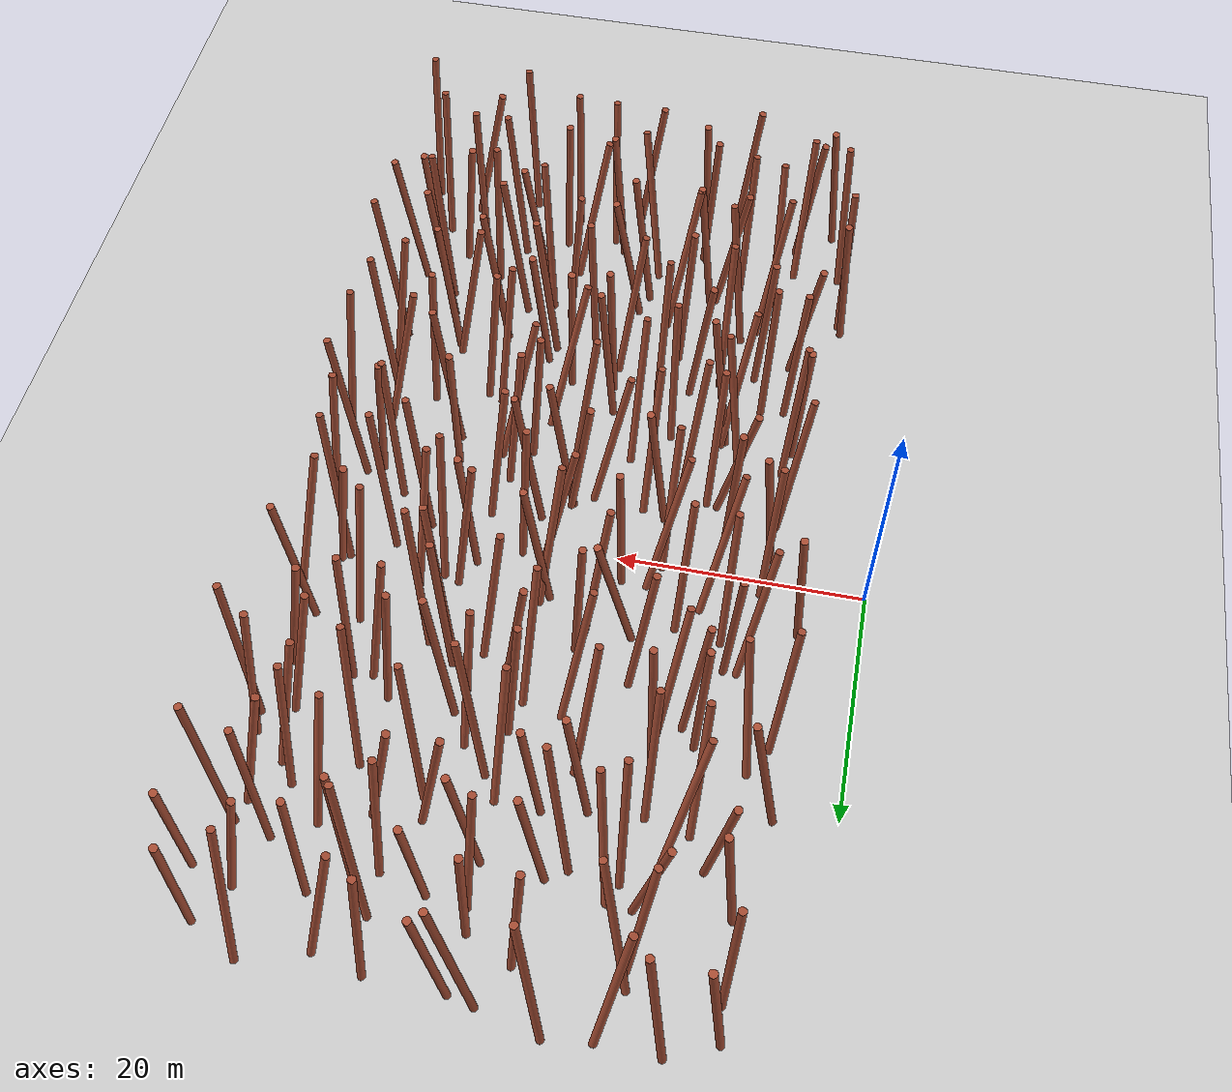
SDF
<?xml version='1.0' encoding='utf-8'?>
<sdf version="1.5">
  <world name="default">
    <!-- A global light source -->
    <include>
      <uri>model://sun</uri>
    </include>
    <!-- A ground plane -->
    <include>
      <uri>model://ground_plane</uri>
    </include>
    <include>
      <uri>model://asphalt_plane</uri>
      <pose>0 0 -0.000001 0 0 0</pose>
    </include>
    <model name="unit_cylinder_0">
      <pose>7.46567 -38.61308 7.70000 -0.17238 0.07720 0.00000</pose>
      <gravity>0 0 0</gravity>
      <link name="link">
        <gravity>1</gravity>
        <inertial>
          <mass>100</mass>
          <inertia>
            <ixx>20</ixx>
            <ixy>0</ixy>
            <ixz>0</ixz>
            <iyy>20</iyy>
            <iyz>0</iyz>
            <izz>20</izz>
          </inertia>
          <pose>0 0 0 0 -0 0</pose>
        </inertial>
        <collision name="collision">
          <geometry>
            <cylinder>
              <radius>0.300</radius>
              <length>15.000</length>
            </cylinder>
          </geometry>
          <max_contacts>10</max_contacts>
          <surface>
            <contact>
              <ode />
            </contact>
            <bounce />
            <friction>
              <torsional>
                <ode />
              </torsional>
              <ode />
            </friction>
          </surface>
        </collision>
        <visual name="visual">
          <geometry>
            <cylinder>
              <radius>0.300</radius>
              <length>15.000</length>
            </cylinder>
          </geometry>
          <material>
            <script>
              <name>Gazebo/Bricks</name>
              <uri>file://media/materials/scripts/gazebo.material</uri>
            </script>
          </material>
        </visual>
        <self_collide>0</self_collide>
        <enable_wind>0</enable_wind>
        <kinematic>0</kinematic>
      </link>
      <static>1</static>
    </model>
    <model name="unit_cylinder_1">
      <pose>6.21727 -35.06247 7.70000 0.06165 0.05477 0.00000</pose>
      <gravity>0 0 0</gravity>
      <link name="link">
        <gravity>1</gravity>
        <inertial>
          <mass>100</mass>
          <inertia>
            <ixx>20</ixx>
            <ixy>0</ixy>
            <ixz>0</ixz>
            <iyy>20</iyy>
            <iyz>0</iyz>
            <izz>20</izz>
          </inertia>
          <pose>0 0 0 0 -0 0</pose>
        </inertial>
        <collision name="collision">
          <geometry>
            <cylinder>
              <radius>0.300</radius>
              <length>15.000</length>
            </cylinder>
          </geometry>
          <max_contacts>10</max_contacts>
          <surface>
            <contact>
              <ode />
            </contact>
            <bounce />
            <friction>
              <torsional>
                <ode />
              </torsional>
              <ode />
            </friction>
          </surface>
        </collision>
        <visual name="visual">
          <geometry>
            <cylinder>
              <radius>0.300</radius>
              <length>15.000</length>
            </cylinder>
          </geometry>
          <material>
            <script>
              <name>Gazebo/Bricks</name>
              <uri>file://media/materials/scripts/gazebo.material</uri>
            </script>
          </material>
        </visual>
        <self_collide>0</self_collide>
        <enable_wind>0</enable_wind>
        <kinematic>1</kinematic>
      </link>
      <static>0</static>
      <plugin name="dynamic_obstacle_motion_1" filename="libobstaclePathPlugin.so">
        <motion_type>proximity_linear</motion_type>
        <direction>-0.527582038 0.849504086 0.000000000</direction>
        <velocity>0.512762627</velocity>
        <activation_distance>20.000000000</activation_distance>
        <activation_model>iris</activation_model>
        <orientation>false</orientation>
        <marker_enabled>true</marker_enabled>
        <marker_id>1</marker_id>
        <marker_radius>0.300000000</marker_radius>
        <marker_height>15.000000000</marker_height>
        <marker_rate>20.0</marker_rate>
        <marker_topic>/uav_simulator/dynamic_obstacles</marker_topic>
        <marker_frame>map</marker_frame>
      </plugin>
    </model>
    <model name="unit_cylinder_2">
      <pose>5.43931 -29.41341 7.70000 0.06542 0.03011 0.00000</pose>
      <gravity>0 0 0</gravity>
      <link name="link">
        <gravity>1</gravity>
        <inertial>
          <mass>100</mass>
          <inertia>
            <ixx>20</ixx>
            <ixy>0</ixy>
            <ixz>0</ixz>
            <iyy>20</iyy>
            <iyz>0</iyz>
            <izz>20</izz>
          </inertia>
          <pose>0 0 0 0 -0 0</pose>
        </inertial>
        <collision name="collision">
          <geometry>
            <cylinder>
              <radius>0.300</radius>
              <length>15.000</length>
            </cylinder>
          </geometry>
          <max_contacts>10</max_contacts>
          <surface>
            <contact>
              <ode />
            </contact>
            <bounce />
            <friction>
              <torsional>
                <ode />
              </torsional>
              <ode />
            </friction>
          </surface>
        </collision>
        <visual name="visual">
          <geometry>
            <cylinder>
              <radius>0.300</radius>
              <length>15.000</length>
            </cylinder>
          </geometry>
          <material>
            <script>
              <name>Gazebo/Bricks</name>
              <uri>file://media/materials/scripts/gazebo.material</uri>
            </script>
          </material>
        </visual>
        <self_collide>0</self_collide>
        <enable_wind>0</enable_wind>
        <kinematic>0</kinematic>
      </link>
      <static>1</static>
    </model>
    <model name="unit_cylinder_3">
      <pose>5.35619 -27.03663 7.70000 -0.13429 0.05906 0.00000</pose>
      <gravity>0 0 0</gravity>
      <link name="link">
        <gravity>1</gravity>
        <inertial>
          <mass>100</mass>
          <inertia>
            <ixx>20</ixx>
            <ixy>0</ixy>
            <ixz>0</ixz>
            <iyy>20</iyy>
            <iyz>0</iyz>
            <izz>20</izz>
          </inertia>
          <pose>0 0 0 0 -0 0</pose>
        </inertial>
        <collision name="collision">
          <geometry>
            <cylinder>
              <radius>0.300</radius>
              <length>15.000</length>
            </cylinder>
          </geometry>
          <max_contacts>10</max_contacts>
          <surface>
            <contact>
              <ode />
            </contact>
            <bounce />
            <friction>
              <torsional>
                <ode />
              </torsional>
              <ode />
            </friction>
          </surface>
        </collision>
        <visual name="visual">
          <geometry>
            <cylinder>
              <radius>0.300</radius>
              <length>15.000</length>
            </cylinder>
          </geometry>
          <material>
            <script>
              <name>Gazebo/Bricks</name>
              <uri>file://media/materials/scripts/gazebo.material</uri>
            </script>
          </material>
        </visual>
        <self_collide>0</self_collide>
        <enable_wind>0</enable_wind>
        <kinematic>0</kinematic>
      </link>
      <static>1</static>
    </model>
    <model name="unit_cylinder_4">
      <pose>8.06512 -21.73586 7.70000 -0.17223 -0.11071 0.00000</pose>
      <gravity>0 0 0</gravity>
      <link name="link">
        <gravity>1</gravity>
        <inertial>
          <mass>100</mass>
          <inertia>
            <ixx>20</ixx>
            <ixy>0</ixy>
            <ixz>0</ixz>
            <iyy>20</iyy>
            <iyz>0</iyz>
            <izz>20</izz>
          </inertia>
          <pose>0 0 0 0 -0 0</pose>
        </inertial>
        <collision name="collision">
          <geometry>
            <cylinder>
              <radius>0.300</radius>
              <length>15.000</length>
            </cylinder>
          </geometry>
          <max_contacts>10</max_contacts>
          <surface>
            <contact>
              <ode />
            </contact>
            <bounce />
            <friction>
              <torsional>
                <ode />
              </torsional>
              <ode />
            </friction>
          </surface>
        </collision>
        <visual name="visual">
          <geometry>
            <cylinder>
              <radius>0.300</radius>
              <length>15.000</length>
            </cylinder>
          </geometry>
          <material>
            <script>
              <name>Gazebo/Bricks</name>
              <uri>file://media/materials/scripts/gazebo.material</uri>
            </script>
          </material>
        </visual>
        <self_collide>0</self_collide>
        <enable_wind>0</enable_wind>
        <kinematic>1</kinematic>
      </link>
      <static>0</static>
      <plugin name="dynamic_obstacle_motion_4" filename="libobstaclePathPlugin.so">
        <motion_type>proximity_linear</motion_type>
        <direction>-0.752486816 -0.658607312 0.000000000</direction>
        <velocity>0.386107136</velocity>
        <activation_distance>20.000000000</activation_distance>
        <activation_model>iris</activation_model>
        <orientation>false</orientation>
        <marker_enabled>true</marker_enabled>
        <marker_id>4</marker_id>
        <marker_radius>0.300000000</marker_radius>
        <marker_height>15.000000000</marker_height>
        <marker_rate>20.0</marker_rate>
        <marker_topic>/uav_simulator/dynamic_obstacles</marker_topic>
        <marker_frame>map</marker_frame>
      </plugin>
    </model>
    <model name="unit_cylinder_5">
      <pose>8.40337 -17.65239 7.70000 -0.02762 -0.04246 0.00000</pose>
      <gravity>0 0 0</gravity>
      <link name="link">
        <gravity>1</gravity>
        <inertial>
          <mass>100</mass>
          <inertia>
            <ixx>20</ixx>
            <ixy>0</ixy>
            <ixz>0</ixz>
            <iyy>20</iyy>
            <iyz>0</iyz>
            <izz>20</izz>
          </inertia>
          <pose>0 0 0 0 -0 0</pose>
        </inertial>
        <collision name="collision">
          <geometry>
            <cylinder>
              <radius>0.300</radius>
              <length>15.000</length>
            </cylinder>
          </geometry>
          <max_contacts>10</max_contacts>
          <surface>
            <contact>
              <ode />
            </contact>
            <bounce />
            <friction>
              <torsional>
                <ode />
              </torsional>
              <ode />
            </friction>
          </surface>
        </collision>
        <visual name="visual">
          <geometry>
            <cylinder>
              <radius>0.300</radius>
              <length>15.000</length>
            </cylinder>
          </geometry>
          <material>
            <script>
              <name>Gazebo/Bricks</name>
              <uri>file://media/materials/scripts/gazebo.material</uri>
            </script>
          </material>
        </visual>
        <self_collide>0</self_collide>
        <enable_wind>0</enable_wind>
        <kinematic>1</kinematic>
      </link>
      <static>0</static>
      <plugin name="dynamic_obstacle_motion_5" filename="libobstaclePathPlugin.so">
        <motion_type>proximity_linear</motion_type>
        <direction>-0.904084248 -0.427354271 -0.000000000</direction>
        <velocity>0.561092228</velocity>
        <activation_distance>20.000000000</activation_distance>
        <activation_model>iris</activation_model>
        <orientation>false</orientation>
        <marker_enabled>true</marker_enabled>
        <marker_id>5</marker_id>
        <marker_radius>0.300000000</marker_radius>
        <marker_height>15.000000000</marker_height>
        <marker_rate>20.0</marker_rate>
        <marker_topic>/uav_simulator/dynamic_obstacles</marker_topic>
        <marker_frame>map</marker_frame>
      </plugin>
    </model>
    <model name="unit_cylinder_6">
      <pose>7.36256 -12.42776 7.70000 -0.13301 -0.02550 0.00000</pose>
      <gravity>0 0 0</gravity>
      <link name="link">
        <gravity>1</gravity>
        <inertial>
          <mass>100</mass>
          <inertia>
            <ixx>20</ixx>
            <ixy>0</ixy>
            <ixz>0</ixz>
            <iyy>20</iyy>
            <iyz>0</iyz>
            <izz>20</izz>
          </inertia>
          <pose>0 0 0 0 -0 0</pose>
        </inertial>
        <collision name="collision">
          <geometry>
            <cylinder>
              <radius>0.300</radius>
              <length>15.000</length>
            </cylinder>
          </geometry>
          <max_contacts>10</max_contacts>
          <surface>
            <contact>
              <ode />
            </contact>
            <bounce />
            <friction>
              <torsional>
                <ode />
              </torsional>
              <ode />
            </friction>
          </surface>
        </collision>
        <visual name="visual">
          <geometry>
            <cylinder>
              <radius>0.300</radius>
              <length>15.000</length>
            </cylinder>
          </geometry>
          <material>
            <script>
              <name>Gazebo/Bricks</name>
              <uri>file://media/materials/scripts/gazebo.material</uri>
            </script>
          </material>
        </visual>
        <self_collide>0</self_collide>
        <enable_wind>0</enable_wind>
        <kinematic>1</kinematic>
      </link>
      <static>0</static>
      <plugin name="dynamic_obstacle_motion_6" filename="libobstaclePathPlugin.so">
        <motion_type>proximity_linear</motion_type>
        <direction>0.969228966 -0.246160946 0.000000000</direction>
        <velocity>1.718504181</velocity>
        <activation_distance>20.000000000</activation_distance>
        <activation_model>iris</activation_model>
        <orientation>false</orientation>
        <marker_enabled>true</marker_enabled>
        <marker_id>6</marker_id>
        <marker_radius>0.300000000</marker_radius>
        <marker_height>15.000000000</marker_height>
        <marker_rate>20.0</marker_rate>
        <marker_topic>/uav_simulator/dynamic_obstacles</marker_topic>
        <marker_frame>map</marker_frame>
      </plugin>
    </model>
    <model name="unit_cylinder_7">
      <pose>7.78029 -11.45430 7.70000 0.04315 -0.04277 0.00000</pose>
      <gravity>0 0 0</gravity>
      <link name="link">
        <gravity>1</gravity>
        <inertial>
          <mass>100</mass>
          <inertia>
            <ixx>20</ixx>
            <ixy>0</ixy>
            <ixz>0</ixz>
            <iyy>20</iyy>
            <iyz>0</iyz>
            <izz>20</izz>
          </inertia>
          <pose>0 0 0 0 -0 0</pose>
        </inertial>
        <collision name="collision">
          <geometry>
            <cylinder>
              <radius>0.300</radius>
              <length>15.000</length>
            </cylinder>
          </geometry>
          <max_contacts>10</max_contacts>
          <surface>
            <contact>
              <ode />
            </contact>
            <bounce />
            <friction>
              <torsional>
                <ode />
              </torsional>
              <ode />
            </friction>
          </surface>
        </collision>
        <visual name="visual">
          <geometry>
            <cylinder>
              <radius>0.300</radius>
              <length>15.000</length>
            </cylinder>
          </geometry>
          <material>
            <script>
              <name>Gazebo/Bricks</name>
              <uri>file://media/materials/scripts/gazebo.material</uri>
            </script>
          </material>
        </visual>
        <self_collide>0</self_collide>
        <enable_wind>0</enable_wind>
        <kinematic>1</kinematic>
      </link>
      <static>0</static>
      <plugin name="dynamic_obstacle_motion_7" filename="libobstaclePathPlugin.so">
        <motion_type>proximity_linear</motion_type>
        <direction>0.122197259 -0.992505834 0.000000000</direction>
        <velocity>0.489649809</velocity>
        <activation_distance>20.000000000</activation_distance>
        <activation_model>iris</activation_model>
        <orientation>false</orientation>
        <marker_enabled>true</marker_enabled>
        <marker_id>7</marker_id>
        <marker_radius>0.300000000</marker_radius>
        <marker_height>15.000000000</marker_height>
        <marker_rate>20.0</marker_rate>
        <marker_topic>/uav_simulator/dynamic_obstacles</marker_topic>
        <marker_frame>map</marker_frame>
      </plugin>
    </model>
    <model name="unit_cylinder_8">
      <pose>7.14832 -6.00009 7.70000 0.07278 -0.09393 0.00000</pose>
      <gravity>0 0 0</gravity>
      <link name="link">
        <gravity>1</gravity>
        <inertial>
          <mass>100</mass>
          <inertia>
            <ixx>20</ixx>
            <ixy>0</ixy>
            <ixz>0</ixz>
            <iyy>20</iyy>
            <iyz>0</iyz>
            <izz>20</izz>
          </inertia>
          <pose>0 0 0 0 -0 0</pose>
        </inertial>
        <collision name="collision">
          <geometry>
            <cylinder>
              <radius>0.300</radius>
              <length>15.000</length>
            </cylinder>
          </geometry>
          <max_contacts>10</max_contacts>
          <surface>
            <contact>
              <ode />
            </contact>
            <bounce />
            <friction>
              <torsional>
                <ode />
              </torsional>
              <ode />
            </friction>
          </surface>
        </collision>
        <visual name="visual">
          <geometry>
            <cylinder>
              <radius>0.300</radius>
              <length>15.000</length>
            </cylinder>
          </geometry>
          <material>
            <script>
              <name>Gazebo/Bricks</name>
              <uri>file://media/materials/scripts/gazebo.material</uri>
            </script>
          </material>
        </visual>
        <self_collide>0</self_collide>
        <enable_wind>0</enable_wind>
        <kinematic>0</kinematic>
      </link>
      <static>1</static>
    </model>
    <model name="unit_cylinder_9">
      <pose>8.47925 -1.17007 7.70000 -0.12433 0.08688 0.00000</pose>
      <gravity>0 0 0</gravity>
      <link name="link">
        <gravity>1</gravity>
        <inertial>
          <mass>100</mass>
          <inertia>
            <ixx>20</ixx>
            <ixy>0</ixy>
            <ixz>0</ixz>
            <iyy>20</iyy>
            <iyz>0</iyz>
            <izz>20</izz>
          </inertia>
          <pose>0 0 0 0 -0 0</pose>
        </inertial>
        <collision name="collision">
          <geometry>
            <cylinder>
              <radius>0.300</radius>
              <length>15.000</length>
            </cylinder>
          </geometry>
          <max_contacts>10</max_contacts>
          <surface>
            <contact>
              <ode />
            </contact>
            <bounce />
            <friction>
              <torsional>
                <ode />
              </torsional>
              <ode />
            </friction>
          </surface>
        </collision>
        <visual name="visual">
          <geometry>
            <cylinder>
              <radius>0.300</radius>
              <length>15.000</length>
            </cylinder>
          </geometry>
          <material>
            <script>
              <name>Gazebo/Bricks</name>
              <uri>file://media/materials/scripts/gazebo.material</uri>
            </script>
          </material>
        </visual>
        <self_collide>0</self_collide>
        <enable_wind>0</enable_wind>
        <kinematic>0</kinematic>
      </link>
      <static>1</static>
    </model>
    <model name="unit_cylinder_10">
      <pose>8.07390 0.90257 7.70000 0.05890 -0.02465 0.00000</pose>
      <gravity>0 0 0</gravity>
      <link name="link">
        <gravity>1</gravity>
        <inertial>
          <mass>100</mass>
          <inertia>
            <ixx>20</ixx>
            <ixy>0</ixy>
            <ixz>0</ixz>
            <iyy>20</iyy>
            <iyz>0</iyz>
            <izz>20</izz>
          </inertia>
          <pose>0 0 0 0 -0 0</pose>
        </inertial>
        <collision name="collision">
          <geometry>
            <cylinder>
              <radius>0.300</radius>
              <length>15.000</length>
            </cylinder>
          </geometry>
          <max_contacts>10</max_contacts>
          <surface>
            <contact>
              <ode />
            </contact>
            <bounce />
            <friction>
              <torsional>
                <ode />
              </torsional>
              <ode />
            </friction>
          </surface>
        </collision>
        <visual name="visual">
          <geometry>
            <cylinder>
              <radius>0.300</radius>
              <length>15.000</length>
            </cylinder>
          </geometry>
          <material>
            <script>
              <name>Gazebo/Bricks</name>
              <uri>file://media/materials/scripts/gazebo.material</uri>
            </script>
          </material>
        </visual>
        <self_collide>0</self_collide>
        <enable_wind>0</enable_wind>
        <kinematic>0</kinematic>
      </link>
      <static>1</static>
    </model>
    <model name="unit_cylinder_11">
      <pose>5.30931 5.61943 7.70000 -0.12679 0.05714 0.00000</pose>
      <gravity>0 0 0</gravity>
      <link name="link">
        <gravity>1</gravity>
        <inertial>
          <mass>100</mass>
          <inertia>
            <ixx>20</ixx>
            <ixy>0</ixy>
            <ixz>0</ixz>
            <iyy>20</iyy>
            <iyz>0</iyz>
            <izz>20</izz>
          </inertia>
          <pose>0 0 0 0 -0 0</pose>
        </inertial>
        <collision name="collision">
          <geometry>
            <cylinder>
              <radius>0.300</radius>
              <length>15.000</length>
            </cylinder>
          </geometry>
          <max_contacts>10</max_contacts>
          <surface>
            <contact>
              <ode />
            </contact>
            <bounce />
            <friction>
              <torsional>
                <ode />
              </torsional>
              <ode />
            </friction>
          </surface>
        </collision>
        <visual name="visual">
          <geometry>
            <cylinder>
              <radius>0.300</radius>
              <length>15.000</length>
            </cylinder>
          </geometry>
          <material>
            <script>
              <name>Gazebo/Bricks</name>
              <uri>file://media/materials/scripts/gazebo.material</uri>
            </script>
          </material>
        </visual>
        <self_collide>0</self_collide>
        <enable_wind>0</enable_wind>
        <kinematic>0</kinematic>
      </link>
      <static>1</static>
    </model>
    <model name="unit_cylinder_12">
      <pose>8.21517 8.51384 7.70000 0.08725 -0.11731 0.00000</pose>
      <gravity>0 0 0</gravity>
      <link name="link">
        <gravity>1</gravity>
        <inertial>
          <mass>100</mass>
          <inertia>
            <ixx>20</ixx>
            <ixy>0</ixy>
            <ixz>0</ixz>
            <iyy>20</iyy>
            <iyz>0</iyz>
            <izz>20</izz>
          </inertia>
          <pose>0 0 0 0 -0 0</pose>
        </inertial>
        <collision name="collision">
          <geometry>
            <cylinder>
              <radius>0.300</radius>
              <length>15.000</length>
            </cylinder>
          </geometry>
          <max_contacts>10</max_contacts>
          <surface>
            <contact>
              <ode />
            </contact>
            <bounce />
            <friction>
              <torsional>
                <ode />
              </torsional>
              <ode />
            </friction>
          </surface>
        </collision>
        <visual name="visual">
          <geometry>
            <cylinder>
              <radius>0.300</radius>
              <length>15.000</length>
            </cylinder>
          </geometry>
          <material>
            <script>
              <name>Gazebo/Bricks</name>
              <uri>file://media/materials/scripts/gazebo.material</uri>
            </script>
          </material>
        </visual>
        <self_collide>0</self_collide>
        <enable_wind>0</enable_wind>
        <kinematic>1</kinematic>
      </link>
      <static>0</static>
      <plugin name="dynamic_obstacle_motion_12" filename="libobstaclePathPlugin.so">
        <motion_type>proximity_linear</motion_type>
        <direction>0.995938538 0.090035711 0.000000000</direction>
        <velocity>0.513485802</velocity>
        <activation_distance>20.000000000</activation_distance>
        <activation_model>iris</activation_model>
        <orientation>false</orientation>
        <marker_enabled>true</marker_enabled>
        <marker_id>12</marker_id>
        <marker_radius>0.300000000</marker_radius>
        <marker_height>15.000000000</marker_height>
        <marker_rate>20.0</marker_rate>
        <marker_topic>/uav_simulator/dynamic_obstacles</marker_topic>
        <marker_frame>map</marker_frame>
      </plugin>
    </model>
    <model name="unit_cylinder_13">
      <pose>5.41419 14.76799 7.70000 0.06608 -0.05039 0.00000</pose>
      <gravity>0 0 0</gravity>
      <link name="link">
        <gravity>1</gravity>
        <inertial>
          <mass>100</mass>
          <inertia>
            <ixx>20</ixx>
            <ixy>0</ixy>
            <ixz>0</ixz>
            <iyy>20</iyy>
            <iyz>0</iyz>
            <izz>20</izz>
          </inertia>
          <pose>0 0 0 0 -0 0</pose>
        </inertial>
        <collision name="collision">
          <geometry>
            <cylinder>
              <radius>0.300</radius>
              <length>15.000</length>
            </cylinder>
          </geometry>
          <max_contacts>10</max_contacts>
          <surface>
            <contact>
              <ode />
            </contact>
            <bounce />
            <friction>
              <torsional>
                <ode />
              </torsional>
              <ode />
            </friction>
          </surface>
        </collision>
        <visual name="visual">
          <geometry>
            <cylinder>
              <radius>0.300</radius>
              <length>15.000</length>
            </cylinder>
          </geometry>
          <material>
            <script>
              <name>Gazebo/Bricks</name>
              <uri>file://media/materials/scripts/gazebo.material</uri>
            </script>
          </material>
        </visual>
        <self_collide>0</self_collide>
        <enable_wind>0</enable_wind>
        <kinematic>0</kinematic>
      </link>
      <static>1</static>
    </model>
    <model name="unit_cylinder_14">
      <pose>7.78083 16.59841 7.70000 0.14490 0.08780 0.00000</pose>
      <gravity>0 0 0</gravity>
      <link name="link">
        <gravity>1</gravity>
        <inertial>
          <mass>100</mass>
          <inertia>
            <ixx>20</ixx>
            <ixy>0</ixy>
            <ixz>0</ixz>
            <iyy>20</iyy>
            <iyz>0</iyz>
            <izz>20</izz>
          </inertia>
          <pose>0 0 0 0 -0 0</pose>
        </inertial>
        <collision name="collision">
          <geometry>
            <cylinder>
              <radius>0.300</radius>
              <length>15.000</length>
            </cylinder>
          </geometry>
          <max_contacts>10</max_contacts>
          <surface>
            <contact>
              <ode />
            </contact>
            <bounce />
            <friction>
              <torsional>
                <ode />
              </torsional>
              <ode />
            </friction>
          </surface>
        </collision>
        <visual name="visual">
          <geometry>
            <cylinder>
              <radius>0.300</radius>
              <length>15.000</length>
            </cylinder>
          </geometry>
          <material>
            <script>
              <name>Gazebo/Bricks</name>
              <uri>file://media/materials/scripts/gazebo.material</uri>
            </script>
          </material>
        </visual>
        <self_collide>0</self_collide>
        <enable_wind>0</enable_wind>
        <kinematic>1</kinematic>
      </link>
      <static>0</static>
      <plugin name="dynamic_obstacle_motion_14" filename="libobstaclePathPlugin.so">
        <motion_type>proximity_linear</motion_type>
        <direction>0.441147380 -0.897434671 0.000000000</direction>
        <velocity>0.627199507</velocity>
        <activation_distance>20.000000000</activation_distance>
        <activation_model>iris</activation_model>
        <orientation>false</orientation>
        <marker_enabled>true</marker_enabled>
        <marker_id>14</marker_id>
        <marker_radius>0.300000000</marker_radius>
        <marker_height>15.000000000</marker_height>
        <marker_rate>20.0</marker_rate>
        <marker_topic>/uav_simulator/dynamic_obstacles</marker_topic>
        <marker_frame>map</marker_frame>
      </plugin>
    </model>
    <model name="unit_cylinder_15">
      <pose>5.89723 21.64331 7.70000 -0.07898 0.15290 0.00000</pose>
      <gravity>0 0 0</gravity>
      <link name="link">
        <gravity>1</gravity>
        <inertial>
          <mass>100</mass>
          <inertia>
            <ixx>20</ixx>
            <ixy>0</ixy>
            <ixz>0</ixz>
            <iyy>20</iyy>
            <iyz>0</iyz>
            <izz>20</izz>
          </inertia>
          <pose>0 0 0 0 -0 0</pose>
        </inertial>
        <collision name="collision">
          <geometry>
            <cylinder>
              <radius>0.300</radius>
              <length>15.000</length>
            </cylinder>
          </geometry>
          <max_contacts>10</max_contacts>
          <surface>
            <contact>
              <ode />
            </contact>
            <bounce />
            <friction>
              <torsional>
                <ode />
              </torsional>
              <ode />
            </friction>
          </surface>
        </collision>
        <visual name="visual">
          <geometry>
            <cylinder>
              <radius>0.300</radius>
              <length>15.000</length>
            </cylinder>
          </geometry>
          <material>
            <script>
              <name>Gazebo/Bricks</name>
              <uri>file://media/materials/scripts/gazebo.material</uri>
            </script>
          </material>
        </visual>
        <self_collide>0</self_collide>
        <enable_wind>0</enable_wind>
        <kinematic>0</kinematic>
      </link>
      <static>1</static>
    </model>
    <model name="unit_cylinder_16">
      <pose>8.23481 27.26998 7.70000 -0.16573 -0.11002 0.00000</pose>
      <gravity>0 0 0</gravity>
      <link name="link">
        <gravity>1</gravity>
        <inertial>
          <mass>100</mass>
          <inertia>
            <ixx>20</ixx>
            <ixy>0</ixy>
            <ixz>0</ixz>
            <iyy>20</iyy>
            <iyz>0</iyz>
            <izz>20</izz>
          </inertia>
          <pose>0 0 0 0 -0 0</pose>
        </inertial>
        <collision name="collision">
          <geometry>
            <cylinder>
              <radius>0.300</radius>
              <length>15.000</length>
            </cylinder>
          </geometry>
          <max_contacts>10</max_contacts>
          <surface>
            <contact>
              <ode />
            </contact>
            <bounce />
            <friction>
              <torsional>
                <ode />
              </torsional>
              <ode />
            </friction>
          </surface>
        </collision>
        <visual name="visual">
          <geometry>
            <cylinder>
              <radius>0.300</radius>
              <length>15.000</length>
            </cylinder>
          </geometry>
          <material>
            <script>
              <name>Gazebo/Bricks</name>
              <uri>file://media/materials/scripts/gazebo.material</uri>
            </script>
          </material>
        </visual>
        <self_collide>0</self_collide>
        <enable_wind>0</enable_wind>
        <kinematic>1</kinematic>
      </link>
      <static>0</static>
      <plugin name="dynamic_obstacle_motion_16" filename="libobstaclePathPlugin.so">
        <motion_type>proximity_linear</motion_type>
        <direction>-0.396383134 0.918085187 0.000000000</direction>
        <velocity>0.545856722</velocity>
        <activation_distance>20.000000000</activation_distance>
        <activation_model>iris</activation_model>
        <orientation>false</orientation>
        <marker_enabled>true</marker_enabled>
        <marker_id>16</marker_id>
        <marker_radius>0.300000000</marker_radius>
        <marker_height>15.000000000</marker_height>
        <marker_rate>20.0</marker_rate>
        <marker_topic>/uav_simulator/dynamic_obstacles</marker_topic>
        <marker_frame>map</marker_frame>
      </plugin>
    </model>
    <model name="unit_cylinder_17">
      <pose>7.14097 29.90582 7.70000 -0.09009 0.08101 0.00000</pose>
      <gravity>0 0 0</gravity>
      <link name="link">
        <gravity>1</gravity>
        <inertial>
          <mass>100</mass>
          <inertia>
            <ixx>20</ixx>
            <ixy>0</ixy>
            <ixz>0</ixz>
            <iyy>20</iyy>
            <iyz>0</iyz>
            <izz>20</izz>
          </inertia>
          <pose>0 0 0 0 -0 0</pose>
        </inertial>
        <collision name="collision">
          <geometry>
            <cylinder>
              <radius>0.300</radius>
              <length>15.000</length>
            </cylinder>
          </geometry>
          <max_contacts>10</max_contacts>
          <surface>
            <contact>
              <ode />
            </contact>
            <bounce />
            <friction>
              <torsional>
                <ode />
              </torsional>
              <ode />
            </friction>
          </surface>
        </collision>
        <visual name="visual">
          <geometry>
            <cylinder>
              <radius>0.300</radius>
              <length>15.000</length>
            </cylinder>
          </geometry>
          <material>
            <script>
              <name>Gazebo/Bricks</name>
              <uri>file://media/materials/scripts/gazebo.material</uri>
            </script>
          </material>
        </visual>
        <self_collide>0</self_collide>
        <enable_wind>0</enable_wind>
        <kinematic>1</kinematic>
      </link>
      <static>0</static>
      <plugin name="dynamic_obstacle_motion_17" filename="libobstaclePathPlugin.so">
        <motion_type>proximity_linear</motion_type>
        <direction>-0.793099003 -0.609092744 0.000000000</direction>
        <velocity>0.191172605</velocity>
        <activation_distance>20.000000000</activation_distance>
        <activation_model>iris</activation_model>
        <orientation>false</orientation>
        <marker_enabled>true</marker_enabled>
        <marker_id>17</marker_id>
        <marker_radius>0.300000000</marker_radius>
        <marker_height>15.000000000</marker_height>
        <marker_rate>20.0</marker_rate>
        <marker_topic>/uav_simulator/dynamic_obstacles</marker_topic>
        <marker_frame>map</marker_frame>
      </plugin>
    </model>
    <model name="unit_cylinder_18">
      <pose>6.31902 35.40291 7.70000 0.00913 -0.01244 0.00000</pose>
      <gravity>0 0 0</gravity>
      <link name="link">
        <gravity>1</gravity>
        <inertial>
          <mass>100</mass>
          <inertia>
            <ixx>20</ixx>
            <ixy>0</ixy>
            <ixz>0</ixz>
            <iyy>20</iyy>
            <iyz>0</iyz>
            <izz>20</izz>
          </inertia>
          <pose>0 0 0 0 -0 0</pose>
        </inertial>
        <collision name="collision">
          <geometry>
            <cylinder>
              <radius>0.300</radius>
              <length>15.000</length>
            </cylinder>
          </geometry>
          <max_contacts>10</max_contacts>
          <surface>
            <contact>
              <ode />
            </contact>
            <bounce />
            <friction>
              <torsional>
                <ode />
              </torsional>
              <ode />
            </friction>
          </surface>
        </collision>
        <visual name="visual">
          <geometry>
            <cylinder>
              <radius>0.300</radius>
              <length>15.000</length>
            </cylinder>
          </geometry>
          <material>
            <script>
              <name>Gazebo/Bricks</name>
              <uri>file://media/materials/scripts/gazebo.material</uri>
            </script>
          </material>
        </visual>
        <self_collide>0</self_collide>
        <enable_wind>0</enable_wind>
        <kinematic>0</kinematic>
      </link>
      <static>1</static>
    </model>
    <model name="unit_cylinder_19">
      <pose>6.73714 38.90412 7.70000 -0.09685 0.08952 0.00000</pose>
      <gravity>0 0 0</gravity>
      <link name="link">
        <gravity>1</gravity>
        <inertial>
          <mass>100</mass>
          <inertia>
            <ixx>20</ixx>
            <ixy>0</ixy>
            <ixz>0</ixz>
            <iyy>20</iyy>
            <iyz>0</iyz>
            <izz>20</izz>
          </inertia>
          <pose>0 0 0 0 -0 0</pose>
        </inertial>
        <collision name="collision">
          <geometry>
            <cylinder>
              <radius>0.300</radius>
              <length>15.000</length>
            </cylinder>
          </geometry>
          <max_contacts>10</max_contacts>
          <surface>
            <contact>
              <ode />
            </contact>
            <bounce />
            <friction>
              <torsional>
                <ode />
              </torsional>
              <ode />
            </friction>
          </surface>
        </collision>
        <visual name="visual">
          <geometry>
            <cylinder>
              <radius>0.300</radius>
              <length>15.000</length>
            </cylinder>
          </geometry>
          <material>
            <script>
              <name>Gazebo/Bricks</name>
              <uri>file://media/materials/scripts/gazebo.material</uri>
            </script>
          </material>
        </visual>
        <self_collide>0</self_collide>
        <enable_wind>0</enable_wind>
        <kinematic>0</kinematic>
      </link>
      <static>1</static>
    </model>
    <model name="unit_cylinder_20">
      <pose>9.39629 -36.58790 7.70000 -0.13366 -0.08819 0.00000</pose>
      <gravity>0 0 0</gravity>
      <link name="link">
        <gravity>1</gravity>
        <inertial>
          <mass>100</mass>
          <inertia>
            <ixx>20</ixx>
            <ixy>0</ixy>
            <ixz>0</ixz>
            <iyy>20</iyy>
            <iyz>0</iyz>
            <izz>20</izz>
          </inertia>
          <pose>0 0 0 0 -0 0</pose>
        </inertial>
        <collision name="collision">
          <geometry>
            <cylinder>
              <radius>0.300</radius>
              <length>15.000</length>
            </cylinder>
          </geometry>
          <max_contacts>10</max_contacts>
          <surface>
            <contact>
              <ode />
            </contact>
            <bounce />
            <friction>
              <torsional>
                <ode />
              </torsional>
              <ode />
            </friction>
          </surface>
        </collision>
        <visual name="visual">
          <geometry>
            <cylinder>
              <radius>0.300</radius>
              <length>15.000</length>
            </cylinder>
          </geometry>
          <material>
            <script>
              <name>Gazebo/Bricks</name>
              <uri>file://media/materials/scripts/gazebo.material</uri>
            </script>
          </material>
        </visual>
        <self_collide>0</self_collide>
        <enable_wind>0</enable_wind>
        <kinematic>0</kinematic>
      </link>
      <static>1</static>
    </model>
    <model name="unit_cylinder_21">
      <pose>9.72256 -35.26683 7.70000 0.10694 -0.01709 0.00000</pose>
      <gravity>0 0 0</gravity>
      <link name="link">
        <gravity>1</gravity>
        <inertial>
          <mass>100</mass>
          <inertia>
            <ixx>20</ixx>
            <ixy>0</ixy>
            <ixz>0</ixz>
            <iyy>20</iyy>
            <iyz>0</iyz>
            <izz>20</izz>
          </inertia>
          <pose>0 0 0 0 -0 0</pose>
        </inertial>
        <collision name="collision">
          <geometry>
            <cylinder>
              <radius>0.300</radius>
              <length>15.000</length>
            </cylinder>
          </geometry>
          <max_contacts>10</max_contacts>
          <surface>
            <contact>
              <ode />
            </contact>
            <bounce />
            <friction>
              <torsional>
                <ode />
              </torsional>
              <ode />
            </friction>
          </surface>
        </collision>
        <visual name="visual">
          <geometry>
            <cylinder>
              <radius>0.300</radius>
              <length>15.000</length>
            </cylinder>
          </geometry>
          <material>
            <script>
              <name>Gazebo/Bricks</name>
              <uri>file://media/materials/scripts/gazebo.material</uri>
            </script>
          </material>
        </visual>
        <self_collide>0</self_collide>
        <enable_wind>0</enable_wind>
        <kinematic>0</kinematic>
      </link>
      <static>1</static>
    </model>
    <model name="unit_cylinder_22">
      <pose>11.58012 -31.44989 7.70000 0.13153 0.03549 0.00000</pose>
      <gravity>0 0 0</gravity>
      <link name="link">
        <gravity>1</gravity>
        <inertial>
          <mass>100</mass>
          <inertia>
            <ixx>20</ixx>
            <ixy>0</ixy>
            <ixz>0</ixz>
            <iyy>20</iyy>
            <iyz>0</iyz>
            <izz>20</izz>
          </inertia>
          <pose>0 0 0 0 -0 0</pose>
        </inertial>
        <collision name="collision">
          <geometry>
            <cylinder>
              <radius>0.300</radius>
              <length>15.000</length>
            </cylinder>
          </geometry>
          <max_contacts>10</max_contacts>
          <surface>
            <contact>
              <ode />
            </contact>
            <bounce />
            <friction>
              <torsional>
                <ode />
              </torsional>
              <ode />
            </friction>
          </surface>
        </collision>
        <visual name="visual">
          <geometry>
            <cylinder>
              <radius>0.300</radius>
              <length>15.000</length>
            </cylinder>
          </geometry>
          <material>
            <script>
              <name>Gazebo/Bricks</name>
              <uri>file://media/materials/scripts/gazebo.material</uri>
            </script>
          </material>
        </visual>
        <self_collide>0</self_collide>
        <enable_wind>0</enable_wind>
        <kinematic>1</kinematic>
      </link>
      <static>0</static>
      <plugin name="dynamic_obstacle_motion_22" filename="libobstaclePathPlugin.so">
        <motion_type>proximity_linear</motion_type>
        <direction>0.973647008 -0.228060308 0.000000000</direction>
        <velocity>0.743068776</velocity>
        <activation_distance>20.000000000</activation_distance>
        <activation_model>iris</activation_model>
        <orientation>false</orientation>
        <marker_enabled>true</marker_enabled>
        <marker_id>22</marker_id>
        <marker_radius>0.300000000</marker_radius>
        <marker_height>15.000000000</marker_height>
        <marker_rate>20.0</marker_rate>
        <marker_topic>/uav_simulator/dynamic_obstacles</marker_topic>
        <marker_frame>map</marker_frame>
      </plugin>
    </model>
    <model name="unit_cylinder_23">
      <pose>11.50044 -27.46089 7.70000 0.10107 -0.10912 0.00000</pose>
      <gravity>0 0 0</gravity>
      <link name="link">
        <gravity>1</gravity>
        <inertial>
          <mass>100</mass>
          <inertia>
            <ixx>20</ixx>
            <ixy>0</ixy>
            <ixz>0</ixz>
            <iyy>20</iyy>
            <iyz>0</iyz>
            <izz>20</izz>
          </inertia>
          <pose>0 0 0 0 -0 0</pose>
        </inertial>
        <collision name="collision">
          <geometry>
            <cylinder>
              <radius>0.300</radius>
              <length>15.000</length>
            </cylinder>
          </geometry>
          <max_contacts>10</max_contacts>
          <surface>
            <contact>
              <ode />
            </contact>
            <bounce />
            <friction>
              <torsional>
                <ode />
              </torsional>
              <ode />
            </friction>
          </surface>
        </collision>
        <visual name="visual">
          <geometry>
            <cylinder>
              <radius>0.300</radius>
              <length>15.000</length>
            </cylinder>
          </geometry>
          <material>
            <script>
              <name>Gazebo/Bricks</name>
              <uri>file://media/materials/scripts/gazebo.material</uri>
            </script>
          </material>
        </visual>
        <self_collide>0</self_collide>
        <enable_wind>0</enable_wind>
        <kinematic>0</kinematic>
      </link>
      <static>1</static>
    </model>
    <model name="unit_cylinder_24">
      <pose>11.39231 -20.74590 7.70000 -0.06415 -0.04304 0.00000</pose>
      <gravity>0 0 0</gravity>
      <link name="link">
        <gravity>1</gravity>
        <inertial>
          <mass>100</mass>
          <inertia>
            <ixx>20</ixx>
            <ixy>0</ixy>
            <ixz>0</ixz>
            <iyy>20</iyy>
            <iyz>0</iyz>
            <izz>20</izz>
          </inertia>
          <pose>0 0 0 0 -0 0</pose>
        </inertial>
        <collision name="collision">
          <geometry>
            <cylinder>
              <radius>0.300</radius>
              <length>15.000</length>
            </cylinder>
          </geometry>
          <max_contacts>10</max_contacts>
          <surface>
            <contact>
              <ode />
            </contact>
            <bounce />
            <friction>
              <torsional>
                <ode />
              </torsional>
              <ode />
            </friction>
          </surface>
        </collision>
        <visual name="visual">
          <geometry>
            <cylinder>
              <radius>0.300</radius>
              <length>15.000</length>
            </cylinder>
          </geometry>
          <material>
            <script>
              <name>Gazebo/Bricks</name>
              <uri>file://media/materials/scripts/gazebo.material</uri>
            </script>
          </material>
        </visual>
        <self_collide>0</self_collide>
        <enable_wind>0</enable_wind>
        <kinematic>0</kinematic>
      </link>
      <static>1</static>
    </model>
    <model name="unit_cylinder_25">
      <pose>10.60450 -17.54416 7.70000 -0.00202 -0.00961 0.00000</pose>
      <gravity>0 0 0</gravity>
      <link name="link">
        <gravity>1</gravity>
        <inertial>
          <mass>100</mass>
          <inertia>
            <ixx>20</ixx>
            <ixy>0</ixy>
            <ixz>0</ixz>
            <iyy>20</iyy>
            <iyz>0</iyz>
            <izz>20</izz>
          </inertia>
          <pose>0 0 0 0 -0 0</pose>
        </inertial>
        <collision name="collision">
          <geometry>
            <cylinder>
              <radius>0.300</radius>
              <length>15.000</length>
            </cylinder>
          </geometry>
          <max_contacts>10</max_contacts>
          <surface>
            <contact>
              <ode />
            </contact>
            <bounce />
            <friction>
              <torsional>
                <ode />
              </torsional>
              <ode />
            </friction>
          </surface>
        </collision>
        <visual name="visual">
          <geometry>
            <cylinder>
              <radius>0.300</radius>
              <length>15.000</length>
            </cylinder>
          </geometry>
          <material>
            <script>
              <name>Gazebo/Bricks</name>
              <uri>file://media/materials/scripts/gazebo.material</uri>
            </script>
          </material>
        </visual>
        <self_collide>0</self_collide>
        <enable_wind>0</enable_wind>
        <kinematic>0</kinematic>
      </link>
      <static>1</static>
    </model>
    <model name="unit_cylinder_26">
      <pose>12.69051 -14.01166 7.70000 0.11256 -0.11408 0.00000</pose>
      <gravity>0 0 0</gravity>
      <link name="link">
        <gravity>1</gravity>
        <inertial>
          <mass>100</mass>
          <inertia>
            <ixx>20</ixx>
            <ixy>0</ixy>
            <ixz>0</ixz>
            <iyy>20</iyy>
            <iyz>0</iyz>
            <izz>20</izz>
          </inertia>
          <pose>0 0 0 0 -0 0</pose>
        </inertial>
        <collision name="collision">
          <geometry>
            <cylinder>
              <radius>0.300</radius>
              <length>15.000</length>
            </cylinder>
          </geometry>
          <max_contacts>10</max_contacts>
          <surface>
            <contact>
              <ode />
            </contact>
            <bounce />
            <friction>
              <torsional>
                <ode />
              </torsional>
              <ode />
            </friction>
          </surface>
        </collision>
        <visual name="visual">
          <geometry>
            <cylinder>
              <radius>0.300</radius>
              <length>15.000</length>
            </cylinder>
          </geometry>
          <material>
            <script>
              <name>Gazebo/Bricks</name>
              <uri>file://media/materials/scripts/gazebo.material</uri>
            </script>
          </material>
        </visual>
        <self_collide>0</self_collide>
        <enable_wind>0</enable_wind>
        <kinematic>0</kinematic>
      </link>
      <static>1</static>
    </model>
    <model name="unit_cylinder_27">
      <pose>12.63484 -11.14395 7.70000 0.12269 0.13580 0.00000</pose>
      <gravity>0 0 0</gravity>
      <link name="link">
        <gravity>1</gravity>
        <inertial>
          <mass>100</mass>
          <inertia>
            <ixx>20</ixx>
            <ixy>0</ixy>
            <ixz>0</ixz>
            <iyy>20</iyy>
            <iyz>0</iyz>
            <izz>20</izz>
          </inertia>
          <pose>0 0 0 0 -0 0</pose>
        </inertial>
        <collision name="collision">
          <geometry>
            <cylinder>
              <radius>0.300</radius>
              <length>15.000</length>
            </cylinder>
          </geometry>
          <max_contacts>10</max_contacts>
          <surface>
            <contact>
              <ode />
            </contact>
            <bounce />
            <friction>
              <torsional>
                <ode />
              </torsional>
              <ode />
            </friction>
          </surface>
        </collision>
        <visual name="visual">
          <geometry>
            <cylinder>
              <radius>0.300</radius>
              <length>15.000</length>
            </cylinder>
          </geometry>
          <material>
            <script>
              <name>Gazebo/Bricks</name>
              <uri>file://media/materials/scripts/gazebo.material</uri>
            </script>
          </material>
        </visual>
        <self_collide>0</self_collide>
        <enable_wind>0</enable_wind>
        <kinematic>1</kinematic>
      </link>
      <static>0</static>
      <plugin name="dynamic_obstacle_motion_27" filename="libobstaclePathPlugin.so">
        <motion_type>proximity_linear</motion_type>
        <direction>0.649691815 -0.760197701 0.000000000</direction>
        <velocity>0.879295809</velocity>
        <activation_distance>20.000000000</activation_distance>
        <activation_model>iris</activation_model>
        <orientation>false</orientation>
        <marker_enabled>true</marker_enabled>
        <marker_id>27</marker_id>
        <marker_radius>0.300000000</marker_radius>
        <marker_height>15.000000000</marker_height>
        <marker_rate>20.0</marker_rate>
        <marker_topic>/uav_simulator/dynamic_obstacles</marker_topic>
        <marker_frame>map</marker_frame>
      </plugin>
    </model>
    <model name="unit_cylinder_28">
      <pose>11.63084 -5.40931 7.70000 -0.14817 -0.17126 0.00000</pose>
      <gravity>0 0 0</gravity>
      <link name="link">
        <gravity>1</gravity>
        <inertial>
          <mass>100</mass>
          <inertia>
            <ixx>20</ixx>
            <ixy>0</ixy>
            <ixz>0</ixz>
            <iyy>20</iyy>
            <iyz>0</iyz>
            <izz>20</izz>
          </inertia>
          <pose>0 0 0 0 -0 0</pose>
        </inertial>
        <collision name="collision">
          <geometry>
            <cylinder>
              <radius>0.300</radius>
              <length>15.000</length>
            </cylinder>
          </geometry>
          <max_contacts>10</max_contacts>
          <surface>
            <contact>
              <ode />
            </contact>
            <bounce />
            <friction>
              <torsional>
                <ode />
              </torsional>
              <ode />
            </friction>
          </surface>
        </collision>
        <visual name="visual">
          <geometry>
            <cylinder>
              <radius>0.300</radius>
              <length>15.000</length>
            </cylinder>
          </geometry>
          <material>
            <script>
              <name>Gazebo/Bricks</name>
              <uri>file://media/materials/scripts/gazebo.material</uri>
            </script>
          </material>
        </visual>
        <self_collide>0</self_collide>
        <enable_wind>0</enable_wind>
        <kinematic>1</kinematic>
      </link>
      <static>0</static>
      <plugin name="dynamic_obstacle_motion_28" filename="libobstaclePathPlugin.so">
        <motion_type>proximity_linear</motion_type>
        <direction>0.120241730 -0.992744643 0.000000000</direction>
        <velocity>0.336076982</velocity>
        <activation_distance>20.000000000</activation_distance>
        <activation_model>iris</activation_model>
        <orientation>false</orientation>
        <marker_enabled>true</marker_enabled>
        <marker_id>28</marker_id>
        <marker_radius>0.300000000</marker_radius>
        <marker_height>15.000000000</marker_height>
        <marker_rate>20.0</marker_rate>
        <marker_topic>/uav_simulator/dynamic_obstacles</marker_topic>
        <marker_frame>map</marker_frame>
      </plugin>
    </model>
    <model name="unit_cylinder_29">
      <pose>11.51156 -2.61874 7.70000 -0.07234 -0.03465 0.00000</pose>
      <gravity>0 0 0</gravity>
      <link name="link">
        <gravity>1</gravity>
        <inertial>
          <mass>100</mass>
          <inertia>
            <ixx>20</ixx>
            <ixy>0</ixy>
            <ixz>0</ixz>
            <iyy>20</iyy>
            <iyz>0</iyz>
            <izz>20</izz>
          </inertia>
          <pose>0 0 0 0 -0 0</pose>
        </inertial>
        <collision name="collision">
          <geometry>
            <cylinder>
              <radius>0.300</radius>
              <length>15.000</length>
            </cylinder>
          </geometry>
          <max_contacts>10</max_contacts>
          <surface>
            <contact>
              <ode />
            </contact>
            <bounce />
            <friction>
              <torsional>
                <ode />
              </torsional>
              <ode />
            </friction>
          </surface>
        </collision>
        <visual name="visual">
          <geometry>
            <cylinder>
              <radius>0.300</radius>
              <length>15.000</length>
            </cylinder>
          </geometry>
          <material>
            <script>
              <name>Gazebo/Bricks</name>
              <uri>file://media/materials/scripts/gazebo.material</uri>
            </script>
          </material>
        </visual>
        <self_collide>0</self_collide>
        <enable_wind>0</enable_wind>
        <kinematic>1</kinematic>
      </link>
      <static>0</static>
      <plugin name="dynamic_obstacle_motion_29" filename="libobstaclePathPlugin.so">
        <motion_type>proximity_linear</motion_type>
        <direction>0.851806445 0.523856641 0.000000000</direction>
        <velocity>1.157463116</velocity>
        <activation_distance>20.000000000</activation_distance>
        <activation_model>iris</activation_model>
        <orientation>false</orientation>
        <marker_enabled>true</marker_enabled>
        <marker_id>29</marker_id>
        <marker_radius>0.300000000</marker_radius>
        <marker_height>15.000000000</marker_height>
        <marker_rate>20.0</marker_rate>
        <marker_topic>/uav_simulator/dynamic_obstacles</marker_topic>
        <marker_frame>map</marker_frame>
      </plugin>
    </model>
    <model name="unit_cylinder_30">
      <pose>11.64072 2.71699 7.70000 0.16422 -0.14961 0.00000</pose>
      <gravity>0 0 0</gravity>
      <link name="link">
        <gravity>1</gravity>
        <inertial>
          <mass>100</mass>
          <inertia>
            <ixx>20</ixx>
            <ixy>0</ixy>
            <ixz>0</ixz>
            <iyy>20</iyy>
            <iyz>0</iyz>
            <izz>20</izz>
          </inertia>
          <pose>0 0 0 0 -0 0</pose>
        </inertial>
        <collision name="collision">
          <geometry>
            <cylinder>
              <radius>0.300</radius>
              <length>15.000</length>
            </cylinder>
          </geometry>
          <max_contacts>10</max_contacts>
          <surface>
            <contact>
              <ode />
            </contact>
            <bounce />
            <friction>
              <torsional>
                <ode />
              </torsional>
              <ode />
            </friction>
          </surface>
        </collision>
        <visual name="visual">
          <geometry>
            <cylinder>
              <radius>0.300</radius>
              <length>15.000</length>
            </cylinder>
          </geometry>
          <material>
            <script>
              <name>Gazebo/Bricks</name>
              <uri>file://media/materials/scripts/gazebo.material</uri>
            </script>
          </material>
        </visual>
        <self_collide>0</self_collide>
        <enable_wind>0</enable_wind>
        <kinematic>1</kinematic>
      </link>
      <static>0</static>
      <plugin name="dynamic_obstacle_motion_30" filename="libobstaclePathPlugin.so">
        <motion_type>proximity_linear</motion_type>
        <direction>-0.948923586 0.315505988 0.000000000</direction>
        <velocity>0.562098630</velocity>
        <activation_distance>20.000000000</activation_distance>
        <activation_model>iris</activation_model>
        <orientation>false</orientation>
        <marker_enabled>true</marker_enabled>
        <marker_id>30</marker_id>
        <marker_radius>0.300000000</marker_radius>
        <marker_height>15.000000000</marker_height>
        <marker_rate>20.0</marker_rate>
        <marker_topic>/uav_simulator/dynamic_obstacles</marker_topic>
        <marker_frame>map</marker_frame>
      </plugin>
    </model>
    <model name="unit_cylinder_31">
      <pose>10.62233 5.86521 7.70000 0.09819 -0.00858 0.00000</pose>
      <gravity>0 0 0</gravity>
      <link name="link">
        <gravity>1</gravity>
        <inertial>
          <mass>100</mass>
          <inertia>
            <ixx>20</ixx>
            <ixy>0</ixy>
            <ixz>0</ixz>
            <iyy>20</iyy>
            <iyz>0</iyz>
            <izz>20</izz>
          </inertia>
          <pose>0 0 0 0 -0 0</pose>
        </inertial>
        <collision name="collision">
          <geometry>
            <cylinder>
              <radius>0.300</radius>
              <length>15.000</length>
            </cylinder>
          </geometry>
          <max_contacts>10</max_contacts>
          <surface>
            <contact>
              <ode />
            </contact>
            <bounce />
            <friction>
              <torsional>
                <ode />
              </torsional>
              <ode />
            </friction>
          </surface>
        </collision>
        <visual name="visual">
          <geometry>
            <cylinder>
              <radius>0.300</radius>
              <length>15.000</length>
            </cylinder>
          </geometry>
          <material>
            <script>
              <name>Gazebo/Bricks</name>
              <uri>file://media/materials/scripts/gazebo.material</uri>
            </script>
          </material>
        </visual>
        <self_collide>0</self_collide>
        <enable_wind>0</enable_wind>
        <kinematic>1</kinematic>
      </link>
      <static>0</static>
      <plugin name="dynamic_obstacle_motion_31" filename="libobstaclePathPlugin.so">
        <motion_type>proximity_linear</motion_type>
        <direction>0.941621761 0.336672631 0.000000000</direction>
        <velocity>0.304543873</velocity>
        <activation_distance>20.000000000</activation_distance>
        <activation_model>iris</activation_model>
        <orientation>false</orientation>
        <marker_enabled>true</marker_enabled>
        <marker_id>31</marker_id>
        <marker_radius>0.300000000</marker_radius>
        <marker_height>15.000000000</marker_height>
        <marker_rate>20.0</marker_rate>
        <marker_topic>/uav_simulator/dynamic_obstacles</marker_topic>
        <marker_frame>map</marker_frame>
      </plugin>
    </model>
    <model name="unit_cylinder_32">
      <pose>9.75933 10.02540 7.70000 -0.12920 -0.04675 0.00000</pose>
      <gravity>0 0 0</gravity>
      <link name="link">
        <gravity>1</gravity>
        <inertial>
          <mass>100</mass>
          <inertia>
            <ixx>20</ixx>
            <ixy>0</ixy>
            <ixz>0</ixz>
            <iyy>20</iyy>
            <iyz>0</iyz>
            <izz>20</izz>
          </inertia>
          <pose>0 0 0 0 -0 0</pose>
        </inertial>
        <collision name="collision">
          <geometry>
            <cylinder>
              <radius>0.300</radius>
              <length>15.000</length>
            </cylinder>
          </geometry>
          <max_contacts>10</max_contacts>
          <surface>
            <contact>
              <ode />
            </contact>
            <bounce />
            <friction>
              <torsional>
                <ode />
              </torsional>
              <ode />
            </friction>
          </surface>
        </collision>
        <visual name="visual">
          <geometry>
            <cylinder>
              <radius>0.300</radius>
              <length>15.000</length>
            </cylinder>
          </geometry>
          <material>
            <script>
              <name>Gazebo/Bricks</name>
              <uri>file://media/materials/scripts/gazebo.material</uri>
            </script>
          </material>
        </visual>
        <self_collide>0</self_collide>
        <enable_wind>0</enable_wind>
        <kinematic>0</kinematic>
      </link>
      <static>1</static>
    </model>
    <model name="unit_cylinder_33">
      <pose>11.75306 14.98486 7.70000 -0.04157 -0.08951 0.00000</pose>
      <gravity>0 0 0</gravity>
      <link name="link">
        <gravity>1</gravity>
        <inertial>
          <mass>100</mass>
          <inertia>
            <ixx>20</ixx>
            <ixy>0</ixy>
            <ixz>0</ixz>
            <iyy>20</iyy>
            <iyz>0</iyz>
            <izz>20</izz>
          </inertia>
          <pose>0 0 0 0 -0 0</pose>
        </inertial>
        <collision name="collision">
          <geometry>
            <cylinder>
              <radius>0.300</radius>
              <length>15.000</length>
            </cylinder>
          </geometry>
          <max_contacts>10</max_contacts>
          <surface>
            <contact>
              <ode />
            </contact>
            <bounce />
            <friction>
              <torsional>
                <ode />
              </torsional>
              <ode />
            </friction>
          </surface>
        </collision>
        <visual name="visual">
          <geometry>
            <cylinder>
              <radius>0.300</radius>
              <length>15.000</length>
            </cylinder>
          </geometry>
          <material>
            <script>
              <name>Gazebo/Bricks</name>
              <uri>file://media/materials/scripts/gazebo.material</uri>
            </script>
          </material>
        </visual>
        <self_collide>0</self_collide>
        <enable_wind>0</enable_wind>
        <kinematic>0</kinematic>
      </link>
      <static>1</static>
    </model>
    <model name="unit_cylinder_34">
      <pose>11.08620 16.61533 7.70000 -0.07178 -0.02795 0.00000</pose>
      <gravity>0 0 0</gravity>
      <link name="link">
        <gravity>1</gravity>
        <inertial>
          <mass>100</mass>
          <inertia>
            <ixx>20</ixx>
            <ixy>0</ixy>
            <ixz>0</ixz>
            <iyy>20</iyy>
            <iyz>0</iyz>
            <izz>20</izz>
          </inertia>
          <pose>0 0 0 0 -0 0</pose>
        </inertial>
        <collision name="collision">
          <geometry>
            <cylinder>
              <radius>0.300</radius>
              <length>15.000</length>
            </cylinder>
          </geometry>
          <max_contacts>10</max_contacts>
          <surface>
            <contact>
              <ode />
            </contact>
            <bounce />
            <friction>
              <torsional>
                <ode />
              </torsional>
              <ode />
            </friction>
          </surface>
        </collision>
        <visual name="visual">
          <geometry>
            <cylinder>
              <radius>0.300</radius>
              <length>15.000</length>
            </cylinder>
          </geometry>
          <material>
            <script>
              <name>Gazebo/Bricks</name>
              <uri>file://media/materials/scripts/gazebo.material</uri>
            </script>
          </material>
        </visual>
        <self_collide>0</self_collide>
        <enable_wind>0</enable_wind>
        <kinematic>1</kinematic>
      </link>
      <static>0</static>
      <plugin name="dynamic_obstacle_motion_34" filename="libobstaclePathPlugin.so">
        <motion_type>proximity_linear</motion_type>
        <direction>-0.805528988 -0.592556368 0.000000000</direction>
        <velocity>0.839050458</velocity>
        <activation_distance>20.000000000</activation_distance>
        <activation_model>iris</activation_model>
        <orientation>false</orientation>
        <marker_enabled>true</marker_enabled>
        <marker_id>34</marker_id>
        <marker_radius>0.300000000</marker_radius>
        <marker_height>15.000000000</marker_height>
        <marker_rate>20.0</marker_rate>
        <marker_topic>/uav_simulator/dynamic_obstacles</marker_topic>
        <marker_frame>map</marker_frame>
      </plugin>
    </model>
    <model name="unit_cylinder_35">
      <pose>10.35482 22.26778 7.70000 0.16136 -0.01436 0.00000</pose>
      <gravity>0 0 0</gravity>
      <link name="link">
        <gravity>1</gravity>
        <inertial>
          <mass>100</mass>
          <inertia>
            <ixx>20</ixx>
            <ixy>0</ixy>
            <ixz>0</ixz>
            <iyy>20</iyy>
            <iyz>0</iyz>
            <izz>20</izz>
          </inertia>
          <pose>0 0 0 0 -0 0</pose>
        </inertial>
        <collision name="collision">
          <geometry>
            <cylinder>
              <radius>0.300</radius>
              <length>15.000</length>
            </cylinder>
          </geometry>
          <max_contacts>10</max_contacts>
          <surface>
            <contact>
              <ode />
            </contact>
            <bounce />
            <friction>
              <torsional>
                <ode />
              </torsional>
              <ode />
            </friction>
          </surface>
        </collision>
        <visual name="visual">
          <geometry>
            <cylinder>
              <radius>0.300</radius>
              <length>15.000</length>
            </cylinder>
          </geometry>
          <material>
            <script>
              <name>Gazebo/Bricks</name>
              <uri>file://media/materials/scripts/gazebo.material</uri>
            </script>
          </material>
        </visual>
        <self_collide>0</self_collide>
        <enable_wind>0</enable_wind>
        <kinematic>0</kinematic>
      </link>
      <static>1</static>
    </model>
    <model name="unit_cylinder_36">
      <pose>10.95184 24.97060 7.70000 0.15713 -0.16388 0.00000</pose>
      <gravity>0 0 0</gravity>
      <link name="link">
        <gravity>1</gravity>
        <inertial>
          <mass>100</mass>
          <inertia>
            <ixx>20</ixx>
            <ixy>0</ixy>
            <ixz>0</ixz>
            <iyy>20</iyy>
            <iyz>0</iyz>
            <izz>20</izz>
          </inertia>
          <pose>0 0 0 0 -0 0</pose>
        </inertial>
        <collision name="collision">
          <geometry>
            <cylinder>
              <radius>0.300</radius>
              <length>15.000</length>
            </cylinder>
          </geometry>
          <max_contacts>10</max_contacts>
          <surface>
            <contact>
              <ode />
            </contact>
            <bounce />
            <friction>
              <torsional>
                <ode />
              </torsional>
              <ode />
            </friction>
          </surface>
        </collision>
        <visual name="visual">
          <geometry>
            <cylinder>
              <radius>0.300</radius>
              <length>15.000</length>
            </cylinder>
          </geometry>
          <material>
            <script>
              <name>Gazebo/Bricks</name>
              <uri>file://media/materials/scripts/gazebo.material</uri>
            </script>
          </material>
        </visual>
        <self_collide>0</self_collide>
        <enable_wind>0</enable_wind>
        <kinematic>1</kinematic>
      </link>
      <static>0</static>
      <plugin name="dynamic_obstacle_motion_36" filename="libobstaclePathPlugin.so">
        <motion_type>proximity_linear</motion_type>
        <direction>0.986785743 -0.162030542 0.000000000</direction>
        <velocity>0.523264352</velocity>
        <activation_distance>20.000000000</activation_distance>
        <activation_model>iris</activation_model>
        <orientation>false</orientation>
        <marker_enabled>true</marker_enabled>
        <marker_id>36</marker_id>
        <marker_radius>0.300000000</marker_radius>
        <marker_height>15.000000000</marker_height>
        <marker_rate>20.0</marker_rate>
        <marker_topic>/uav_simulator/dynamic_obstacles</marker_topic>
        <marker_frame>map</marker_frame>
      </plugin>
    </model>
    <model name="unit_cylinder_37">
      <pose>12.32426 31.04766 7.70000 -0.15146 -0.16482 0.00000</pose>
      <gravity>0 0 0</gravity>
      <link name="link">
        <gravity>1</gravity>
        <inertial>
          <mass>100</mass>
          <inertia>
            <ixx>20</ixx>
            <ixy>0</ixy>
            <ixz>0</ixz>
            <iyy>20</iyy>
            <iyz>0</iyz>
            <izz>20</izz>
          </inertia>
          <pose>0 0 0 0 -0 0</pose>
        </inertial>
        <collision name="collision">
          <geometry>
            <cylinder>
              <radius>0.300</radius>
              <length>15.000</length>
            </cylinder>
          </geometry>
          <max_contacts>10</max_contacts>
          <surface>
            <contact>
              <ode />
            </contact>
            <bounce />
            <friction>
              <torsional>
                <ode />
              </torsional>
              <ode />
            </friction>
          </surface>
        </collision>
        <visual name="visual">
          <geometry>
            <cylinder>
              <radius>0.300</radius>
              <length>15.000</length>
            </cylinder>
          </geometry>
          <material>
            <script>
              <name>Gazebo/Bricks</name>
              <uri>file://media/materials/scripts/gazebo.material</uri>
            </script>
          </material>
        </visual>
        <self_collide>0</self_collide>
        <enable_wind>0</enable_wind>
        <kinematic>1</kinematic>
      </link>
      <static>0</static>
      <plugin name="dynamic_obstacle_motion_37" filename="libobstaclePathPlugin.so">
        <motion_type>proximity_linear</motion_type>
        <direction>-0.922083876 -0.386990085 0.000000000</direction>
        <velocity>0.522626707</velocity>
        <activation_distance>20.000000000</activation_distance>
        <activation_model>iris</activation_model>
        <orientation>false</orientation>
        <marker_enabled>true</marker_enabled>
        <marker_id>37</marker_id>
        <marker_radius>0.300000000</marker_radius>
        <marker_height>15.000000000</marker_height>
        <marker_rate>20.0</marker_rate>
        <marker_topic>/uav_simulator/dynamic_obstacles</marker_topic>
        <marker_frame>map</marker_frame>
      </plugin>
    </model>
    <model name="unit_cylinder_38">
      <pose>12.47575 33.96208 7.70000 0.05793 -0.09766 0.00000</pose>
      <gravity>0 0 0</gravity>
      <link name="link">
        <gravity>1</gravity>
        <inertial>
          <mass>100</mass>
          <inertia>
            <ixx>20</ixx>
            <ixy>0</ixy>
            <ixz>0</ixz>
            <iyy>20</iyy>
            <iyz>0</iyz>
            <izz>20</izz>
          </inertia>
          <pose>0 0 0 0 -0 0</pose>
        </inertial>
        <collision name="collision">
          <geometry>
            <cylinder>
              <radius>0.300</radius>
              <length>15.000</length>
            </cylinder>
          </geometry>
          <max_contacts>10</max_contacts>
          <surface>
            <contact>
              <ode />
            </contact>
            <bounce />
            <friction>
              <torsional>
                <ode />
              </torsional>
              <ode />
            </friction>
          </surface>
        </collision>
        <visual name="visual">
          <geometry>
            <cylinder>
              <radius>0.300</radius>
              <length>15.000</length>
            </cylinder>
          </geometry>
          <material>
            <script>
              <name>Gazebo/Bricks</name>
              <uri>file://media/materials/scripts/gazebo.material</uri>
            </script>
          </material>
        </visual>
        <self_collide>0</self_collide>
        <enable_wind>0</enable_wind>
        <kinematic>0</kinematic>
      </link>
      <static>1</static>
    </model>
    <model name="unit_cylinder_39">
      <pose>10.51650 39.66156 7.70000 0.02668 0.10310 0.00000</pose>
      <gravity>0 0 0</gravity>
      <link name="link">
        <gravity>1</gravity>
        <inertial>
          <mass>100</mass>
          <inertia>
            <ixx>20</ixx>
            <ixy>0</ixy>
            <ixz>0</ixz>
            <iyy>20</iyy>
            <iyz>0</iyz>
            <izz>20</izz>
          </inertia>
          <pose>0 0 0 0 -0 0</pose>
        </inertial>
        <collision name="collision">
          <geometry>
            <cylinder>
              <radius>0.300</radius>
              <length>15.000</length>
            </cylinder>
          </geometry>
          <max_contacts>10</max_contacts>
          <surface>
            <contact>
              <ode />
            </contact>
            <bounce />
            <friction>
              <torsional>
                <ode />
              </torsional>
              <ode />
            </friction>
          </surface>
        </collision>
        <visual name="visual">
          <geometry>
            <cylinder>
              <radius>0.300</radius>
              <length>15.000</length>
            </cylinder>
          </geometry>
          <material>
            <script>
              <name>Gazebo/Bricks</name>
              <uri>file://media/materials/scripts/gazebo.material</uri>
            </script>
          </material>
        </visual>
        <self_collide>0</self_collide>
        <enable_wind>0</enable_wind>
        <kinematic>0</kinematic>
      </link>
      <static>1</static>
    </model>
    <model name="unit_cylinder_40">
      <pose>15.24320 -39.07799 7.70000 -0.05871 -0.08878 0.00000</pose>
      <gravity>0 0 0</gravity>
      <link name="link">
        <gravity>1</gravity>
        <inertial>
          <mass>100</mass>
          <inertia>
            <ixx>20</ixx>
            <ixy>0</ixy>
            <ixz>0</ixz>
            <iyy>20</iyy>
            <iyz>0</iyz>
            <izz>20</izz>
          </inertia>
          <pose>0 0 0 0 -0 0</pose>
        </inertial>
        <collision name="collision">
          <geometry>
            <cylinder>
              <radius>0.300</radius>
              <length>15.000</length>
            </cylinder>
          </geometry>
          <max_contacts>10</max_contacts>
          <surface>
            <contact>
              <ode />
            </contact>
            <bounce />
            <friction>
              <torsional>
                <ode />
              </torsional>
              <ode />
            </friction>
          </surface>
        </collision>
        <visual name="visual">
          <geometry>
            <cylinder>
              <radius>0.300</radius>
              <length>15.000</length>
            </cylinder>
          </geometry>
          <material>
            <script>
              <name>Gazebo/Bricks</name>
              <uri>file://media/materials/scripts/gazebo.material</uri>
            </script>
          </material>
        </visual>
        <self_collide>0</self_collide>
        <enable_wind>0</enable_wind>
        <kinematic>0</kinematic>
      </link>
      <static>1</static>
    </model>
    <model name="unit_cylinder_41">
      <pose>14.39436 -32.42573 7.70000 0.07868 -0.00841 0.00000</pose>
      <gravity>0 0 0</gravity>
      <link name="link">
        <gravity>1</gravity>
        <inertial>
          <mass>100</mass>
          <inertia>
            <ixx>20</ixx>
            <ixy>0</ixy>
            <ixz>0</ixz>
            <iyy>20</iyy>
            <iyz>0</iyz>
            <izz>20</izz>
          </inertia>
          <pose>0 0 0 0 -0 0</pose>
        </inertial>
        <collision name="collision">
          <geometry>
            <cylinder>
              <radius>0.300</radius>
              <length>15.000</length>
            </cylinder>
          </geometry>
          <max_contacts>10</max_contacts>
          <surface>
            <contact>
              <ode />
            </contact>
            <bounce />
            <friction>
              <torsional>
                <ode />
              </torsional>
              <ode />
            </friction>
          </surface>
        </collision>
        <visual name="visual">
          <geometry>
            <cylinder>
              <radius>0.300</radius>
              <length>15.000</length>
            </cylinder>
          </geometry>
          <material>
            <script>
              <name>Gazebo/Bricks</name>
              <uri>file://media/materials/scripts/gazebo.material</uri>
            </script>
          </material>
        </visual>
        <self_collide>0</self_collide>
        <enable_wind>0</enable_wind>
        <kinematic>1</kinematic>
      </link>
      <static>0</static>
      <plugin name="dynamic_obstacle_motion_41" filename="libobstaclePathPlugin.so">
        <motion_type>proximity_linear</motion_type>
        <direction>0.993224320 -0.116212952 0.000000000</direction>
        <velocity>0.731608784</velocity>
        <activation_distance>20.000000000</activation_distance>
        <activation_model>iris</activation_model>
        <orientation>false</orientation>
        <marker_enabled>true</marker_enabled>
        <marker_id>41</marker_id>
        <marker_radius>0.300000000</marker_radius>
        <marker_height>15.000000000</marker_height>
        <marker_rate>20.0</marker_rate>
        <marker_topic>/uav_simulator/dynamic_obstacles</marker_topic>
        <marker_frame>map</marker_frame>
      </plugin>
    </model>
    <model name="unit_cylinder_42">
      <pose>15.32062 -28.97688 7.70000 -0.12245 -0.14401 0.00000</pose>
      <gravity>0 0 0</gravity>
      <link name="link">
        <gravity>1</gravity>
        <inertial>
          <mass>100</mass>
          <inertia>
            <ixx>20</ixx>
            <ixy>0</ixy>
            <ixz>0</ixz>
            <iyy>20</iyy>
            <iyz>0</iyz>
            <izz>20</izz>
          </inertia>
          <pose>0 0 0 0 -0 0</pose>
        </inertial>
        <collision name="collision">
          <geometry>
            <cylinder>
              <radius>0.300</radius>
              <length>15.000</length>
            </cylinder>
          </geometry>
          <max_contacts>10</max_contacts>
          <surface>
            <contact>
              <ode />
            </contact>
            <bounce />
            <friction>
              <torsional>
                <ode />
              </torsional>
              <ode />
            </friction>
          </surface>
        </collision>
        <visual name="visual">
          <geometry>
            <cylinder>
              <radius>0.300</radius>
              <length>15.000</length>
            </cylinder>
          </geometry>
          <material>
            <script>
              <name>Gazebo/Bricks</name>
              <uri>file://media/materials/scripts/gazebo.material</uri>
            </script>
          </material>
        </visual>
        <self_collide>0</self_collide>
        <enable_wind>0</enable_wind>
        <kinematic>1</kinematic>
      </link>
      <static>0</static>
      <plugin name="dynamic_obstacle_motion_42" filename="libobstaclePathPlugin.so">
        <motion_type>proximity_linear</motion_type>
        <direction>-0.699675193 -0.714461072 0.000000000</direction>
        <velocity>0.940670136</velocity>
        <activation_distance>20.000000000</activation_distance>
        <activation_model>iris</activation_model>
        <orientation>false</orientation>
        <marker_enabled>true</marker_enabled>
        <marker_id>42</marker_id>
        <marker_radius>0.300000000</marker_radius>
        <marker_height>15.000000000</marker_height>
        <marker_rate>20.0</marker_rate>
        <marker_topic>/uav_simulator/dynamic_obstacles</marker_topic>
        <marker_frame>map</marker_frame>
      </plugin>
    </model>
    <model name="unit_cylinder_43">
      <pose>14.44890 -26.06371 7.70000 0.08279 0.12581 0.00000</pose>
      <gravity>0 0 0</gravity>
      <link name="link">
        <gravity>1</gravity>
        <inertial>
          <mass>100</mass>
          <inertia>
            <ixx>20</ixx>
            <ixy>0</ixy>
            <ixz>0</ixz>
            <iyy>20</iyy>
            <iyz>0</iyz>
            <izz>20</izz>
          </inertia>
          <pose>0 0 0 0 -0 0</pose>
        </inertial>
        <collision name="collision">
          <geometry>
            <cylinder>
              <radius>0.300</radius>
              <length>15.000</length>
            </cylinder>
          </geometry>
          <max_contacts>10</max_contacts>
          <surface>
            <contact>
              <ode />
            </contact>
            <bounce />
            <friction>
              <torsional>
                <ode />
              </torsional>
              <ode />
            </friction>
          </surface>
        </collision>
        <visual name="visual">
          <geometry>
            <cylinder>
              <radius>0.300</radius>
              <length>15.000</length>
            </cylinder>
          </geometry>
          <material>
            <script>
              <name>Gazebo/Bricks</name>
              <uri>file://media/materials/scripts/gazebo.material</uri>
            </script>
          </material>
        </visual>
        <self_collide>0</self_collide>
        <enable_wind>0</enable_wind>
        <kinematic>0</kinematic>
      </link>
      <static>1</static>
    </model>
    <model name="unit_cylinder_44">
      <pose>14.63150 -20.93398 7.70000 0.13626 0.00352 0.00000</pose>
      <gravity>0 0 0</gravity>
      <link name="link">
        <gravity>1</gravity>
        <inertial>
          <mass>100</mass>
          <inertia>
            <ixx>20</ixx>
            <ixy>0</ixy>
            <ixz>0</ixz>
            <iyy>20</iyy>
            <iyz>0</iyz>
            <izz>20</izz>
          </inertia>
          <pose>0 0 0 0 -0 0</pose>
        </inertial>
        <collision name="collision">
          <geometry>
            <cylinder>
              <radius>0.300</radius>
              <length>15.000</length>
            </cylinder>
          </geometry>
          <max_contacts>10</max_contacts>
          <surface>
            <contact>
              <ode />
            </contact>
            <bounce />
            <friction>
              <torsional>
                <ode />
              </torsional>
              <ode />
            </friction>
          </surface>
        </collision>
        <visual name="visual">
          <geometry>
            <cylinder>
              <radius>0.300</radius>
              <length>15.000</length>
            </cylinder>
          </geometry>
          <material>
            <script>
              <name>Gazebo/Bricks</name>
              <uri>file://media/materials/scripts/gazebo.material</uri>
            </script>
          </material>
        </visual>
        <self_collide>0</self_collide>
        <enable_wind>0</enable_wind>
        <kinematic>1</kinematic>
      </link>
      <static>0</static>
      <plugin name="dynamic_obstacle_motion_44" filename="libobstaclePathPlugin.so">
        <motion_type>proximity_linear</motion_type>
        <direction>-0.946795950 0.321834476 0.000000000</direction>
        <velocity>1.678400284</velocity>
        <activation_distance>20.000000000</activation_distance>
        <activation_model>iris</activation_model>
        <orientation>false</orientation>
        <marker_enabled>true</marker_enabled>
        <marker_id>44</marker_id>
        <marker_radius>0.300000000</marker_radius>
        <marker_height>15.000000000</marker_height>
        <marker_rate>20.0</marker_rate>
        <marker_topic>/uav_simulator/dynamic_obstacles</marker_topic>
        <marker_frame>map</marker_frame>
      </plugin>
    </model>
    <model name="unit_cylinder_45">
      <pose>16.32693 -17.65031 7.70000 -0.12097 -0.09576 0.00000</pose>
      <gravity>0 0 0</gravity>
      <link name="link">
        <gravity>1</gravity>
        <inertial>
          <mass>100</mass>
          <inertia>
            <ixx>20</ixx>
            <ixy>0</ixy>
            <ixz>0</ixz>
            <iyy>20</iyy>
            <iyz>0</iyz>
            <izz>20</izz>
          </inertia>
          <pose>0 0 0 0 -0 0</pose>
        </inertial>
        <collision name="collision">
          <geometry>
            <cylinder>
              <radius>0.300</radius>
              <length>15.000</length>
            </cylinder>
          </geometry>
          <max_contacts>10</max_contacts>
          <surface>
            <contact>
              <ode />
            </contact>
            <bounce />
            <friction>
              <torsional>
                <ode />
              </torsional>
              <ode />
            </friction>
          </surface>
        </collision>
        <visual name="visual">
          <geometry>
            <cylinder>
              <radius>0.300</radius>
              <length>15.000</length>
            </cylinder>
          </geometry>
          <material>
            <script>
              <name>Gazebo/Bricks</name>
              <uri>file://media/materials/scripts/gazebo.material</uri>
            </script>
          </material>
        </visual>
        <self_collide>0</self_collide>
        <enable_wind>0</enable_wind>
        <kinematic>0</kinematic>
      </link>
      <static>1</static>
    </model>
    <model name="unit_cylinder_46">
      <pose>14.07234 -13.47259 7.70000 -0.01622 0.12282 0.00000</pose>
      <gravity>0 0 0</gravity>
      <link name="link">
        <gravity>1</gravity>
        <inertial>
          <mass>100</mass>
          <inertia>
            <ixx>20</ixx>
            <ixy>0</ixy>
            <ixz>0</ixz>
            <iyy>20</iyy>
            <iyz>0</iyz>
            <izz>20</izz>
          </inertia>
          <pose>0 0 0 0 -0 0</pose>
        </inertial>
        <collision name="collision">
          <geometry>
            <cylinder>
              <radius>0.300</radius>
              <length>15.000</length>
            </cylinder>
          </geometry>
          <max_contacts>10</max_contacts>
          <surface>
            <contact>
              <ode />
            </contact>
            <bounce />
            <friction>
              <torsional>
                <ode />
              </torsional>
              <ode />
            </friction>
          </surface>
        </collision>
        <visual name="visual">
          <geometry>
            <cylinder>
              <radius>0.300</radius>
              <length>15.000</length>
            </cylinder>
          </geometry>
          <material>
            <script>
              <name>Gazebo/Bricks</name>
              <uri>file://media/materials/scripts/gazebo.material</uri>
            </script>
          </material>
        </visual>
        <self_collide>0</self_collide>
        <enable_wind>0</enable_wind>
        <kinematic>1</kinematic>
      </link>
      <static>0</static>
      <plugin name="dynamic_obstacle_motion_46" filename="libobstaclePathPlugin.so">
        <motion_type>proximity_linear</motion_type>
        <direction>0.953171312 -0.302430902 0.000000000</direction>
        <velocity>0.529695305</velocity>
        <activation_distance>20.000000000</activation_distance>
        <activation_model>iris</activation_model>
        <orientation>false</orientation>
        <marker_enabled>true</marker_enabled>
        <marker_id>46</marker_id>
        <marker_radius>0.300000000</marker_radius>
        <marker_height>15.000000000</marker_height>
        <marker_rate>20.0</marker_rate>
        <marker_topic>/uav_simulator/dynamic_obstacles</marker_topic>
        <marker_frame>map</marker_frame>
      </plugin>
    </model>
    <model name="unit_cylinder_47">
      <pose>15.41884 -8.59345 7.70000 0.05243 -0.07882 0.00000</pose>
      <gravity>0 0 0</gravity>
      <link name="link">
        <gravity>1</gravity>
        <inertial>
          <mass>100</mass>
          <inertia>
            <ixx>20</ixx>
            <ixy>0</ixy>
            <ixz>0</ixz>
            <iyy>20</iyy>
            <iyz>0</iyz>
            <izz>20</izz>
          </inertia>
          <pose>0 0 0 0 -0 0</pose>
        </inertial>
        <collision name="collision">
          <geometry>
            <cylinder>
              <radius>0.300</radius>
              <length>15.000</length>
            </cylinder>
          </geometry>
          <max_contacts>10</max_contacts>
          <surface>
            <contact>
              <ode />
            </contact>
            <bounce />
            <friction>
              <torsional>
                <ode />
              </torsional>
              <ode />
            </friction>
          </surface>
        </collision>
        <visual name="visual">
          <geometry>
            <cylinder>
              <radius>0.300</radius>
              <length>15.000</length>
            </cylinder>
          </geometry>
          <material>
            <script>
              <name>Gazebo/Bricks</name>
              <uri>file://media/materials/scripts/gazebo.material</uri>
            </script>
          </material>
        </visual>
        <self_collide>0</self_collide>
        <enable_wind>0</enable_wind>
        <kinematic>0</kinematic>
      </link>
      <static>1</static>
    </model>
    <model name="unit_cylinder_48">
      <pose>13.58565 -7.47808 7.70000 0.08934 -0.02254 0.00000</pose>
      <gravity>0 0 0</gravity>
      <link name="link">
        <gravity>1</gravity>
        <inertial>
          <mass>100</mass>
          <inertia>
            <ixx>20</ixx>
            <ixy>0</ixy>
            <ixz>0</ixz>
            <iyy>20</iyy>
            <iyz>0</iyz>
            <izz>20</izz>
          </inertia>
          <pose>0 0 0 0 -0 0</pose>
        </inertial>
        <collision name="collision">
          <geometry>
            <cylinder>
              <radius>0.300</radius>
              <length>15.000</length>
            </cylinder>
          </geometry>
          <max_contacts>10</max_contacts>
          <surface>
            <contact>
              <ode />
            </contact>
            <bounce />
            <friction>
              <torsional>
                <ode />
              </torsional>
              <ode />
            </friction>
          </surface>
        </collision>
        <visual name="visual">
          <geometry>
            <cylinder>
              <radius>0.300</radius>
              <length>15.000</length>
            </cylinder>
          </geometry>
          <material>
            <script>
              <name>Gazebo/Bricks</name>
              <uri>file://media/materials/scripts/gazebo.material</uri>
            </script>
          </material>
        </visual>
        <self_collide>0</self_collide>
        <enable_wind>0</enable_wind>
        <kinematic>0</kinematic>
      </link>
      <static>1</static>
    </model>
    <model name="unit_cylinder_49">
      <pose>16.13099 -0.86104 7.70000 0.16852 -0.02488 0.00000</pose>
      <gravity>0 0 0</gravity>
      <link name="link">
        <gravity>1</gravity>
        <inertial>
          <mass>100</mass>
          <inertia>
            <ixx>20</ixx>
            <ixy>0</ixy>
            <ixz>0</ixz>
            <iyy>20</iyy>
            <iyz>0</iyz>
            <izz>20</izz>
          </inertia>
          <pose>0 0 0 0 -0 0</pose>
        </inertial>
        <collision name="collision">
          <geometry>
            <cylinder>
              <radius>0.300</radius>
              <length>15.000</length>
            </cylinder>
          </geometry>
          <max_contacts>10</max_contacts>
          <surface>
            <contact>
              <ode />
            </contact>
            <bounce />
            <friction>
              <torsional>
                <ode />
              </torsional>
              <ode />
            </friction>
          </surface>
        </collision>
        <visual name="visual">
          <geometry>
            <cylinder>
              <radius>0.300</radius>
              <length>15.000</length>
            </cylinder>
          </geometry>
          <material>
            <script>
              <name>Gazebo/Bricks</name>
              <uri>file://media/materials/scripts/gazebo.material</uri>
            </script>
          </material>
        </visual>
        <self_collide>0</self_collide>
        <enable_wind>0</enable_wind>
        <kinematic>1</kinematic>
      </link>
      <static>0</static>
      <plugin name="dynamic_obstacle_motion_49" filename="libobstaclePathPlugin.so">
        <motion_type>proximity_linear</motion_type>
        <direction>0.685323812 0.728238472 0.000000000</direction>
        <velocity>0.678019189</velocity>
        <activation_distance>20.000000000</activation_distance>
        <activation_model>iris</activation_model>
        <orientation>false</orientation>
        <marker_enabled>true</marker_enabled>
        <marker_id>49</marker_id>
        <marker_radius>0.300000000</marker_radius>
        <marker_height>15.000000000</marker_height>
        <marker_rate>20.0</marker_rate>
        <marker_topic>/uav_simulator/dynamic_obstacles</marker_topic>
        <marker_frame>map</marker_frame>
      </plugin>
    </model>
    <model name="unit_cylinder_50">
      <pose>15.97613 1.59817 7.70000 0.11770 -0.16946 0.00000</pose>
      <gravity>0 0 0</gravity>
      <link name="link">
        <gravity>1</gravity>
        <inertial>
          <mass>100</mass>
          <inertia>
            <ixx>20</ixx>
            <ixy>0</ixy>
            <ixz>0</ixz>
            <iyy>20</iyy>
            <iyz>0</iyz>
            <izz>20</izz>
          </inertia>
          <pose>0 0 0 0 -0 0</pose>
        </inertial>
        <collision name="collision">
          <geometry>
            <cylinder>
              <radius>0.300</radius>
              <length>15.000</length>
            </cylinder>
          </geometry>
          <max_contacts>10</max_contacts>
          <surface>
            <contact>
              <ode />
            </contact>
            <bounce />
            <friction>
              <torsional>
                <ode />
              </torsional>
              <ode />
            </friction>
          </surface>
        </collision>
        <visual name="visual">
          <geometry>
            <cylinder>
              <radius>0.300</radius>
              <length>15.000</length>
            </cylinder>
          </geometry>
          <material>
            <script>
              <name>Gazebo/Bricks</name>
              <uri>file://media/materials/scripts/gazebo.material</uri>
            </script>
          </material>
        </visual>
        <self_collide>0</self_collide>
        <enable_wind>0</enable_wind>
        <kinematic>1</kinematic>
      </link>
      <static>0</static>
      <plugin name="dynamic_obstacle_motion_50" filename="libobstaclePathPlugin.so">
        <motion_type>proximity_linear</motion_type>
        <direction>0.761717506 -0.647909284 0.000000000</direction>
        <velocity>0.835055037</velocity>
        <activation_distance>20.000000000</activation_distance>
        <activation_model>iris</activation_model>
        <orientation>false</orientation>
        <marker_enabled>true</marker_enabled>
        <marker_id>50</marker_id>
        <marker_radius>0.300000000</marker_radius>
        <marker_height>15.000000000</marker_height>
        <marker_rate>20.0</marker_rate>
        <marker_topic>/uav_simulator/dynamic_obstacles</marker_topic>
        <marker_frame>map</marker_frame>
      </plugin>
    </model>
    <model name="unit_cylinder_51">
      <pose>14.11386 5.40686 7.70000 0.07617 -0.03544 0.00000</pose>
      <gravity>0 0 0</gravity>
      <link name="link">
        <gravity>1</gravity>
        <inertial>
          <mass>100</mass>
          <inertia>
            <ixx>20</ixx>
            <ixy>0</ixy>
            <ixz>0</ixz>
            <iyy>20</iyy>
            <iyz>0</iyz>
            <izz>20</izz>
          </inertia>
          <pose>0 0 0 0 -0 0</pose>
        </inertial>
        <collision name="collision">
          <geometry>
            <cylinder>
              <radius>0.300</radius>
              <length>15.000</length>
            </cylinder>
          </geometry>
          <max_contacts>10</max_contacts>
          <surface>
            <contact>
              <ode />
            </contact>
            <bounce />
            <friction>
              <torsional>
                <ode />
              </torsional>
              <ode />
            </friction>
          </surface>
        </collision>
        <visual name="visual">
          <geometry>
            <cylinder>
              <radius>0.300</radius>
              <length>15.000</length>
            </cylinder>
          </geometry>
          <material>
            <script>
              <name>Gazebo/Bricks</name>
              <uri>file://media/materials/scripts/gazebo.material</uri>
            </script>
          </material>
        </visual>
        <self_collide>0</self_collide>
        <enable_wind>0</enable_wind>
        <kinematic>0</kinematic>
      </link>
      <static>1</static>
    </model>
    <model name="unit_cylinder_52">
      <pose>16.28005 11.67969 7.70000 -0.00035 -0.10513 0.00000</pose>
      <gravity>0 0 0</gravity>
      <link name="link">
        <gravity>1</gravity>
        <inertial>
          <mass>100</mass>
          <inertia>
            <ixx>20</ixx>
            <ixy>0</ixy>
            <ixz>0</ixz>
            <iyy>20</iyy>
            <iyz>0</iyz>
            <izz>20</izz>
          </inertia>
          <pose>0 0 0 0 -0 0</pose>
        </inertial>
        <collision name="collision">
          <geometry>
            <cylinder>
              <radius>0.300</radius>
              <length>15.000</length>
            </cylinder>
          </geometry>
          <max_contacts>10</max_contacts>
          <surface>
            <contact>
              <ode />
            </contact>
            <bounce />
            <friction>
              <torsional>
                <ode />
              </torsional>
              <ode />
            </friction>
          </surface>
        </collision>
        <visual name="visual">
          <geometry>
            <cylinder>
              <radius>0.300</radius>
              <length>15.000</length>
            </cylinder>
          </geometry>
          <material>
            <script>
              <name>Gazebo/Bricks</name>
              <uri>file://media/materials/scripts/gazebo.material</uri>
            </script>
          </material>
        </visual>
        <self_collide>0</self_collide>
        <enable_wind>0</enable_wind>
        <kinematic>0</kinematic>
      </link>
      <static>1</static>
    </model>
    <model name="unit_cylinder_53">
      <pose>13.49913 14.95605 7.70000 0.14993 -0.10484 0.00000</pose>
      <gravity>0 0 0</gravity>
      <link name="link">
        <gravity>1</gravity>
        <inertial>
          <mass>100</mass>
          <inertia>
            <ixx>20</ixx>
            <ixy>0</ixy>
            <ixz>0</ixz>
            <iyy>20</iyy>
            <iyz>0</iyz>
            <izz>20</izz>
          </inertia>
          <pose>0 0 0 0 -0 0</pose>
        </inertial>
        <collision name="collision">
          <geometry>
            <cylinder>
              <radius>0.300</radius>
              <length>15.000</length>
            </cylinder>
          </geometry>
          <max_contacts>10</max_contacts>
          <surface>
            <contact>
              <ode />
            </contact>
            <bounce />
            <friction>
              <torsional>
                <ode />
              </torsional>
              <ode />
            </friction>
          </surface>
        </collision>
        <visual name="visual">
          <geometry>
            <cylinder>
              <radius>0.300</radius>
              <length>15.000</length>
            </cylinder>
          </geometry>
          <material>
            <script>
              <name>Gazebo/Bricks</name>
              <uri>file://media/materials/scripts/gazebo.material</uri>
            </script>
          </material>
        </visual>
        <self_collide>0</self_collide>
        <enable_wind>0</enable_wind>
        <kinematic>0</kinematic>
      </link>
      <static>1</static>
    </model>
    <model name="unit_cylinder_54">
      <pose>14.44280 17.95082 7.70000 0.02150 0.03398 0.00000</pose>
      <gravity>0 0 0</gravity>
      <link name="link">
        <gravity>1</gravity>
        <inertial>
          <mass>100</mass>
          <inertia>
            <ixx>20</ixx>
            <ixy>0</ixy>
            <ixz>0</ixz>
            <iyy>20</iyy>
            <iyz>0</iyz>
            <izz>20</izz>
          </inertia>
          <pose>0 0 0 0 -0 0</pose>
        </inertial>
        <collision name="collision">
          <geometry>
            <cylinder>
              <radius>0.300</radius>
              <length>15.000</length>
            </cylinder>
          </geometry>
          <max_contacts>10</max_contacts>
          <surface>
            <contact>
              <ode />
            </contact>
            <bounce />
            <friction>
              <torsional>
                <ode />
              </torsional>
              <ode />
            </friction>
          </surface>
        </collision>
        <visual name="visual">
          <geometry>
            <cylinder>
              <radius>0.300</radius>
              <length>15.000</length>
            </cylinder>
          </geometry>
          <material>
            <script>
              <name>Gazebo/Bricks</name>
              <uri>file://media/materials/scripts/gazebo.material</uri>
            </script>
          </material>
        </visual>
        <self_collide>0</self_collide>
        <enable_wind>0</enable_wind>
        <kinematic>0</kinematic>
      </link>
      <static>1</static>
    </model>
    <model name="unit_cylinder_55">
      <pose>13.81095 21.73694 7.70000 0.12512 -0.01164 0.00000</pose>
      <gravity>0 0 0</gravity>
      <link name="link">
        <gravity>1</gravity>
        <inertial>
          <mass>100</mass>
          <inertia>
            <ixx>20</ixx>
            <ixy>0</ixy>
            <ixz>0</ixz>
            <iyy>20</iyy>
            <iyz>0</iyz>
            <izz>20</izz>
          </inertia>
          <pose>0 0 0 0 -0 0</pose>
        </inertial>
        <collision name="collision">
          <geometry>
            <cylinder>
              <radius>0.300</radius>
              <length>15.000</length>
            </cylinder>
          </geometry>
          <max_contacts>10</max_contacts>
          <surface>
            <contact>
              <ode />
            </contact>
            <bounce />
            <friction>
              <torsional>
                <ode />
              </torsional>
              <ode />
            </friction>
          </surface>
        </collision>
        <visual name="visual">
          <geometry>
            <cylinder>
              <radius>0.300</radius>
              <length>15.000</length>
            </cylinder>
          </geometry>
          <material>
            <script>
              <name>Gazebo/Bricks</name>
              <uri>file://media/materials/scripts/gazebo.material</uri>
            </script>
          </material>
        </visual>
        <self_collide>0</self_collide>
        <enable_wind>0</enable_wind>
        <kinematic>0</kinematic>
      </link>
      <static>1</static>
    </model>
    <model name="unit_cylinder_56">
      <pose>14.83115 27.28360 7.70000 0.11515 0.00834 0.00000</pose>
      <gravity>0 0 0</gravity>
      <link name="link">
        <gravity>1</gravity>
        <inertial>
          <mass>100</mass>
          <inertia>
            <ixx>20</ixx>
            <ixy>0</ixy>
            <ixz>0</ixz>
            <iyy>20</iyy>
            <iyz>0</iyz>
            <izz>20</izz>
          </inertia>
          <pose>0 0 0 0 -0 0</pose>
        </inertial>
        <collision name="collision">
          <geometry>
            <cylinder>
              <radius>0.300</radius>
              <length>15.000</length>
            </cylinder>
          </geometry>
          <max_contacts>10</max_contacts>
          <surface>
            <contact>
              <ode />
            </contact>
            <bounce />
            <friction>
              <torsional>
                <ode />
              </torsional>
              <ode />
            </friction>
          </surface>
        </collision>
        <visual name="visual">
          <geometry>
            <cylinder>
              <radius>0.300</radius>
              <length>15.000</length>
            </cylinder>
          </geometry>
          <material>
            <script>
              <name>Gazebo/Bricks</name>
              <uri>file://media/materials/scripts/gazebo.material</uri>
            </script>
          </material>
        </visual>
        <self_collide>0</self_collide>
        <enable_wind>0</enable_wind>
        <kinematic>0</kinematic>
      </link>
      <static>1</static>
    </model>
    <model name="unit_cylinder_57">
      <pose>16.00750 28.59517 7.70000 0.15929 0.07561 0.00000</pose>
      <gravity>0 0 0</gravity>
      <link name="link">
        <gravity>1</gravity>
        <inertial>
          <mass>100</mass>
          <inertia>
            <ixx>20</ixx>
            <ixy>0</ixy>
            <ixz>0</ixz>
            <iyy>20</iyy>
            <iyz>0</iyz>
            <izz>20</izz>
          </inertia>
          <pose>0 0 0 0 -0 0</pose>
        </inertial>
        <collision name="collision">
          <geometry>
            <cylinder>
              <radius>0.300</radius>
              <length>15.000</length>
            </cylinder>
          </geometry>
          <max_contacts>10</max_contacts>
          <surface>
            <contact>
              <ode />
            </contact>
            <bounce />
            <friction>
              <torsional>
                <ode />
              </torsional>
              <ode />
            </friction>
          </surface>
        </collision>
        <visual name="visual">
          <geometry>
            <cylinder>
              <radius>0.300</radius>
              <length>15.000</length>
            </cylinder>
          </geometry>
          <material>
            <script>
              <name>Gazebo/Bricks</name>
              <uri>file://media/materials/scripts/gazebo.material</uri>
            </script>
          </material>
        </visual>
        <self_collide>0</self_collide>
        <enable_wind>0</enable_wind>
        <kinematic>1</kinematic>
      </link>
      <static>0</static>
      <plugin name="dynamic_obstacle_motion_57" filename="libobstaclePathPlugin.so">
        <motion_type>proximity_linear</motion_type>
        <direction>0.526953848 0.849893901 -0.000000000</direction>
        <velocity>0.597910536</velocity>
        <activation_distance>20.000000000</activation_distance>
        <activation_model>iris</activation_model>
        <orientation>false</orientation>
        <marker_enabled>true</marker_enabled>
        <marker_id>57</marker_id>
        <marker_radius>0.300000000</marker_radius>
        <marker_height>15.000000000</marker_height>
        <marker_rate>20.0</marker_rate>
        <marker_topic>/uav_simulator/dynamic_obstacles</marker_topic>
        <marker_frame>map</marker_frame>
      </plugin>
    </model>
    <model name="unit_cylinder_58">
      <pose>14.08418 34.70862 7.70000 0.14385 0.15441 0.00000</pose>
      <gravity>0 0 0</gravity>
      <link name="link">
        <gravity>1</gravity>
        <inertial>
          <mass>100</mass>
          <inertia>
            <ixx>20</ixx>
            <ixy>0</ixy>
            <ixz>0</ixz>
            <iyy>20</iyy>
            <iyz>0</iyz>
            <izz>20</izz>
          </inertia>
          <pose>0 0 0 0 -0 0</pose>
        </inertial>
        <collision name="collision">
          <geometry>
            <cylinder>
              <radius>0.300</radius>
              <length>15.000</length>
            </cylinder>
          </geometry>
          <max_contacts>10</max_contacts>
          <surface>
            <contact>
              <ode />
            </contact>
            <bounce />
            <friction>
              <torsional>
                <ode />
              </torsional>
              <ode />
            </friction>
          </surface>
        </collision>
        <visual name="visual">
          <geometry>
            <cylinder>
              <radius>0.300</radius>
              <length>15.000</length>
            </cylinder>
          </geometry>
          <material>
            <script>
              <name>Gazebo/Bricks</name>
              <uri>file://media/materials/scripts/gazebo.material</uri>
            </script>
          </material>
        </visual>
        <self_collide>0</self_collide>
        <enable_wind>0</enable_wind>
        <kinematic>1</kinematic>
      </link>
      <static>0</static>
      <plugin name="dynamic_obstacle_motion_58" filename="libobstaclePathPlugin.so">
        <motion_type>proximity_linear</motion_type>
        <direction>-0.673704427 -0.739000910 0.000000000</direction>
        <velocity>1.136233322</velocity>
        <activation_distance>20.000000000</activation_distance>
        <activation_model>iris</activation_model>
        <orientation>false</orientation>
        <marker_enabled>true</marker_enabled>
        <marker_id>58</marker_id>
        <marker_radius>0.300000000</marker_radius>
        <marker_height>15.000000000</marker_height>
        <marker_rate>20.0</marker_rate>
        <marker_topic>/uav_simulator/dynamic_obstacles</marker_topic>
        <marker_frame>map</marker_frame>
      </plugin>
    </model>
    <model name="unit_cylinder_59">
      <pose>13.47687 38.98313 7.70000 0.10550 -0.13182 0.00000</pose>
      <gravity>0 0 0</gravity>
      <link name="link">
        <gravity>1</gravity>
        <inertial>
          <mass>100</mass>
          <inertia>
            <ixx>20</ixx>
            <ixy>0</ixy>
            <ixz>0</ixz>
            <iyy>20</iyy>
            <iyz>0</iyz>
            <izz>20</izz>
          </inertia>
          <pose>0 0 0 0 -0 0</pose>
        </inertial>
        <collision name="collision">
          <geometry>
            <cylinder>
              <radius>0.300</radius>
              <length>15.000</length>
            </cylinder>
          </geometry>
          <max_contacts>10</max_contacts>
          <surface>
            <contact>
              <ode />
            </contact>
            <bounce />
            <friction>
              <torsional>
                <ode />
              </torsional>
              <ode />
            </friction>
          </surface>
        </collision>
        <visual name="visual">
          <geometry>
            <cylinder>
              <radius>0.300</radius>
              <length>15.000</length>
            </cylinder>
          </geometry>
          <material>
            <script>
              <name>Gazebo/Bricks</name>
              <uri>file://media/materials/scripts/gazebo.material</uri>
            </script>
          </material>
        </visual>
        <self_collide>0</self_collide>
        <enable_wind>0</enable_wind>
        <kinematic>0</kinematic>
      </link>
      <static>1</static>
    </model>
    <model name="unit_cylinder_60">
      <pose>18.67548 -36.98273 7.70000 -0.13110 0.04058 0.00000</pose>
      <gravity>0 0 0</gravity>
      <link name="link">
        <gravity>1</gravity>
        <inertial>
          <mass>100</mass>
          <inertia>
            <ixx>20</ixx>
            <ixy>0</ixy>
            <ixz>0</ixz>
            <iyy>20</iyy>
            <iyz>0</iyz>
            <izz>20</izz>
          </inertia>
          <pose>0 0 0 0 -0 0</pose>
        </inertial>
        <collision name="collision">
          <geometry>
            <cylinder>
              <radius>0.300</radius>
              <length>15.000</length>
            </cylinder>
          </geometry>
          <max_contacts>10</max_contacts>
          <surface>
            <contact>
              <ode />
            </contact>
            <bounce />
            <friction>
              <torsional>
                <ode />
              </torsional>
              <ode />
            </friction>
          </surface>
        </collision>
        <visual name="visual">
          <geometry>
            <cylinder>
              <radius>0.300</radius>
              <length>15.000</length>
            </cylinder>
          </geometry>
          <material>
            <script>
              <name>Gazebo/Bricks</name>
              <uri>file://media/materials/scripts/gazebo.material</uri>
            </script>
          </material>
        </visual>
        <self_collide>0</self_collide>
        <enable_wind>0</enable_wind>
        <kinematic>1</kinematic>
      </link>
      <static>0</static>
      <plugin name="dynamic_obstacle_motion_60" filename="libobstaclePathPlugin.so">
        <motion_type>proximity_linear</motion_type>
        <direction>0.801693776 0.597734966 0.000000000</direction>
        <velocity>0.264390424</velocity>
        <activation_distance>20.000000000</activation_distance>
        <activation_model>iris</activation_model>
        <orientation>false</orientation>
        <marker_enabled>true</marker_enabled>
        <marker_id>60</marker_id>
        <marker_radius>0.300000000</marker_radius>
        <marker_height>15.000000000</marker_height>
        <marker_rate>20.0</marker_rate>
        <marker_topic>/uav_simulator/dynamic_obstacles</marker_topic>
        <marker_frame>map</marker_frame>
      </plugin>
    </model>
    <model name="unit_cylinder_61">
      <pose>17.97494 -34.60423 7.70000 -0.07986 -0.04009 0.00000</pose>
      <gravity>0 0 0</gravity>
      <link name="link">
        <gravity>1</gravity>
        <inertial>
          <mass>100</mass>
          <inertia>
            <ixx>20</ixx>
            <ixy>0</ixy>
            <ixz>0</ixz>
            <iyy>20</iyy>
            <iyz>0</iyz>
            <izz>20</izz>
          </inertia>
          <pose>0 0 0 0 -0 0</pose>
        </inertial>
        <collision name="collision">
          <geometry>
            <cylinder>
              <radius>0.300</radius>
              <length>15.000</length>
            </cylinder>
          </geometry>
          <max_contacts>10</max_contacts>
          <surface>
            <contact>
              <ode />
            </contact>
            <bounce />
            <friction>
              <torsional>
                <ode />
              </torsional>
              <ode />
            </friction>
          </surface>
        </collision>
        <visual name="visual">
          <geometry>
            <cylinder>
              <radius>0.300</radius>
              <length>15.000</length>
            </cylinder>
          </geometry>
          <material>
            <script>
              <name>Gazebo/Bricks</name>
              <uri>file://media/materials/scripts/gazebo.material</uri>
            </script>
          </material>
        </visual>
        <self_collide>0</self_collide>
        <enable_wind>0</enable_wind>
        <kinematic>1</kinematic>
      </link>
      <static>0</static>
      <plugin name="dynamic_obstacle_motion_61" filename="libobstaclePathPlugin.so">
        <motion_type>proximity_linear</motion_type>
        <direction>0.759822090 -0.650131057 0.000000000</direction>
        <velocity>0.771358094</velocity>
        <activation_distance>20.000000000</activation_distance>
        <activation_model>iris</activation_model>
        <orientation>false</orientation>
        <marker_enabled>true</marker_enabled>
        <marker_id>61</marker_id>
        <marker_radius>0.300000000</marker_radius>
        <marker_height>15.000000000</marker_height>
        <marker_rate>20.0</marker_rate>
        <marker_topic>/uav_simulator/dynamic_obstacles</marker_topic>
        <marker_frame>map</marker_frame>
      </plugin>
    </model>
    <model name="unit_cylinder_62">
      <pose>17.60856 -28.99143 7.70000 -0.11386 0.09152 0.00000</pose>
      <gravity>0 0 0</gravity>
      <link name="link">
        <gravity>1</gravity>
        <inertial>
          <mass>100</mass>
          <inertia>
            <ixx>20</ixx>
            <ixy>0</ixy>
            <ixz>0</ixz>
            <iyy>20</iyy>
            <iyz>0</iyz>
            <izz>20</izz>
          </inertia>
          <pose>0 0 0 0 -0 0</pose>
        </inertial>
        <collision name="collision">
          <geometry>
            <cylinder>
              <radius>0.300</radius>
              <length>15.000</length>
            </cylinder>
          </geometry>
          <max_contacts>10</max_contacts>
          <surface>
            <contact>
              <ode />
            </contact>
            <bounce />
            <friction>
              <torsional>
                <ode />
              </torsional>
              <ode />
            </friction>
          </surface>
        </collision>
        <visual name="visual">
          <geometry>
            <cylinder>
              <radius>0.300</radius>
              <length>15.000</length>
            </cylinder>
          </geometry>
          <material>
            <script>
              <name>Gazebo/Bricks</name>
              <uri>file://media/materials/scripts/gazebo.material</uri>
            </script>
          </material>
        </visual>
        <self_collide>0</self_collide>
        <enable_wind>0</enable_wind>
        <kinematic>1</kinematic>
      </link>
      <static>0</static>
      <plugin name="dynamic_obstacle_motion_62" filename="libobstaclePathPlugin.so">
        <motion_type>proximity_linear</motion_type>
        <direction>-0.800727740 0.599028452 0.000000000</direction>
        <velocity>1.682247899</velocity>
        <activation_distance>20.000000000</activation_distance>
        <activation_model>iris</activation_model>
        <orientation>false</orientation>
        <marker_enabled>true</marker_enabled>
        <marker_id>62</marker_id>
        <marker_radius>0.300000000</marker_radius>
        <marker_height>15.000000000</marker_height>
        <marker_rate>20.0</marker_rate>
        <marker_topic>/uav_simulator/dynamic_obstacles</marker_topic>
        <marker_frame>map</marker_frame>
      </plugin>
    </model>
    <model name="unit_cylinder_63">
      <pose>19.27313 -26.93388 7.70000 0.12374 -0.12818 0.00000</pose>
      <gravity>0 0 0</gravity>
      <link name="link">
        <gravity>1</gravity>
        <inertial>
          <mass>100</mass>
          <inertia>
            <ixx>20</ixx>
            <ixy>0</ixy>
            <ixz>0</ixz>
            <iyy>20</iyy>
            <iyz>0</iyz>
            <izz>20</izz>
          </inertia>
          <pose>0 0 0 0 -0 0</pose>
        </inertial>
        <collision name="collision">
          <geometry>
            <cylinder>
              <radius>0.300</radius>
              <length>15.000</length>
            </cylinder>
          </geometry>
          <max_contacts>10</max_contacts>
          <surface>
            <contact>
              <ode />
            </contact>
            <bounce />
            <friction>
              <torsional>
                <ode />
              </torsional>
              <ode />
            </friction>
          </surface>
        </collision>
        <visual name="visual">
          <geometry>
            <cylinder>
              <radius>0.300</radius>
              <length>15.000</length>
            </cylinder>
          </geometry>
          <material>
            <script>
              <name>Gazebo/Bricks</name>
              <uri>file://media/materials/scripts/gazebo.material</uri>
            </script>
          </material>
        </visual>
        <self_collide>0</self_collide>
        <enable_wind>0</enable_wind>
        <kinematic>1</kinematic>
      </link>
      <static>0</static>
      <plugin name="dynamic_obstacle_motion_63" filename="libobstaclePathPlugin.so">
        <motion_type>proximity_linear</motion_type>
        <direction>0.950449199 -0.310879912 0.000000000</direction>
        <velocity>1.137980196</velocity>
        <activation_distance>20.000000000</activation_distance>
        <activation_model>iris</activation_model>
        <orientation>false</orientation>
        <marker_enabled>true</marker_enabled>
        <marker_id>63</marker_id>
        <marker_radius>0.300000000</marker_radius>
        <marker_height>15.000000000</marker_height>
        <marker_rate>20.0</marker_rate>
        <marker_topic>/uav_simulator/dynamic_obstacles</marker_topic>
        <marker_frame>map</marker_frame>
      </plugin>
    </model>
    <model name="unit_cylinder_64">
      <pose>18.31557 -22.46815 7.70000 0.00588 -0.03665 0.00000</pose>
      <gravity>0 0 0</gravity>
      <link name="link">
        <gravity>1</gravity>
        <inertial>
          <mass>100</mass>
          <inertia>
            <ixx>20</ixx>
            <ixy>0</ixy>
            <ixz>0</ixz>
            <iyy>20</iyy>
            <iyz>0</iyz>
            <izz>20</izz>
          </inertia>
          <pose>0 0 0 0 -0 0</pose>
        </inertial>
        <collision name="collision">
          <geometry>
            <cylinder>
              <radius>0.300</radius>
              <length>15.000</length>
            </cylinder>
          </geometry>
          <max_contacts>10</max_contacts>
          <surface>
            <contact>
              <ode />
            </contact>
            <bounce />
            <friction>
              <torsional>
                <ode />
              </torsional>
              <ode />
            </friction>
          </surface>
        </collision>
        <visual name="visual">
          <geometry>
            <cylinder>
              <radius>0.300</radius>
              <length>15.000</length>
            </cylinder>
          </geometry>
          <material>
            <script>
              <name>Gazebo/Bricks</name>
              <uri>file://media/materials/scripts/gazebo.material</uri>
            </script>
          </material>
        </visual>
        <self_collide>0</self_collide>
        <enable_wind>0</enable_wind>
        <kinematic>0</kinematic>
      </link>
      <static>1</static>
    </model>
    <model name="unit_cylinder_65">
      <pose>19.58478 -18.28068 7.70000 0.10123 -0.01222 0.00000</pose>
      <gravity>0 0 0</gravity>
      <link name="link">
        <gravity>1</gravity>
        <inertial>
          <mass>100</mass>
          <inertia>
            <ixx>20</ixx>
            <ixy>0</ixy>
            <ixz>0</ixz>
            <iyy>20</iyy>
            <iyz>0</iyz>
            <izz>20</izz>
          </inertia>
          <pose>0 0 0 0 -0 0</pose>
        </inertial>
        <collision name="collision">
          <geometry>
            <cylinder>
              <radius>0.300</radius>
              <length>15.000</length>
            </cylinder>
          </geometry>
          <max_contacts>10</max_contacts>
          <surface>
            <contact>
              <ode />
            </contact>
            <bounce />
            <friction>
              <torsional>
                <ode />
              </torsional>
              <ode />
            </friction>
          </surface>
        </collision>
        <visual name="visual">
          <geometry>
            <cylinder>
              <radius>0.300</radius>
              <length>15.000</length>
            </cylinder>
          </geometry>
          <material>
            <script>
              <name>Gazebo/Bricks</name>
              <uri>file://media/materials/scripts/gazebo.material</uri>
            </script>
          </material>
        </visual>
        <self_collide>0</self_collide>
        <enable_wind>0</enable_wind>
        <kinematic>0</kinematic>
      </link>
      <static>1</static>
    </model>
    <model name="unit_cylinder_66">
      <pose>17.97835 -13.85921 7.70000 0.08057 0.02307 0.00000</pose>
      <gravity>0 0 0</gravity>
      <link name="link">
        <gravity>1</gravity>
        <inertial>
          <mass>100</mass>
          <inertia>
            <ixx>20</ixx>
            <ixy>0</ixy>
            <ixz>0</ixz>
            <iyy>20</iyy>
            <iyz>0</iyz>
            <izz>20</izz>
          </inertia>
          <pose>0 0 0 0 -0 0</pose>
        </inertial>
        <collision name="collision">
          <geometry>
            <cylinder>
              <radius>0.300</radius>
              <length>15.000</length>
            </cylinder>
          </geometry>
          <max_contacts>10</max_contacts>
          <surface>
            <contact>
              <ode />
            </contact>
            <bounce />
            <friction>
              <torsional>
                <ode />
              </torsional>
              <ode />
            </friction>
          </surface>
        </collision>
        <visual name="visual">
          <geometry>
            <cylinder>
              <radius>0.300</radius>
              <length>15.000</length>
            </cylinder>
          </geometry>
          <material>
            <script>
              <name>Gazebo/Bricks</name>
              <uri>file://media/materials/scripts/gazebo.material</uri>
            </script>
          </material>
        </visual>
        <self_collide>0</self_collide>
        <enable_wind>0</enable_wind>
        <kinematic>0</kinematic>
      </link>
      <static>1</static>
    </model>
    <model name="unit_cylinder_67">
      <pose>20.50318 -11.31711 7.70000 0.16694 -0.02805 0.00000</pose>
      <gravity>0 0 0</gravity>
      <link name="link">
        <gravity>1</gravity>
        <inertial>
          <mass>100</mass>
          <inertia>
            <ixx>20</ixx>
            <ixy>0</ixy>
            <ixz>0</ixz>
            <iyy>20</iyy>
            <iyz>0</iyz>
            <izz>20</izz>
          </inertia>
          <pose>0 0 0 0 -0 0</pose>
        </inertial>
        <collision name="collision">
          <geometry>
            <cylinder>
              <radius>0.300</radius>
              <length>15.000</length>
            </cylinder>
          </geometry>
          <max_contacts>10</max_contacts>
          <surface>
            <contact>
              <ode />
            </contact>
            <bounce />
            <friction>
              <torsional>
                <ode />
              </torsional>
              <ode />
            </friction>
          </surface>
        </collision>
        <visual name="visual">
          <geometry>
            <cylinder>
              <radius>0.300</radius>
              <length>15.000</length>
            </cylinder>
          </geometry>
          <material>
            <script>
              <name>Gazebo/Bricks</name>
              <uri>file://media/materials/scripts/gazebo.material</uri>
            </script>
          </material>
        </visual>
        <self_collide>0</self_collide>
        <enable_wind>0</enable_wind>
        <kinematic>0</kinematic>
      </link>
      <static>1</static>
    </model>
    <model name="unit_cylinder_68">
      <pose>18.54137 -6.31638 7.70000 0.17023 -0.02952 0.00000</pose>
      <gravity>0 0 0</gravity>
      <link name="link">
        <gravity>1</gravity>
        <inertial>
          <mass>100</mass>
          <inertia>
            <ixx>20</ixx>
            <ixy>0</ixy>
            <ixz>0</ixz>
            <iyy>20</iyy>
            <iyz>0</iyz>
            <izz>20</izz>
          </inertia>
          <pose>0 0 0 0 -0 0</pose>
        </inertial>
        <collision name="collision">
          <geometry>
            <cylinder>
              <radius>0.300</radius>
              <length>15.000</length>
            </cylinder>
          </geometry>
          <max_contacts>10</max_contacts>
          <surface>
            <contact>
              <ode />
            </contact>
            <bounce />
            <friction>
              <torsional>
                <ode />
              </torsional>
              <ode />
            </friction>
          </surface>
        </collision>
        <visual name="visual">
          <geometry>
            <cylinder>
              <radius>0.300</radius>
              <length>15.000</length>
            </cylinder>
          </geometry>
          <material>
            <script>
              <name>Gazebo/Bricks</name>
              <uri>file://media/materials/scripts/gazebo.material</uri>
            </script>
          </material>
        </visual>
        <self_collide>0</self_collide>
        <enable_wind>0</enable_wind>
        <kinematic>1</kinematic>
      </link>
      <static>0</static>
      <plugin name="dynamic_obstacle_motion_68" filename="libobstaclePathPlugin.so">
        <motion_type>proximity_linear</motion_type>
        <direction>-0.977444820 -0.211190966 -0.000000000</direction>
        <velocity>0.997586854</velocity>
        <activation_distance>20.000000000</activation_distance>
        <activation_model>iris</activation_model>
        <orientation>false</orientation>
        <marker_enabled>true</marker_enabled>
        <marker_id>68</marker_id>
        <marker_radius>0.300000000</marker_radius>
        <marker_height>15.000000000</marker_height>
        <marker_rate>20.0</marker_rate>
        <marker_topic>/uav_simulator/dynamic_obstacles</marker_topic>
        <marker_frame>map</marker_frame>
      </plugin>
    </model>
    <model name="unit_cylinder_69">
      <pose>17.65868 -3.69898 7.70000 -0.11077 0.09846 0.00000</pose>
      <gravity>0 0 0</gravity>
      <link name="link">
        <gravity>1</gravity>
        <inertial>
          <mass>100</mass>
          <inertia>
            <ixx>20</ixx>
            <ixy>0</ixy>
            <ixz>0</ixz>
            <iyy>20</iyy>
            <iyz>0</iyz>
            <izz>20</izz>
          </inertia>
          <pose>0 0 0 0 -0 0</pose>
        </inertial>
        <collision name="collision">
          <geometry>
            <cylinder>
              <radius>0.300</radius>
              <length>15.000</length>
            </cylinder>
          </geometry>
          <max_contacts>10</max_contacts>
          <surface>
            <contact>
              <ode />
            </contact>
            <bounce />
            <friction>
              <torsional>
                <ode />
              </torsional>
              <ode />
            </friction>
          </surface>
        </collision>
        <visual name="visual">
          <geometry>
            <cylinder>
              <radius>0.300</radius>
              <length>15.000</length>
            </cylinder>
          </geometry>
          <material>
            <script>
              <name>Gazebo/Bricks</name>
              <uri>file://media/materials/scripts/gazebo.material</uri>
            </script>
          </material>
        </visual>
        <self_collide>0</self_collide>
        <enable_wind>0</enable_wind>
        <kinematic>0</kinematic>
      </link>
      <static>1</static>
    </model>
    <model name="unit_cylinder_70">
      <pose>19.43897 2.83089 7.70000 -0.07969 0.02295 0.00000</pose>
      <gravity>0 0 0</gravity>
      <link name="link">
        <gravity>1</gravity>
        <inertial>
          <mass>100</mass>
          <inertia>
            <ixx>20</ixx>
            <ixy>0</ixy>
            <ixz>0</ixz>
            <iyy>20</iyy>
            <iyz>0</iyz>
            <izz>20</izz>
          </inertia>
          <pose>0 0 0 0 -0 0</pose>
        </inertial>
        <collision name="collision">
          <geometry>
            <cylinder>
              <radius>0.300</radius>
              <length>15.000</length>
            </cylinder>
          </geometry>
          <max_contacts>10</max_contacts>
          <surface>
            <contact>
              <ode />
            </contact>
            <bounce />
            <friction>
              <torsional>
                <ode />
              </torsional>
              <ode />
            </friction>
          </surface>
        </collision>
        <visual name="visual">
          <geometry>
            <cylinder>
              <radius>0.300</radius>
              <length>15.000</length>
            </cylinder>
          </geometry>
          <material>
            <script>
              <name>Gazebo/Bricks</name>
              <uri>file://media/materials/scripts/gazebo.material</uri>
            </script>
          </material>
        </visual>
        <self_collide>0</self_collide>
        <enable_wind>0</enable_wind>
        <kinematic>1</kinematic>
      </link>
      <static>0</static>
      <plugin name="dynamic_obstacle_motion_70" filename="libobstaclePathPlugin.so">
        <motion_type>proximity_linear</motion_type>
        <direction>0.257898059 0.966172133 0.000000000</direction>
        <velocity>0.356231897</velocity>
        <activation_distance>20.000000000</activation_distance>
        <activation_model>iris</activation_model>
        <orientation>false</orientation>
        <marker_enabled>true</marker_enabled>
        <marker_id>70</marker_id>
        <marker_radius>0.300000000</marker_radius>
        <marker_height>15.000000000</marker_height>
        <marker_rate>20.0</marker_rate>
        <marker_topic>/uav_simulator/dynamic_obstacles</marker_topic>
        <marker_frame>map</marker_frame>
      </plugin>
    </model>
    <model name="unit_cylinder_71">
      <pose>20.45233 7.19638 7.70000 0.05097 -0.10483 0.00000</pose>
      <gravity>0 0 0</gravity>
      <link name="link">
        <gravity>1</gravity>
        <inertial>
          <mass>100</mass>
          <inertia>
            <ixx>20</ixx>
            <ixy>0</ixy>
            <ixz>0</ixz>
            <iyy>20</iyy>
            <iyz>0</iyz>
            <izz>20</izz>
          </inertia>
          <pose>0 0 0 0 -0 0</pose>
        </inertial>
        <collision name="collision">
          <geometry>
            <cylinder>
              <radius>0.300</radius>
              <length>15.000</length>
            </cylinder>
          </geometry>
          <max_contacts>10</max_contacts>
          <surface>
            <contact>
              <ode />
            </contact>
            <bounce />
            <friction>
              <torsional>
                <ode />
              </torsional>
              <ode />
            </friction>
          </surface>
        </collision>
        <visual name="visual">
          <geometry>
            <cylinder>
              <radius>0.300</radius>
              <length>15.000</length>
            </cylinder>
          </geometry>
          <material>
            <script>
              <name>Gazebo/Bricks</name>
              <uri>file://media/materials/scripts/gazebo.material</uri>
            </script>
          </material>
        </visual>
        <self_collide>0</self_collide>
        <enable_wind>0</enable_wind>
        <kinematic>1</kinematic>
      </link>
      <static>0</static>
      <plugin name="dynamic_obstacle_motion_71" filename="libobstaclePathPlugin.so">
        <motion_type>proximity_linear</motion_type>
        <direction>-0.734474025 -0.678636801 0.000000000</direction>
        <velocity>1.929991831</velocity>
        <activation_distance>20.000000000</activation_distance>
        <activation_model>iris</activation_model>
        <orientation>false</orientation>
        <marker_enabled>true</marker_enabled>
        <marker_id>71</marker_id>
        <marker_radius>0.300000000</marker_radius>
        <marker_height>15.000000000</marker_height>
        <marker_rate>20.0</marker_rate>
        <marker_topic>/uav_simulator/dynamic_obstacles</marker_topic>
        <marker_frame>map</marker_frame>
      </plugin>
    </model>
    <model name="unit_cylinder_72">
      <pose>18.79728 8.77237 7.70000 -0.16252 0.17001 0.00000</pose>
      <gravity>0 0 0</gravity>
      <link name="link">
        <gravity>1</gravity>
        <inertial>
          <mass>100</mass>
          <inertia>
            <ixx>20</ixx>
            <ixy>0</ixy>
            <ixz>0</ixz>
            <iyy>20</iyy>
            <iyz>0</iyz>
            <izz>20</izz>
          </inertia>
          <pose>0 0 0 0 -0 0</pose>
        </inertial>
        <collision name="collision">
          <geometry>
            <cylinder>
              <radius>0.300</radius>
              <length>15.000</length>
            </cylinder>
          </geometry>
          <max_contacts>10</max_contacts>
          <surface>
            <contact>
              <ode />
            </contact>
            <bounce />
            <friction>
              <torsional>
                <ode />
              </torsional>
              <ode />
            </friction>
          </surface>
        </collision>
        <visual name="visual">
          <geometry>
            <cylinder>
              <radius>0.300</radius>
              <length>15.000</length>
            </cylinder>
          </geometry>
          <material>
            <script>
              <name>Gazebo/Bricks</name>
              <uri>file://media/materials/scripts/gazebo.material</uri>
            </script>
          </material>
        </visual>
        <self_collide>0</self_collide>
        <enable_wind>0</enable_wind>
        <kinematic>0</kinematic>
      </link>
      <static>1</static>
    </model>
    <model name="unit_cylinder_73">
      <pose>20.54561 14.69287 7.70000 0.11079 -0.13135 0.00000</pose>
      <gravity>0 0 0</gravity>
      <link name="link">
        <gravity>1</gravity>
        <inertial>
          <mass>100</mass>
          <inertia>
            <ixx>20</ixx>
            <ixy>0</ixy>
            <ixz>0</ixz>
            <iyy>20</iyy>
            <iyz>0</iyz>
            <izz>20</izz>
          </inertia>
          <pose>0 0 0 0 -0 0</pose>
        </inertial>
        <collision name="collision">
          <geometry>
            <cylinder>
              <radius>0.300</radius>
              <length>15.000</length>
            </cylinder>
          </geometry>
          <max_contacts>10</max_contacts>
          <surface>
            <contact>
              <ode />
            </contact>
            <bounce />
            <friction>
              <torsional>
                <ode />
              </torsional>
              <ode />
            </friction>
          </surface>
        </collision>
        <visual name="visual">
          <geometry>
            <cylinder>
              <radius>0.300</radius>
              <length>15.000</length>
            </cylinder>
          </geometry>
          <material>
            <script>
              <name>Gazebo/Bricks</name>
              <uri>file://media/materials/scripts/gazebo.material</uri>
            </script>
          </material>
        </visual>
        <self_collide>0</self_collide>
        <enable_wind>0</enable_wind>
        <kinematic>0</kinematic>
      </link>
      <static>1</static>
    </model>
    <model name="unit_cylinder_74">
      <pose>18.99965 19.09175 7.70000 0.12146 -0.08443 0.00000</pose>
      <gravity>0 0 0</gravity>
      <link name="link">
        <gravity>1</gravity>
        <inertial>
          <mass>100</mass>
          <inertia>
            <ixx>20</ixx>
            <ixy>0</ixy>
            <ixz>0</ixz>
            <iyy>20</iyy>
            <iyz>0</iyz>
            <izz>20</izz>
          </inertia>
          <pose>0 0 0 0 -0 0</pose>
        </inertial>
        <collision name="collision">
          <geometry>
            <cylinder>
              <radius>0.300</radius>
              <length>15.000</length>
            </cylinder>
          </geometry>
          <max_contacts>10</max_contacts>
          <surface>
            <contact>
              <ode />
            </contact>
            <bounce />
            <friction>
              <torsional>
                <ode />
              </torsional>
              <ode />
            </friction>
          </surface>
        </collision>
        <visual name="visual">
          <geometry>
            <cylinder>
              <radius>0.300</radius>
              <length>15.000</length>
            </cylinder>
          </geometry>
          <material>
            <script>
              <name>Gazebo/Bricks</name>
              <uri>file://media/materials/scripts/gazebo.material</uri>
            </script>
          </material>
        </visual>
        <self_collide>0</self_collide>
        <enable_wind>0</enable_wind>
        <kinematic>0</kinematic>
      </link>
      <static>1</static>
    </model>
    <model name="unit_cylinder_75">
      <pose>18.74578 23.63822 7.70000 -0.08821 0.09516 0.00000</pose>
      <gravity>0 0 0</gravity>
      <link name="link">
        <gravity>1</gravity>
        <inertial>
          <mass>100</mass>
          <inertia>
            <ixx>20</ixx>
            <ixy>0</ixy>
            <ixz>0</ixz>
            <iyy>20</iyy>
            <iyz>0</iyz>
            <izz>20</izz>
          </inertia>
          <pose>0 0 0 0 -0 0</pose>
        </inertial>
        <collision name="collision">
          <geometry>
            <cylinder>
              <radius>0.300</radius>
              <length>15.000</length>
            </cylinder>
          </geometry>
          <max_contacts>10</max_contacts>
          <surface>
            <contact>
              <ode />
            </contact>
            <bounce />
            <friction>
              <torsional>
                <ode />
              </torsional>
              <ode />
            </friction>
          </surface>
        </collision>
        <visual name="visual">
          <geometry>
            <cylinder>
              <radius>0.300</radius>
              <length>15.000</length>
            </cylinder>
          </geometry>
          <material>
            <script>
              <name>Gazebo/Bricks</name>
              <uri>file://media/materials/scripts/gazebo.material</uri>
            </script>
          </material>
        </visual>
        <self_collide>0</self_collide>
        <enable_wind>0</enable_wind>
        <kinematic>0</kinematic>
      </link>
      <static>1</static>
    </model>
    <model name="unit_cylinder_76">
      <pose>19.40873 27.16889 7.70000 0.08984 0.12076 0.00000</pose>
      <gravity>0 0 0</gravity>
      <link name="link">
        <gravity>1</gravity>
        <inertial>
          <mass>100</mass>
          <inertia>
            <ixx>20</ixx>
            <ixy>0</ixy>
            <ixz>0</ixz>
            <iyy>20</iyy>
            <iyz>0</iyz>
            <izz>20</izz>
          </inertia>
          <pose>0 0 0 0 -0 0</pose>
        </inertial>
        <collision name="collision">
          <geometry>
            <cylinder>
              <radius>0.300</radius>
              <length>15.000</length>
            </cylinder>
          </geometry>
          <max_contacts>10</max_contacts>
          <surface>
            <contact>
              <ode />
            </contact>
            <bounce />
            <friction>
              <torsional>
                <ode />
              </torsional>
              <ode />
            </friction>
          </surface>
        </collision>
        <visual name="visual">
          <geometry>
            <cylinder>
              <radius>0.300</radius>
              <length>15.000</length>
            </cylinder>
          </geometry>
          <material>
            <script>
              <name>Gazebo/Bricks</name>
              <uri>file://media/materials/scripts/gazebo.material</uri>
            </script>
          </material>
        </visual>
        <self_collide>0</self_collide>
        <enable_wind>0</enable_wind>
        <kinematic>0</kinematic>
      </link>
      <static>1</static>
    </model>
    <model name="unit_cylinder_77">
      <pose>20.68333 29.74196 7.70000 -0.12683 0.08642 0.00000</pose>
      <gravity>0 0 0</gravity>
      <link name="link">
        <gravity>1</gravity>
        <inertial>
          <mass>100</mass>
          <inertia>
            <ixx>20</ixx>
            <ixy>0</ixy>
            <ixz>0</ixz>
            <iyy>20</iyy>
            <iyz>0</iyz>
            <izz>20</izz>
          </inertia>
          <pose>0 0 0 0 -0 0</pose>
        </inertial>
        <collision name="collision">
          <geometry>
            <cylinder>
              <radius>0.300</radius>
              <length>15.000</length>
            </cylinder>
          </geometry>
          <max_contacts>10</max_contacts>
          <surface>
            <contact>
              <ode />
            </contact>
            <bounce />
            <friction>
              <torsional>
                <ode />
              </torsional>
              <ode />
            </friction>
          </surface>
        </collision>
        <visual name="visual">
          <geometry>
            <cylinder>
              <radius>0.300</radius>
              <length>15.000</length>
            </cylinder>
          </geometry>
          <material>
            <script>
              <name>Gazebo/Bricks</name>
              <uri>file://media/materials/scripts/gazebo.material</uri>
            </script>
          </material>
        </visual>
        <self_collide>0</self_collide>
        <enable_wind>0</enable_wind>
        <kinematic>1</kinematic>
      </link>
      <static>0</static>
      <plugin name="dynamic_obstacle_motion_77" filename="libobstaclePathPlugin.so">
        <motion_type>proximity_linear</motion_type>
        <direction>0.736576509 0.676354231 0.000000000</direction>
        <velocity>0.297112664</velocity>
        <activation_distance>20.000000000</activation_distance>
        <activation_model>iris</activation_model>
        <orientation>false</orientation>
        <marker_enabled>true</marker_enabled>
        <marker_id>77</marker_id>
        <marker_radius>0.300000000</marker_radius>
        <marker_height>15.000000000</marker_height>
        <marker_rate>20.0</marker_rate>
        <marker_topic>/uav_simulator/dynamic_obstacles</marker_topic>
        <marker_frame>map</marker_frame>
      </plugin>
    </model>
    <model name="unit_cylinder_78">
      <pose>20.52641 35.63094 7.70000 -0.01053 -0.06078 0.00000</pose>
      <gravity>0 0 0</gravity>
      <link name="link">
        <gravity>1</gravity>
        <inertial>
          <mass>100</mass>
          <inertia>
            <ixx>20</ixx>
            <ixy>0</ixy>
            <ixz>0</ixz>
            <iyy>20</iyy>
            <iyz>0</iyz>
            <izz>20</izz>
          </inertia>
          <pose>0 0 0 0 -0 0</pose>
        </inertial>
        <collision name="collision">
          <geometry>
            <cylinder>
              <radius>0.300</radius>
              <length>15.000</length>
            </cylinder>
          </geometry>
          <max_contacts>10</max_contacts>
          <surface>
            <contact>
              <ode />
            </contact>
            <bounce />
            <friction>
              <torsional>
                <ode />
              </torsional>
              <ode />
            </friction>
          </surface>
        </collision>
        <visual name="visual">
          <geometry>
            <cylinder>
              <radius>0.300</radius>
              <length>15.000</length>
            </cylinder>
          </geometry>
          <material>
            <script>
              <name>Gazebo/Bricks</name>
              <uri>file://media/materials/scripts/gazebo.material</uri>
            </script>
          </material>
        </visual>
        <self_collide>0</self_collide>
        <enable_wind>0</enable_wind>
        <kinematic>0</kinematic>
      </link>
      <static>1</static>
    </model>
    <model name="unit_cylinder_79">
      <pose>18.86415 39.61155 7.70000 0.08179 0.12048 0.00000</pose>
      <gravity>0 0 0</gravity>
      <link name="link">
        <gravity>1</gravity>
        <inertial>
          <mass>100</mass>
          <inertia>
            <ixx>20</ixx>
            <ixy>0</ixy>
            <ixz>0</ixz>
            <iyy>20</iyy>
            <iyz>0</iyz>
            <izz>20</izz>
          </inertia>
          <pose>0 0 0 0 -0 0</pose>
        </inertial>
        <collision name="collision">
          <geometry>
            <cylinder>
              <radius>0.300</radius>
              <length>15.000</length>
            </cylinder>
          </geometry>
          <max_contacts>10</max_contacts>
          <surface>
            <contact>
              <ode />
            </contact>
            <bounce />
            <friction>
              <torsional>
                <ode />
              </torsional>
              <ode />
            </friction>
          </surface>
        </collision>
        <visual name="visual">
          <geometry>
            <cylinder>
              <radius>0.300</radius>
              <length>15.000</length>
            </cylinder>
          </geometry>
          <material>
            <script>
              <name>Gazebo/Bricks</name>
              <uri>file://media/materials/scripts/gazebo.material</uri>
            </script>
          </material>
        </visual>
        <self_collide>0</self_collide>
        <enable_wind>0</enable_wind>
        <kinematic>1</kinematic>
      </link>
      <static>0</static>
      <plugin name="dynamic_obstacle_motion_79" filename="libobstaclePathPlugin.so">
        <motion_type>proximity_linear</motion_type>
        <direction>0.226051030 0.974115461 0.000000000</direction>
        <velocity>0.981980058</velocity>
        <activation_distance>20.000000000</activation_distance>
        <activation_model>iris</activation_model>
        <orientation>false</orientation>
        <marker_enabled>true</marker_enabled>
        <marker_id>79</marker_id>
        <marker_radius>0.300000000</marker_radius>
        <marker_height>15.000000000</marker_height>
        <marker_rate>20.0</marker_rate>
        <marker_topic>/uav_simulator/dynamic_obstacles</marker_topic>
        <marker_frame>map</marker_frame>
      </plugin>
    </model>
    <model name="unit_cylinder_80">
      <pose>23.87628 -37.98750 7.70000 -0.06197 -0.12049 0.00000</pose>
      <gravity>0 0 0</gravity>
      <link name="link">
        <gravity>1</gravity>
        <inertial>
          <mass>100</mass>
          <inertia>
            <ixx>20</ixx>
            <ixy>0</ixy>
            <ixz>0</ixz>
            <iyy>20</iyy>
            <iyz>0</iyz>
            <izz>20</izz>
          </inertia>
          <pose>0 0 0 0 -0 0</pose>
        </inertial>
        <collision name="collision">
          <geometry>
            <cylinder>
              <radius>0.300</radius>
              <length>15.000</length>
            </cylinder>
          </geometry>
          <max_contacts>10</max_contacts>
          <surface>
            <contact>
              <ode />
            </contact>
            <bounce />
            <friction>
              <torsional>
                <ode />
              </torsional>
              <ode />
            </friction>
          </surface>
        </collision>
        <visual name="visual">
          <geometry>
            <cylinder>
              <radius>0.300</radius>
              <length>15.000</length>
            </cylinder>
          </geometry>
          <material>
            <script>
              <name>Gazebo/Bricks</name>
              <uri>file://media/materials/scripts/gazebo.material</uri>
            </script>
          </material>
        </visual>
        <self_collide>0</self_collide>
        <enable_wind>0</enable_wind>
        <kinematic>1</kinematic>
      </link>
      <static>0</static>
      <plugin name="dynamic_obstacle_motion_80" filename="libobstaclePathPlugin.so">
        <motion_type>proximity_linear</motion_type>
        <direction>-0.951395497 -0.307971765 0.000000000</direction>
        <velocity>0.151107908</velocity>
        <activation_distance>20.000000000</activation_distance>
        <activation_model>iris</activation_model>
        <orientation>false</orientation>
        <marker_enabled>true</marker_enabled>
        <marker_id>80</marker_id>
        <marker_radius>0.300000000</marker_radius>
        <marker_height>15.000000000</marker_height>
        <marker_rate>20.0</marker_rate>
        <marker_topic>/uav_simulator/dynamic_obstacles</marker_topic>
        <marker_frame>map</marker_frame>
      </plugin>
    </model>
    <model name="unit_cylinder_81">
      <pose>22.99124 -33.13828 7.70000 0.17163 0.14632 0.00000</pose>
      <gravity>0 0 0</gravity>
      <link name="link">
        <gravity>1</gravity>
        <inertial>
          <mass>100</mass>
          <inertia>
            <ixx>20</ixx>
            <ixy>0</ixy>
            <ixz>0</ixz>
            <iyy>20</iyy>
            <iyz>0</iyz>
            <izz>20</izz>
          </inertia>
          <pose>0 0 0 0 -0 0</pose>
        </inertial>
        <collision name="collision">
          <geometry>
            <cylinder>
              <radius>0.300</radius>
              <length>15.000</length>
            </cylinder>
          </geometry>
          <max_contacts>10</max_contacts>
          <surface>
            <contact>
              <ode />
            </contact>
            <bounce />
            <friction>
              <torsional>
                <ode />
              </torsional>
              <ode />
            </friction>
          </surface>
        </collision>
        <visual name="visual">
          <geometry>
            <cylinder>
              <radius>0.300</radius>
              <length>15.000</length>
            </cylinder>
          </geometry>
          <material>
            <script>
              <name>Gazebo/Bricks</name>
              <uri>file://media/materials/scripts/gazebo.material</uri>
            </script>
          </material>
        </visual>
        <self_collide>0</self_collide>
        <enable_wind>0</enable_wind>
        <kinematic>1</kinematic>
      </link>
      <static>0</static>
      <plugin name="dynamic_obstacle_motion_81" filename="libobstaclePathPlugin.so">
        <motion_type>proximity_linear</motion_type>
        <direction>0.803775564 0.594932638 0.000000000</direction>
        <velocity>0.214514172</velocity>
        <activation_distance>20.000000000</activation_distance>
        <activation_model>iris</activation_model>
        <orientation>false</orientation>
        <marker_enabled>true</marker_enabled>
        <marker_id>81</marker_id>
        <marker_radius>0.300000000</marker_radius>
        <marker_height>15.000000000</marker_height>
        <marker_rate>20.0</marker_rate>
        <marker_topic>/uav_simulator/dynamic_obstacles</marker_topic>
        <marker_frame>map</marker_frame>
      </plugin>
    </model>
    <model name="unit_cylinder_82">
      <pose>23.09966 -28.59295 7.70000 -0.07336 0.10975 0.00000</pose>
      <gravity>0 0 0</gravity>
      <link name="link">
        <gravity>1</gravity>
        <inertial>
          <mass>100</mass>
          <inertia>
            <ixx>20</ixx>
            <ixy>0</ixy>
            <ixz>0</ixz>
            <iyy>20</iyy>
            <iyz>0</iyz>
            <izz>20</izz>
          </inertia>
          <pose>0 0 0 0 -0 0</pose>
        </inertial>
        <collision name="collision">
          <geometry>
            <cylinder>
              <radius>0.300</radius>
              <length>15.000</length>
            </cylinder>
          </geometry>
          <max_contacts>10</max_contacts>
          <surface>
            <contact>
              <ode />
            </contact>
            <bounce />
            <friction>
              <torsional>
                <ode />
              </torsional>
              <ode />
            </friction>
          </surface>
        </collision>
        <visual name="visual">
          <geometry>
            <cylinder>
              <radius>0.300</radius>
              <length>15.000</length>
            </cylinder>
          </geometry>
          <material>
            <script>
              <name>Gazebo/Bricks</name>
              <uri>file://media/materials/scripts/gazebo.material</uri>
            </script>
          </material>
        </visual>
        <self_collide>0</self_collide>
        <enable_wind>0</enable_wind>
        <kinematic>0</kinematic>
      </link>
      <static>1</static>
    </model>
    <model name="unit_cylinder_83">
      <pose>23.97167 -26.08110 7.70000 -0.14322 0.14401 0.00000</pose>
      <gravity>0 0 0</gravity>
      <link name="link">
        <gravity>1</gravity>
        <inertial>
          <mass>100</mass>
          <inertia>
            <ixx>20</ixx>
            <ixy>0</ixy>
            <ixz>0</ixz>
            <iyy>20</iyy>
            <iyz>0</iyz>
            <izz>20</izz>
          </inertia>
          <pose>0 0 0 0 -0 0</pose>
        </inertial>
        <collision name="collision">
          <geometry>
            <cylinder>
              <radius>0.300</radius>
              <length>15.000</length>
            </cylinder>
          </geometry>
          <max_contacts>10</max_contacts>
          <surface>
            <contact>
              <ode />
            </contact>
            <bounce />
            <friction>
              <torsional>
                <ode />
              </torsional>
              <ode />
            </friction>
          </surface>
        </collision>
        <visual name="visual">
          <geometry>
            <cylinder>
              <radius>0.300</radius>
              <length>15.000</length>
            </cylinder>
          </geometry>
          <material>
            <script>
              <name>Gazebo/Bricks</name>
              <uri>file://media/materials/scripts/gazebo.material</uri>
            </script>
          </material>
        </visual>
        <self_collide>0</self_collide>
        <enable_wind>0</enable_wind>
        <kinematic>1</kinematic>
      </link>
      <static>0</static>
      <plugin name="dynamic_obstacle_motion_83" filename="libobstaclePathPlugin.so">
        <motion_type>proximity_linear</motion_type>
        <direction>0.955983097 0.293421740 0.000000000</direction>
        <velocity>0.386609586</velocity>
        <activation_distance>20.000000000</activation_distance>
        <activation_model>iris</activation_model>
        <orientation>false</orientation>
        <marker_enabled>true</marker_enabled>
        <marker_id>83</marker_id>
        <marker_radius>0.300000000</marker_radius>
        <marker_height>15.000000000</marker_height>
        <marker_rate>20.0</marker_rate>
        <marker_topic>/uav_simulator/dynamic_obstacles</marker_topic>
        <marker_frame>map</marker_frame>
      </plugin>
    </model>
    <model name="unit_cylinder_84">
      <pose>22.70983 -20.76313 7.70000 0.09587 -0.10581 0.00000</pose>
      <gravity>0 0 0</gravity>
      <link name="link">
        <gravity>1</gravity>
        <inertial>
          <mass>100</mass>
          <inertia>
            <ixx>20</ixx>
            <ixy>0</ixy>
            <ixz>0</ixz>
            <iyy>20</iyy>
            <iyz>0</iyz>
            <izz>20</izz>
          </inertia>
          <pose>0 0 0 0 -0 0</pose>
        </inertial>
        <collision name="collision">
          <geometry>
            <cylinder>
              <radius>0.300</radius>
              <length>15.000</length>
            </cylinder>
          </geometry>
          <max_contacts>10</max_contacts>
          <surface>
            <contact>
              <ode />
            </contact>
            <bounce />
            <friction>
              <torsional>
                <ode />
              </torsional>
              <ode />
            </friction>
          </surface>
        </collision>
        <visual name="visual">
          <geometry>
            <cylinder>
              <radius>0.300</radius>
              <length>15.000</length>
            </cylinder>
          </geometry>
          <material>
            <script>
              <name>Gazebo/Bricks</name>
              <uri>file://media/materials/scripts/gazebo.material</uri>
            </script>
          </material>
        </visual>
        <self_collide>0</self_collide>
        <enable_wind>0</enable_wind>
        <kinematic>0</kinematic>
      </link>
      <static>1</static>
    </model>
    <model name="unit_cylinder_85">
      <pose>23.79724 -17.31467 7.70000 -0.07132 0.03335 0.00000</pose>
      <gravity>0 0 0</gravity>
      <link name="link">
        <gravity>1</gravity>
        <inertial>
          <mass>100</mass>
          <inertia>
            <ixx>20</ixx>
            <ixy>0</ixy>
            <ixz>0</ixz>
            <iyy>20</iyy>
            <iyz>0</iyz>
            <izz>20</izz>
          </inertia>
          <pose>0 0 0 0 -0 0</pose>
        </inertial>
        <collision name="collision">
          <geometry>
            <cylinder>
              <radius>0.300</radius>
              <length>15.000</length>
            </cylinder>
          </geometry>
          <max_contacts>10</max_contacts>
          <surface>
            <contact>
              <ode />
            </contact>
            <bounce />
            <friction>
              <torsional>
                <ode />
              </torsional>
              <ode />
            </friction>
          </surface>
        </collision>
        <visual name="visual">
          <geometry>
            <cylinder>
              <radius>0.300</radius>
              <length>15.000</length>
            </cylinder>
          </geometry>
          <material>
            <script>
              <name>Gazebo/Bricks</name>
              <uri>file://media/materials/scripts/gazebo.material</uri>
            </script>
          </material>
        </visual>
        <self_collide>0</self_collide>
        <enable_wind>0</enable_wind>
        <kinematic>0</kinematic>
      </link>
      <static>1</static>
    </model>
    <model name="unit_cylinder_86">
      <pose>23.71789 -14.70066 7.70000 -0.05035 0.08246 0.00000</pose>
      <gravity>0 0 0</gravity>
      <link name="link">
        <gravity>1</gravity>
        <inertial>
          <mass>100</mass>
          <inertia>
            <ixx>20</ixx>
            <ixy>0</ixy>
            <ixz>0</ixz>
            <iyy>20</iyy>
            <iyz>0</iyz>
            <izz>20</izz>
          </inertia>
          <pose>0 0 0 0 -0 0</pose>
        </inertial>
        <collision name="collision">
          <geometry>
            <cylinder>
              <radius>0.300</radius>
              <length>15.000</length>
            </cylinder>
          </geometry>
          <max_contacts>10</max_contacts>
          <surface>
            <contact>
              <ode />
            </contact>
            <bounce />
            <friction>
              <torsional>
                <ode />
              </torsional>
              <ode />
            </friction>
          </surface>
        </collision>
        <visual name="visual">
          <geometry>
            <cylinder>
              <radius>0.300</radius>
              <length>15.000</length>
            </cylinder>
          </geometry>
          <material>
            <script>
              <name>Gazebo/Bricks</name>
              <uri>file://media/materials/scripts/gazebo.material</uri>
            </script>
          </material>
        </visual>
        <self_collide>0</self_collide>
        <enable_wind>0</enable_wind>
        <kinematic>1</kinematic>
      </link>
      <static>0</static>
      <plugin name="dynamic_obstacle_motion_86" filename="libobstaclePathPlugin.so">
        <motion_type>proximity_linear</motion_type>
        <direction>-0.079106988 -0.996866132 0.000000000</direction>
        <velocity>1.300574863</velocity>
        <activation_distance>20.000000000</activation_distance>
        <activation_model>iris</activation_model>
        <orientation>false</orientation>
        <marker_enabled>true</marker_enabled>
        <marker_id>86</marker_id>
        <marker_radius>0.300000000</marker_radius>
        <marker_height>15.000000000</marker_height>
        <marker_rate>20.0</marker_rate>
        <marker_topic>/uav_simulator/dynamic_obstacles</marker_topic>
        <marker_frame>map</marker_frame>
      </plugin>
    </model>
    <model name="unit_cylinder_87">
      <pose>24.46900 -9.08998 7.70000 0.03224 -0.10227 0.00000</pose>
      <gravity>0 0 0</gravity>
      <link name="link">
        <gravity>1</gravity>
        <inertial>
          <mass>100</mass>
          <inertia>
            <ixx>20</ixx>
            <ixy>0</ixy>
            <ixz>0</ixz>
            <iyy>20</iyy>
            <iyz>0</iyz>
            <izz>20</izz>
          </inertia>
          <pose>0 0 0 0 -0 0</pose>
        </inertial>
        <collision name="collision">
          <geometry>
            <cylinder>
              <radius>0.300</radius>
              <length>15.000</length>
            </cylinder>
          </geometry>
          <max_contacts>10</max_contacts>
          <surface>
            <contact>
              <ode />
            </contact>
            <bounce />
            <friction>
              <torsional>
                <ode />
              </torsional>
              <ode />
            </friction>
          </surface>
        </collision>
        <visual name="visual">
          <geometry>
            <cylinder>
              <radius>0.300</radius>
              <length>15.000</length>
            </cylinder>
          </geometry>
          <material>
            <script>
              <name>Gazebo/Bricks</name>
              <uri>file://media/materials/scripts/gazebo.material</uri>
            </script>
          </material>
        </visual>
        <self_collide>0</self_collide>
        <enable_wind>0</enable_wind>
        <kinematic>0</kinematic>
      </link>
      <static>1</static>
    </model>
    <model name="unit_cylinder_88">
      <pose>21.69077 -5.75967 7.70000 0.03844 -0.16963 0.00000</pose>
      <gravity>0 0 0</gravity>
      <link name="link">
        <gravity>1</gravity>
        <inertial>
          <mass>100</mass>
          <inertia>
            <ixx>20</ixx>
            <ixy>0</ixy>
            <ixz>0</ixz>
            <iyy>20</iyy>
            <iyz>0</iyz>
            <izz>20</izz>
          </inertia>
          <pose>0 0 0 0 -0 0</pose>
        </inertial>
        <collision name="collision">
          <geometry>
            <cylinder>
              <radius>0.300</radius>
              <length>15.000</length>
            </cylinder>
          </geometry>
          <max_contacts>10</max_contacts>
          <surface>
            <contact>
              <ode />
            </contact>
            <bounce />
            <friction>
              <torsional>
                <ode />
              </torsional>
              <ode />
            </friction>
          </surface>
        </collision>
        <visual name="visual">
          <geometry>
            <cylinder>
              <radius>0.300</radius>
              <length>15.000</length>
            </cylinder>
          </geometry>
          <material>
            <script>
              <name>Gazebo/Bricks</name>
              <uri>file://media/materials/scripts/gazebo.material</uri>
            </script>
          </material>
        </visual>
        <self_collide>0</self_collide>
        <enable_wind>0</enable_wind>
        <kinematic>1</kinematic>
      </link>
      <static>0</static>
      <plugin name="dynamic_obstacle_motion_88" filename="libobstaclePathPlugin.so">
        <motion_type>proximity_linear</motion_type>
        <direction>-0.371888170 0.928277539 0.000000000</direction>
        <velocity>0.172719032</velocity>
        <activation_distance>20.000000000</activation_distance>
        <activation_model>iris</activation_model>
        <orientation>false</orientation>
        <marker_enabled>true</marker_enabled>
        <marker_id>88</marker_id>
        <marker_radius>0.300000000</marker_radius>
        <marker_height>15.000000000</marker_height>
        <marker_rate>20.0</marker_rate>
        <marker_topic>/uav_simulator/dynamic_obstacles</marker_topic>
        <marker_frame>map</marker_frame>
      </plugin>
    </model>
    <model name="unit_cylinder_89">
      <pose>23.77865 -3.38093 7.70000 -0.13553 -0.11826 0.00000</pose>
      <gravity>0 0 0</gravity>
      <link name="link">
        <gravity>1</gravity>
        <inertial>
          <mass>100</mass>
          <inertia>
            <ixx>20</ixx>
            <ixy>0</ixy>
            <ixz>0</ixz>
            <iyy>20</iyy>
            <iyz>0</iyz>
            <izz>20</izz>
          </inertia>
          <pose>0 0 0 0 -0 0</pose>
        </inertial>
        <collision name="collision">
          <geometry>
            <cylinder>
              <radius>0.300</radius>
              <length>15.000</length>
            </cylinder>
          </geometry>
          <max_contacts>10</max_contacts>
          <surface>
            <contact>
              <ode />
            </contact>
            <bounce />
            <friction>
              <torsional>
                <ode />
              </torsional>
              <ode />
            </friction>
          </surface>
        </collision>
        <visual name="visual">
          <geometry>
            <cylinder>
              <radius>0.300</radius>
              <length>15.000</length>
            </cylinder>
          </geometry>
          <material>
            <script>
              <name>Gazebo/Bricks</name>
              <uri>file://media/materials/scripts/gazebo.material</uri>
            </script>
          </material>
        </visual>
        <self_collide>0</self_collide>
        <enable_wind>0</enable_wind>
        <kinematic>1</kinematic>
      </link>
      <static>0</static>
      <plugin name="dynamic_obstacle_motion_89" filename="libobstaclePathPlugin.so">
        <motion_type>proximity_linear</motion_type>
        <direction>-0.206933344 -0.978355044 0.000000000</direction>
        <velocity>0.623569119</velocity>
        <activation_distance>20.000000000</activation_distance>
        <activation_model>iris</activation_model>
        <orientation>false</orientation>
        <marker_enabled>true</marker_enabled>
        <marker_id>89</marker_id>
        <marker_radius>0.300000000</marker_radius>
        <marker_height>15.000000000</marker_height>
        <marker_rate>20.0</marker_rate>
        <marker_topic>/uav_simulator/dynamic_obstacles</marker_topic>
        <marker_frame>map</marker_frame>
      </plugin>
    </model>
    <model name="unit_cylinder_90">
      <pose>24.45324 1.63069 7.70000 -0.05108 -0.17038 0.00000</pose>
      <gravity>0 0 0</gravity>
      <link name="link">
        <gravity>1</gravity>
        <inertial>
          <mass>100</mass>
          <inertia>
            <ixx>20</ixx>
            <ixy>0</ixy>
            <ixz>0</ixz>
            <iyy>20</iyy>
            <iyz>0</iyz>
            <izz>20</izz>
          </inertia>
          <pose>0 0 0 0 -0 0</pose>
        </inertial>
        <collision name="collision">
          <geometry>
            <cylinder>
              <radius>0.300</radius>
              <length>15.000</length>
            </cylinder>
          </geometry>
          <max_contacts>10</max_contacts>
          <surface>
            <contact>
              <ode />
            </contact>
            <bounce />
            <friction>
              <torsional>
                <ode />
              </torsional>
              <ode />
            </friction>
          </surface>
        </collision>
        <visual name="visual">
          <geometry>
            <cylinder>
              <radius>0.300</radius>
              <length>15.000</length>
            </cylinder>
          </geometry>
          <material>
            <script>
              <name>Gazebo/Bricks</name>
              <uri>file://media/materials/scripts/gazebo.material</uri>
            </script>
          </material>
        </visual>
        <self_collide>0</self_collide>
        <enable_wind>0</enable_wind>
        <kinematic>0</kinematic>
      </link>
      <static>1</static>
    </model>
    <model name="unit_cylinder_91">
      <pose>24.59095 4.55072 7.70000 0.15007 -0.09093 0.00000</pose>
      <gravity>0 0 0</gravity>
      <link name="link">
        <gravity>1</gravity>
        <inertial>
          <mass>100</mass>
          <inertia>
            <ixx>20</ixx>
            <ixy>0</ixy>
            <ixz>0</ixz>
            <iyy>20</iyy>
            <iyz>0</iyz>
            <izz>20</izz>
          </inertia>
          <pose>0 0 0 0 -0 0</pose>
        </inertial>
        <collision name="collision">
          <geometry>
            <cylinder>
              <radius>0.300</radius>
              <length>15.000</length>
            </cylinder>
          </geometry>
          <max_contacts>10</max_contacts>
          <surface>
            <contact>
              <ode />
            </contact>
            <bounce />
            <friction>
              <torsional>
                <ode />
              </torsional>
              <ode />
            </friction>
          </surface>
        </collision>
        <visual name="visual">
          <geometry>
            <cylinder>
              <radius>0.300</radius>
              <length>15.000</length>
            </cylinder>
          </geometry>
          <material>
            <script>
              <name>Gazebo/Bricks</name>
              <uri>file://media/materials/scripts/gazebo.material</uri>
            </script>
          </material>
        </visual>
        <self_collide>0</self_collide>
        <enable_wind>0</enable_wind>
        <kinematic>0</kinematic>
      </link>
      <static>1</static>
    </model>
    <model name="unit_cylinder_92">
      <pose>21.35000 9.91897 7.70000 -0.08006 -0.04341 0.00000</pose>
      <gravity>0 0 0</gravity>
      <link name="link">
        <gravity>1</gravity>
        <inertial>
          <mass>100</mass>
          <inertia>
            <ixx>20</ixx>
            <ixy>0</ixy>
            <ixz>0</ixz>
            <iyy>20</iyy>
            <iyz>0</iyz>
            <izz>20</izz>
          </inertia>
          <pose>0 0 0 0 -0 0</pose>
        </inertial>
        <collision name="collision">
          <geometry>
            <cylinder>
              <radius>0.300</radius>
              <length>15.000</length>
            </cylinder>
          </geometry>
          <max_contacts>10</max_contacts>
          <surface>
            <contact>
              <ode />
            </contact>
            <bounce />
            <friction>
              <torsional>
                <ode />
              </torsional>
              <ode />
            </friction>
          </surface>
        </collision>
        <visual name="visual">
          <geometry>
            <cylinder>
              <radius>0.300</radius>
              <length>15.000</length>
            </cylinder>
          </geometry>
          <material>
            <script>
              <name>Gazebo/Bricks</name>
              <uri>file://media/materials/scripts/gazebo.material</uri>
            </script>
          </material>
        </visual>
        <self_collide>0</self_collide>
        <enable_wind>0</enable_wind>
        <kinematic>0</kinematic>
      </link>
      <static>1</static>
    </model>
    <model name="unit_cylinder_93">
      <pose>24.23638 13.75703 7.70000 0.15385 -0.05172 0.00000</pose>
      <gravity>0 0 0</gravity>
      <link name="link">
        <gravity>1</gravity>
        <inertial>
          <mass>100</mass>
          <inertia>
            <ixx>20</ixx>
            <ixy>0</ixy>
            <ixz>0</ixz>
            <iyy>20</iyy>
            <iyz>0</iyz>
            <izz>20</izz>
          </inertia>
          <pose>0 0 0 0 -0 0</pose>
        </inertial>
        <collision name="collision">
          <geometry>
            <cylinder>
              <radius>0.300</radius>
              <length>15.000</length>
            </cylinder>
          </geometry>
          <max_contacts>10</max_contacts>
          <surface>
            <contact>
              <ode />
            </contact>
            <bounce />
            <friction>
              <torsional>
                <ode />
              </torsional>
              <ode />
            </friction>
          </surface>
        </collision>
        <visual name="visual">
          <geometry>
            <cylinder>
              <radius>0.300</radius>
              <length>15.000</length>
            </cylinder>
          </geometry>
          <material>
            <script>
              <name>Gazebo/Bricks</name>
              <uri>file://media/materials/scripts/gazebo.material</uri>
            </script>
          </material>
        </visual>
        <self_collide>0</self_collide>
        <enable_wind>0</enable_wind>
        <kinematic>0</kinematic>
      </link>
      <static>1</static>
    </model>
    <model name="unit_cylinder_94">
      <pose>24.63606 17.74071 7.70000 -0.02404 -0.07033 0.00000</pose>
      <gravity>0 0 0</gravity>
      <link name="link">
        <gravity>1</gravity>
        <inertial>
          <mass>100</mass>
          <inertia>
            <ixx>20</ixx>
            <ixy>0</ixy>
            <ixz>0</ixz>
            <iyy>20</iyy>
            <iyz>0</iyz>
            <izz>20</izz>
          </inertia>
          <pose>0 0 0 0 -0 0</pose>
        </inertial>
        <collision name="collision">
          <geometry>
            <cylinder>
              <radius>0.300</radius>
              <length>15.000</length>
            </cylinder>
          </geometry>
          <max_contacts>10</max_contacts>
          <surface>
            <contact>
              <ode />
            </contact>
            <bounce />
            <friction>
              <torsional>
                <ode />
              </torsional>
              <ode />
            </friction>
          </surface>
        </collision>
        <visual name="visual">
          <geometry>
            <cylinder>
              <radius>0.300</radius>
              <length>15.000</length>
            </cylinder>
          </geometry>
          <material>
            <script>
              <name>Gazebo/Bricks</name>
              <uri>file://media/materials/scripts/gazebo.material</uri>
            </script>
          </material>
        </visual>
        <self_collide>0</self_collide>
        <enable_wind>0</enable_wind>
        <kinematic>0</kinematic>
      </link>
      <static>1</static>
    </model>
    <model name="unit_cylinder_95">
      <pose>24.55451 22.29342 7.70000 0.16624 -0.04717 0.00000</pose>
      <gravity>0 0 0</gravity>
      <link name="link">
        <gravity>1</gravity>
        <inertial>
          <mass>100</mass>
          <inertia>
            <ixx>20</ixx>
            <ixy>0</ixy>
            <ixz>0</ixz>
            <iyy>20</iyy>
            <iyz>0</iyz>
            <izz>20</izz>
          </inertia>
          <pose>0 0 0 0 -0 0</pose>
        </inertial>
        <collision name="collision">
          <geometry>
            <cylinder>
              <radius>0.300</radius>
              <length>15.000</length>
            </cylinder>
          </geometry>
          <max_contacts>10</max_contacts>
          <surface>
            <contact>
              <ode />
            </contact>
            <bounce />
            <friction>
              <torsional>
                <ode />
              </torsional>
              <ode />
            </friction>
          </surface>
        </collision>
        <visual name="visual">
          <geometry>
            <cylinder>
              <radius>0.300</radius>
              <length>15.000</length>
            </cylinder>
          </geometry>
          <material>
            <script>
              <name>Gazebo/Bricks</name>
              <uri>file://media/materials/scripts/gazebo.material</uri>
            </script>
          </material>
        </visual>
        <self_collide>0</self_collide>
        <enable_wind>0</enable_wind>
        <kinematic>1</kinematic>
      </link>
      <static>0</static>
      <plugin name="dynamic_obstacle_motion_95" filename="libobstaclePathPlugin.so">
        <motion_type>proximity_linear</motion_type>
        <direction>-0.160057413 0.987107707 0.000000000</direction>
        <velocity>0.167341834</velocity>
        <activation_distance>20.000000000</activation_distance>
        <activation_model>iris</activation_model>
        <orientation>false</orientation>
        <marker_enabled>true</marker_enabled>
        <marker_id>95</marker_id>
        <marker_radius>0.300000000</marker_radius>
        <marker_height>15.000000000</marker_height>
        <marker_rate>20.0</marker_rate>
        <marker_topic>/uav_simulator/dynamic_obstacles</marker_topic>
        <marker_frame>map</marker_frame>
      </plugin>
    </model>
    <model name="unit_cylinder_96">
      <pose>21.80580 24.71715 7.70000 -0.14537 0.05515 0.00000</pose>
      <gravity>0 0 0</gravity>
      <link name="link">
        <gravity>1</gravity>
        <inertial>
          <mass>100</mass>
          <inertia>
            <ixx>20</ixx>
            <ixy>0</ixy>
            <ixz>0</ixz>
            <iyy>20</iyy>
            <iyz>0</iyz>
            <izz>20</izz>
          </inertia>
          <pose>0 0 0 0 -0 0</pose>
        </inertial>
        <collision name="collision">
          <geometry>
            <cylinder>
              <radius>0.300</radius>
              <length>15.000</length>
            </cylinder>
          </geometry>
          <max_contacts>10</max_contacts>
          <surface>
            <contact>
              <ode />
            </contact>
            <bounce />
            <friction>
              <torsional>
                <ode />
              </torsional>
              <ode />
            </friction>
          </surface>
        </collision>
        <visual name="visual">
          <geometry>
            <cylinder>
              <radius>0.300</radius>
              <length>15.000</length>
            </cylinder>
          </geometry>
          <material>
            <script>
              <name>Gazebo/Bricks</name>
              <uri>file://media/materials/scripts/gazebo.material</uri>
            </script>
          </material>
        </visual>
        <self_collide>0</self_collide>
        <enable_wind>0</enable_wind>
        <kinematic>1</kinematic>
      </link>
      <static>0</static>
      <plugin name="dynamic_obstacle_motion_96" filename="libobstaclePathPlugin.so">
        <motion_type>proximity_linear</motion_type>
        <direction>0.843134523 -0.537702683 0.000000000</direction>
        <velocity>0.205792222</velocity>
        <activation_distance>20.000000000</activation_distance>
        <activation_model>iris</activation_model>
        <orientation>false</orientation>
        <marker_enabled>true</marker_enabled>
        <marker_id>96</marker_id>
        <marker_radius>0.300000000</marker_radius>
        <marker_height>15.000000000</marker_height>
        <marker_rate>20.0</marker_rate>
        <marker_topic>/uav_simulator/dynamic_obstacles</marker_topic>
        <marker_frame>map</marker_frame>
      </plugin>
    </model>
    <model name="unit_cylinder_97">
      <pose>24.60694 31.47481 7.70000 0.07561 -0.04460 0.00000</pose>
      <gravity>0 0 0</gravity>
      <link name="link">
        <gravity>1</gravity>
        <inertial>
          <mass>100</mass>
          <inertia>
            <ixx>20</ixx>
            <ixy>0</ixy>
            <ixz>0</ixz>
            <iyy>20</iyy>
            <iyz>0</iyz>
            <izz>20</izz>
          </inertia>
          <pose>0 0 0 0 -0 0</pose>
        </inertial>
        <collision name="collision">
          <geometry>
            <cylinder>
              <radius>0.300</radius>
              <length>15.000</length>
            </cylinder>
          </geometry>
          <max_contacts>10</max_contacts>
          <surface>
            <contact>
              <ode />
            </contact>
            <bounce />
            <friction>
              <torsional>
                <ode />
              </torsional>
              <ode />
            </friction>
          </surface>
        </collision>
        <visual name="visual">
          <geometry>
            <cylinder>
              <radius>0.300</radius>
              <length>15.000</length>
            </cylinder>
          </geometry>
          <material>
            <script>
              <name>Gazebo/Bricks</name>
              <uri>file://media/materials/scripts/gazebo.material</uri>
            </script>
          </material>
        </visual>
        <self_collide>0</self_collide>
        <enable_wind>0</enable_wind>
        <kinematic>0</kinematic>
      </link>
      <static>1</static>
    </model>
    <model name="unit_cylinder_98">
      <pose>24.32578 34.62577 7.70000 -0.10075 -0.03168 0.00000</pose>
      <gravity>0 0 0</gravity>
      <link name="link">
        <gravity>1</gravity>
        <inertial>
          <mass>100</mass>
          <inertia>
            <ixx>20</ixx>
            <ixy>0</ixy>
            <ixz>0</ixz>
            <iyy>20</iyy>
            <iyz>0</iyz>
            <izz>20</izz>
          </inertia>
          <pose>0 0 0 0 -0 0</pose>
        </inertial>
        <collision name="collision">
          <geometry>
            <cylinder>
              <radius>0.300</radius>
              <length>15.000</length>
            </cylinder>
          </geometry>
          <max_contacts>10</max_contacts>
          <surface>
            <contact>
              <ode />
            </contact>
            <bounce />
            <friction>
              <torsional>
                <ode />
              </torsional>
              <ode />
            </friction>
          </surface>
        </collision>
        <visual name="visual">
          <geometry>
            <cylinder>
              <radius>0.300</radius>
              <length>15.000</length>
            </cylinder>
          </geometry>
          <material>
            <script>
              <name>Gazebo/Bricks</name>
              <uri>file://media/materials/scripts/gazebo.material</uri>
            </script>
          </material>
        </visual>
        <self_collide>0</self_collide>
        <enable_wind>0</enable_wind>
        <kinematic>0</kinematic>
      </link>
      <static>1</static>
    </model>
    <model name="unit_cylinder_99">
      <pose>24.09607 39.10086 7.70000 -0.02127 0.17289 0.00000</pose>
      <gravity>0 0 0</gravity>
      <link name="link">
        <gravity>1</gravity>
        <inertial>
          <mass>100</mass>
          <inertia>
            <ixx>20</ixx>
            <ixy>0</ixy>
            <ixz>0</ixz>
            <iyy>20</iyy>
            <iyz>0</iyz>
            <izz>20</izz>
          </inertia>
          <pose>0 0 0 0 -0 0</pose>
        </inertial>
        <collision name="collision">
          <geometry>
            <cylinder>
              <radius>0.300</radius>
              <length>15.000</length>
            </cylinder>
          </geometry>
          <max_contacts>10</max_contacts>
          <surface>
            <contact>
              <ode />
            </contact>
            <bounce />
            <friction>
              <torsional>
                <ode />
              </torsional>
              <ode />
            </friction>
          </surface>
        </collision>
        <visual name="visual">
          <geometry>
            <cylinder>
              <radius>0.300</radius>
              <length>15.000</length>
            </cylinder>
          </geometry>
          <material>
            <script>
              <name>Gazebo/Bricks</name>
              <uri>file://media/materials/scripts/gazebo.material</uri>
            </script>
          </material>
        </visual>
        <self_collide>0</self_collide>
        <enable_wind>0</enable_wind>
        <kinematic>0</kinematic>
      </link>
      <static>1</static>
    </model>
    <model name="unit_cylinder_100">
      <pose>26.93196 -36.65088 7.70000 0.12512 0.04221 0.00000</pose>
      <gravity>0 0 0</gravity>
      <link name="link">
        <gravity>1</gravity>
        <inertial>
          <mass>100</mass>
          <inertia>
            <ixx>20</ixx>
            <ixy>0</ixy>
            <ixz>0</ixz>
            <iyy>20</iyy>
            <iyz>0</iyz>
            <izz>20</izz>
          </inertia>
          <pose>0 0 0 0 -0 0</pose>
        </inertial>
        <collision name="collision">
          <geometry>
            <cylinder>
              <radius>0.300</radius>
              <length>15.000</length>
            </cylinder>
          </geometry>
          <max_contacts>10</max_contacts>
          <surface>
            <contact>
              <ode />
            </contact>
            <bounce />
            <friction>
              <torsional>
                <ode />
              </torsional>
              <ode />
            </friction>
          </surface>
        </collision>
        <visual name="visual">
          <geometry>
            <cylinder>
              <radius>0.300</radius>
              <length>15.000</length>
            </cylinder>
          </geometry>
          <material>
            <script>
              <name>Gazebo/Bricks</name>
              <uri>file://media/materials/scripts/gazebo.material</uri>
            </script>
          </material>
        </visual>
        <self_collide>0</self_collide>
        <enable_wind>0</enable_wind>
        <kinematic>0</kinematic>
      </link>
      <static>1</static>
    </model>
    <model name="unit_cylinder_101">
      <pose>26.09007 -33.71671 7.70000 -0.10684 0.06559 0.00000</pose>
      <gravity>0 0 0</gravity>
      <link name="link">
        <gravity>1</gravity>
        <inertial>
          <mass>100</mass>
          <inertia>
            <ixx>20</ixx>
            <ixy>0</ixy>
            <ixz>0</ixz>
            <iyy>20</iyy>
            <iyz>0</iyz>
            <izz>20</izz>
          </inertia>
          <pose>0 0 0 0 -0 0</pose>
        </inertial>
        <collision name="collision">
          <geometry>
            <cylinder>
              <radius>0.300</radius>
              <length>15.000</length>
            </cylinder>
          </geometry>
          <max_contacts>10</max_contacts>
          <surface>
            <contact>
              <ode />
            </contact>
            <bounce />
            <friction>
              <torsional>
                <ode />
              </torsional>
              <ode />
            </friction>
          </surface>
        </collision>
        <visual name="visual">
          <geometry>
            <cylinder>
              <radius>0.300</radius>
              <length>15.000</length>
            </cylinder>
          </geometry>
          <material>
            <script>
              <name>Gazebo/Bricks</name>
              <uri>file://media/materials/scripts/gazebo.material</uri>
            </script>
          </material>
        </visual>
        <self_collide>0</self_collide>
        <enable_wind>0</enable_wind>
        <kinematic>1</kinematic>
      </link>
      <static>0</static>
      <plugin name="dynamic_obstacle_motion_101" filename="libobstaclePathPlugin.so">
        <motion_type>proximity_linear</motion_type>
        <direction>-0.127281161 -0.991866678 0.000000000</direction>
        <velocity>0.358961439</velocity>
        <activation_distance>20.000000000</activation_distance>
        <activation_model>iris</activation_model>
        <orientation>false</orientation>
        <marker_enabled>true</marker_enabled>
        <marker_id>101</marker_id>
        <marker_radius>0.300000000</marker_radius>
        <marker_height>15.000000000</marker_height>
        <marker_rate>20.0</marker_rate>
        <marker_topic>/uav_simulator/dynamic_obstacles</marker_topic>
        <marker_frame>map</marker_frame>
      </plugin>
    </model>
    <model name="unit_cylinder_102">
      <pose>28.02639 -31.56326 7.70000 0.09041 -0.14822 0.00000</pose>
      <gravity>0 0 0</gravity>
      <link name="link">
        <gravity>1</gravity>
        <inertial>
          <mass>100</mass>
          <inertia>
            <ixx>20</ixx>
            <ixy>0</ixy>
            <ixz>0</ixz>
            <iyy>20</iyy>
            <iyz>0</iyz>
            <izz>20</izz>
          </inertia>
          <pose>0 0 0 0 -0 0</pose>
        </inertial>
        <collision name="collision">
          <geometry>
            <cylinder>
              <radius>0.300</radius>
              <length>15.000</length>
            </cylinder>
          </geometry>
          <max_contacts>10</max_contacts>
          <surface>
            <contact>
              <ode />
            </contact>
            <bounce />
            <friction>
              <torsional>
                <ode />
              </torsional>
              <ode />
            </friction>
          </surface>
        </collision>
        <visual name="visual">
          <geometry>
            <cylinder>
              <radius>0.300</radius>
              <length>15.000</length>
            </cylinder>
          </geometry>
          <material>
            <script>
              <name>Gazebo/Bricks</name>
              <uri>file://media/materials/scripts/gazebo.material</uri>
            </script>
          </material>
        </visual>
        <self_collide>0</self_collide>
        <enable_wind>0</enable_wind>
        <kinematic>1</kinematic>
      </link>
      <static>0</static>
      <plugin name="dynamic_obstacle_motion_102" filename="libobstaclePathPlugin.so">
        <motion_type>proximity_linear</motion_type>
        <direction>-0.324916563 0.945742685 0.000000000</direction>
        <velocity>0.389677918</velocity>
        <activation_distance>20.000000000</activation_distance>
        <activation_model>iris</activation_model>
        <orientation>false</orientation>
        <marker_enabled>true</marker_enabled>
        <marker_id>102</marker_id>
        <marker_radius>0.300000000</marker_radius>
        <marker_height>15.000000000</marker_height>
        <marker_rate>20.0</marker_rate>
        <marker_topic>/uav_simulator/dynamic_obstacles</marker_topic>
        <marker_frame>map</marker_frame>
      </plugin>
    </model>
    <model name="unit_cylinder_103">
      <pose>28.44000 -25.28094 7.70000 -0.04207 -0.06044 0.00000</pose>
      <gravity>0 0 0</gravity>
      <link name="link">
        <gravity>1</gravity>
        <inertial>
          <mass>100</mass>
          <inertia>
            <ixx>20</ixx>
            <ixy>0</ixy>
            <ixz>0</ixz>
            <iyy>20</iyy>
            <iyz>0</iyz>
            <izz>20</izz>
          </inertia>
          <pose>0 0 0 0 -0 0</pose>
        </inertial>
        <collision name="collision">
          <geometry>
            <cylinder>
              <radius>0.300</radius>
              <length>15.000</length>
            </cylinder>
          </geometry>
          <max_contacts>10</max_contacts>
          <surface>
            <contact>
              <ode />
            </contact>
            <bounce />
            <friction>
              <torsional>
                <ode />
              </torsional>
              <ode />
            </friction>
          </surface>
        </collision>
        <visual name="visual">
          <geometry>
            <cylinder>
              <radius>0.300</radius>
              <length>15.000</length>
            </cylinder>
          </geometry>
          <material>
            <script>
              <name>Gazebo/Bricks</name>
              <uri>file://media/materials/scripts/gazebo.material</uri>
            </script>
          </material>
        </visual>
        <self_collide>0</self_collide>
        <enable_wind>0</enable_wind>
        <kinematic>1</kinematic>
      </link>
      <static>0</static>
      <plugin name="dynamic_obstacle_motion_103" filename="libobstaclePathPlugin.so">
        <motion_type>proximity_linear</motion_type>
        <direction>-0.965056633 0.262041400 0.000000000</direction>
        <velocity>1.583879228</velocity>
        <activation_distance>20.000000000</activation_distance>
        <activation_model>iris</activation_model>
        <orientation>false</orientation>
        <marker_enabled>true</marker_enabled>
        <marker_id>103</marker_id>
        <marker_radius>0.300000000</marker_radius>
        <marker_height>15.000000000</marker_height>
        <marker_rate>20.0</marker_rate>
        <marker_topic>/uav_simulator/dynamic_obstacles</marker_topic>
        <marker_frame>map</marker_frame>
      </plugin>
    </model>
    <model name="unit_cylinder_104">
      <pose>26.20484 -21.76531 7.70000 0.02459 0.05343 0.00000</pose>
      <gravity>0 0 0</gravity>
      <link name="link">
        <gravity>1</gravity>
        <inertial>
          <mass>100</mass>
          <inertia>
            <ixx>20</ixx>
            <ixy>0</ixy>
            <ixz>0</ixz>
            <iyy>20</iyy>
            <iyz>0</iyz>
            <izz>20</izz>
          </inertia>
          <pose>0 0 0 0 -0 0</pose>
        </inertial>
        <collision name="collision">
          <geometry>
            <cylinder>
              <radius>0.300</radius>
              <length>15.000</length>
            </cylinder>
          </geometry>
          <max_contacts>10</max_contacts>
          <surface>
            <contact>
              <ode />
            </contact>
            <bounce />
            <friction>
              <torsional>
                <ode />
              </torsional>
              <ode />
            </friction>
          </surface>
        </collision>
        <visual name="visual">
          <geometry>
            <cylinder>
              <radius>0.300</radius>
              <length>15.000</length>
            </cylinder>
          </geometry>
          <material>
            <script>
              <name>Gazebo/Bricks</name>
              <uri>file://media/materials/scripts/gazebo.material</uri>
            </script>
          </material>
        </visual>
        <self_collide>0</self_collide>
        <enable_wind>0</enable_wind>
        <kinematic>1</kinematic>
      </link>
      <static>0</static>
      <plugin name="dynamic_obstacle_motion_104" filename="libobstaclePathPlugin.so">
        <motion_type>proximity_linear</motion_type>
        <direction>0.863160348 0.504929909 0.000000000</direction>
        <velocity>0.607405265</velocity>
        <activation_distance>20.000000000</activation_distance>
        <activation_model>iris</activation_model>
        <orientation>false</orientation>
        <marker_enabled>true</marker_enabled>
        <marker_id>104</marker_id>
        <marker_radius>0.300000000</marker_radius>
        <marker_height>15.000000000</marker_height>
        <marker_rate>20.0</marker_rate>
        <marker_topic>/uav_simulator/dynamic_obstacles</marker_topic>
        <marker_frame>map</marker_frame>
      </plugin>
    </model>
    <model name="unit_cylinder_105">
      <pose>27.13238 -16.89175 7.70000 -0.11122 -0.01059 0.00000</pose>
      <gravity>0 0 0</gravity>
      <link name="link">
        <gravity>1</gravity>
        <inertial>
          <mass>100</mass>
          <inertia>
            <ixx>20</ixx>
            <ixy>0</ixy>
            <ixz>0</ixz>
            <iyy>20</iyy>
            <iyz>0</iyz>
            <izz>20</izz>
          </inertia>
          <pose>0 0 0 0 -0 0</pose>
        </inertial>
        <collision name="collision">
          <geometry>
            <cylinder>
              <radius>0.300</radius>
              <length>15.000</length>
            </cylinder>
          </geometry>
          <max_contacts>10</max_contacts>
          <surface>
            <contact>
              <ode />
            </contact>
            <bounce />
            <friction>
              <torsional>
                <ode />
              </torsional>
              <ode />
            </friction>
          </surface>
        </collision>
        <visual name="visual">
          <geometry>
            <cylinder>
              <radius>0.300</radius>
              <length>15.000</length>
            </cylinder>
          </geometry>
          <material>
            <script>
              <name>Gazebo/Bricks</name>
              <uri>file://media/materials/scripts/gazebo.material</uri>
            </script>
          </material>
        </visual>
        <self_collide>0</self_collide>
        <enable_wind>0</enable_wind>
        <kinematic>1</kinematic>
      </link>
      <static>0</static>
      <plugin name="dynamic_obstacle_motion_105" filename="libobstaclePathPlugin.so">
        <motion_type>proximity_linear</motion_type>
        <direction>0.502331174 0.864675310 0.000000000</direction>
        <velocity>0.558505945</velocity>
        <activation_distance>20.000000000</activation_distance>
        <activation_model>iris</activation_model>
        <orientation>false</orientation>
        <marker_enabled>true</marker_enabled>
        <marker_id>105</marker_id>
        <marker_radius>0.300000000</marker_radius>
        <marker_height>15.000000000</marker_height>
        <marker_rate>20.0</marker_rate>
        <marker_topic>/uav_simulator/dynamic_obstacles</marker_topic>
        <marker_frame>map</marker_frame>
      </plugin>
    </model>
    <model name="unit_cylinder_106">
      <pose>26.80536 -13.89065 7.70000 0.17180 -0.16900 0.00000</pose>
      <gravity>0 0 0</gravity>
      <link name="link">
        <gravity>1</gravity>
        <inertial>
          <mass>100</mass>
          <inertia>
            <ixx>20</ixx>
            <ixy>0</ixy>
            <ixz>0</ixz>
            <iyy>20</iyy>
            <iyz>0</iyz>
            <izz>20</izz>
          </inertia>
          <pose>0 0 0 0 -0 0</pose>
        </inertial>
        <collision name="collision">
          <geometry>
            <cylinder>
              <radius>0.300</radius>
              <length>15.000</length>
            </cylinder>
          </geometry>
          <max_contacts>10</max_contacts>
          <surface>
            <contact>
              <ode />
            </contact>
            <bounce />
            <friction>
              <torsional>
                <ode />
              </torsional>
              <ode />
            </friction>
          </surface>
        </collision>
        <visual name="visual">
          <geometry>
            <cylinder>
              <radius>0.300</radius>
              <length>15.000</length>
            </cylinder>
          </geometry>
          <material>
            <script>
              <name>Gazebo/Bricks</name>
              <uri>file://media/materials/scripts/gazebo.material</uri>
            </script>
          </material>
        </visual>
        <self_collide>0</self_collide>
        <enable_wind>0</enable_wind>
        <kinematic>1</kinematic>
      </link>
      <static>0</static>
      <plugin name="dynamic_obstacle_motion_106" filename="libobstaclePathPlugin.so">
        <motion_type>proximity_linear</motion_type>
        <direction>-0.667360134 0.744735155 0.000000000</direction>
        <velocity>1.034438366</velocity>
        <activation_distance>20.000000000</activation_distance>
        <activation_model>iris</activation_model>
        <orientation>false</orientation>
        <marker_enabled>true</marker_enabled>
        <marker_id>106</marker_id>
        <marker_radius>0.300000000</marker_radius>
        <marker_height>15.000000000</marker_height>
        <marker_rate>20.0</marker_rate>
        <marker_topic>/uav_simulator/dynamic_obstacles</marker_topic>
        <marker_frame>map</marker_frame>
      </plugin>
    </model>
    <model name="unit_cylinder_107">
      <pose>28.46546 -8.93497 7.70000 -0.04503 -0.05784 0.00000</pose>
      <gravity>0 0 0</gravity>
      <link name="link">
        <gravity>1</gravity>
        <inertial>
          <mass>100</mass>
          <inertia>
            <ixx>20</ixx>
            <ixy>0</ixy>
            <ixz>0</ixz>
            <iyy>20</iyy>
            <iyz>0</iyz>
            <izz>20</izz>
          </inertia>
          <pose>0 0 0 0 -0 0</pose>
        </inertial>
        <collision name="collision">
          <geometry>
            <cylinder>
              <radius>0.300</radius>
              <length>15.000</length>
            </cylinder>
          </geometry>
          <max_contacts>10</max_contacts>
          <surface>
            <contact>
              <ode />
            </contact>
            <bounce />
            <friction>
              <torsional>
                <ode />
              </torsional>
              <ode />
            </friction>
          </surface>
        </collision>
        <visual name="visual">
          <geometry>
            <cylinder>
              <radius>0.300</radius>
              <length>15.000</length>
            </cylinder>
          </geometry>
          <material>
            <script>
              <name>Gazebo/Bricks</name>
              <uri>file://media/materials/scripts/gazebo.material</uri>
            </script>
          </material>
        </visual>
        <self_collide>0</self_collide>
        <enable_wind>0</enable_wind>
        <kinematic>0</kinematic>
      </link>
      <static>1</static>
    </model>
    <model name="unit_cylinder_108">
      <pose>25.43774 -4.31017 7.70000 -0.03296 0.12887 0.00000</pose>
      <gravity>0 0 0</gravity>
      <link name="link">
        <gravity>1</gravity>
        <inertial>
          <mass>100</mass>
          <inertia>
            <ixx>20</ixx>
            <ixy>0</ixy>
            <ixz>0</ixz>
            <iyy>20</iyy>
            <iyz>0</iyz>
            <izz>20</izz>
          </inertia>
          <pose>0 0 0 0 -0 0</pose>
        </inertial>
        <collision name="collision">
          <geometry>
            <cylinder>
              <radius>0.300</radius>
              <length>15.000</length>
            </cylinder>
          </geometry>
          <max_contacts>10</max_contacts>
          <surface>
            <contact>
              <ode />
            </contact>
            <bounce />
            <friction>
              <torsional>
                <ode />
              </torsional>
              <ode />
            </friction>
          </surface>
        </collision>
        <visual name="visual">
          <geometry>
            <cylinder>
              <radius>0.300</radius>
              <length>15.000</length>
            </cylinder>
          </geometry>
          <material>
            <script>
              <name>Gazebo/Bricks</name>
              <uri>file://media/materials/scripts/gazebo.material</uri>
            </script>
          </material>
        </visual>
        <self_collide>0</self_collide>
        <enable_wind>0</enable_wind>
        <kinematic>1</kinematic>
      </link>
      <static>0</static>
      <plugin name="dynamic_obstacle_motion_108" filename="libobstaclePathPlugin.so">
        <motion_type>proximity_linear</motion_type>
        <direction>-0.605970874 -0.795486832 0.000000000</direction>
        <velocity>0.945606733</velocity>
        <activation_distance>20.000000000</activation_distance>
        <activation_model>iris</activation_model>
        <orientation>false</orientation>
        <marker_enabled>true</marker_enabled>
        <marker_id>108</marker_id>
        <marker_radius>0.300000000</marker_radius>
        <marker_height>15.000000000</marker_height>
        <marker_rate>20.0</marker_rate>
        <marker_topic>/uav_simulator/dynamic_obstacles</marker_topic>
        <marker_frame>map</marker_frame>
      </plugin>
    </model>
    <model name="unit_cylinder_109">
      <pose>27.78882 -2.50811 7.70000 -0.02154 0.13372 0.00000</pose>
      <gravity>0 0 0</gravity>
      <link name="link">
        <gravity>1</gravity>
        <inertial>
          <mass>100</mass>
          <inertia>
            <ixx>20</ixx>
            <ixy>0</ixy>
            <ixz>0</ixz>
            <iyy>20</iyy>
            <iyz>0</iyz>
            <izz>20</izz>
          </inertia>
          <pose>0 0 0 0 -0 0</pose>
        </inertial>
        <collision name="collision">
          <geometry>
            <cylinder>
              <radius>0.300</radius>
              <length>15.000</length>
            </cylinder>
          </geometry>
          <max_contacts>10</max_contacts>
          <surface>
            <contact>
              <ode />
            </contact>
            <bounce />
            <friction>
              <torsional>
                <ode />
              </torsional>
              <ode />
            </friction>
          </surface>
        </collision>
        <visual name="visual">
          <geometry>
            <cylinder>
              <radius>0.300</radius>
              <length>15.000</length>
            </cylinder>
          </geometry>
          <material>
            <script>
              <name>Gazebo/Bricks</name>
              <uri>file://media/materials/scripts/gazebo.material</uri>
            </script>
          </material>
        </visual>
        <self_collide>0</self_collide>
        <enable_wind>0</enable_wind>
        <kinematic>0</kinematic>
      </link>
      <static>1</static>
    </model>
    <model name="unit_cylinder_110">
      <pose>27.38887 0.88147 7.70000 0.02637 -0.02631 0.00000</pose>
      <gravity>0 0 0</gravity>
      <link name="link">
        <gravity>1</gravity>
        <inertial>
          <mass>100</mass>
          <inertia>
            <ixx>20</ixx>
            <ixy>0</ixy>
            <ixz>0</ixz>
            <iyy>20</iyy>
            <iyz>0</iyz>
            <izz>20</izz>
          </inertia>
          <pose>0 0 0 0 -0 0</pose>
        </inertial>
        <collision name="collision">
          <geometry>
            <cylinder>
              <radius>0.300</radius>
              <length>15.000</length>
            </cylinder>
          </geometry>
          <max_contacts>10</max_contacts>
          <surface>
            <contact>
              <ode />
            </contact>
            <bounce />
            <friction>
              <torsional>
                <ode />
              </torsional>
              <ode />
            </friction>
          </surface>
        </collision>
        <visual name="visual">
          <geometry>
            <cylinder>
              <radius>0.300</radius>
              <length>15.000</length>
            </cylinder>
          </geometry>
          <material>
            <script>
              <name>Gazebo/Bricks</name>
              <uri>file://media/materials/scripts/gazebo.material</uri>
            </script>
          </material>
        </visual>
        <self_collide>0</self_collide>
        <enable_wind>0</enable_wind>
        <kinematic>1</kinematic>
      </link>
      <static>0</static>
      <plugin name="dynamic_obstacle_motion_110" filename="libobstaclePathPlugin.so">
        <motion_type>proximity_linear</motion_type>
        <direction>-0.642582593 -0.766216426 0.000000000</direction>
        <velocity>1.695090708</velocity>
        <activation_distance>20.000000000</activation_distance>
        <activation_model>iris</activation_model>
        <orientation>false</orientation>
        <marker_enabled>true</marker_enabled>
        <marker_id>110</marker_id>
        <marker_radius>0.300000000</marker_radius>
        <marker_height>15.000000000</marker_height>
        <marker_rate>20.0</marker_rate>
        <marker_topic>/uav_simulator/dynamic_obstacles</marker_topic>
        <marker_frame>map</marker_frame>
      </plugin>
    </model>
    <model name="unit_cylinder_111">
      <pose>25.39644 5.63169 7.70000 -0.08646 0.11296 0.00000</pose>
      <gravity>0 0 0</gravity>
      <link name="link">
        <gravity>1</gravity>
        <inertial>
          <mass>100</mass>
          <inertia>
            <ixx>20</ixx>
            <ixy>0</ixy>
            <ixz>0</ixz>
            <iyy>20</iyy>
            <iyz>0</iyz>
            <izz>20</izz>
          </inertia>
          <pose>0 0 0 0 -0 0</pose>
        </inertial>
        <collision name="collision">
          <geometry>
            <cylinder>
              <radius>0.300</radius>
              <length>15.000</length>
            </cylinder>
          </geometry>
          <max_contacts>10</max_contacts>
          <surface>
            <contact>
              <ode />
            </contact>
            <bounce />
            <friction>
              <torsional>
                <ode />
              </torsional>
              <ode />
            </friction>
          </surface>
        </collision>
        <visual name="visual">
          <geometry>
            <cylinder>
              <radius>0.300</radius>
              <length>15.000</length>
            </cylinder>
          </geometry>
          <material>
            <script>
              <name>Gazebo/Bricks</name>
              <uri>file://media/materials/scripts/gazebo.material</uri>
            </script>
          </material>
        </visual>
        <self_collide>0</self_collide>
        <enable_wind>0</enable_wind>
        <kinematic>0</kinematic>
      </link>
      <static>1</static>
    </model>
    <model name="unit_cylinder_112">
      <pose>27.74535 10.86037 7.70000 0.05034 -0.10045 0.00000</pose>
      <gravity>0 0 0</gravity>
      <link name="link">
        <gravity>1</gravity>
        <inertial>
          <mass>100</mass>
          <inertia>
            <ixx>20</ixx>
            <ixy>0</ixy>
            <ixz>0</ixz>
            <iyy>20</iyy>
            <iyz>0</iyz>
            <izz>20</izz>
          </inertia>
          <pose>0 0 0 0 -0 0</pose>
        </inertial>
        <collision name="collision">
          <geometry>
            <cylinder>
              <radius>0.300</radius>
              <length>15.000</length>
            </cylinder>
          </geometry>
          <max_contacts>10</max_contacts>
          <surface>
            <contact>
              <ode />
            </contact>
            <bounce />
            <friction>
              <torsional>
                <ode />
              </torsional>
              <ode />
            </friction>
          </surface>
        </collision>
        <visual name="visual">
          <geometry>
            <cylinder>
              <radius>0.300</radius>
              <length>15.000</length>
            </cylinder>
          </geometry>
          <material>
            <script>
              <name>Gazebo/Bricks</name>
              <uri>file://media/materials/scripts/gazebo.material</uri>
            </script>
          </material>
        </visual>
        <self_collide>0</self_collide>
        <enable_wind>0</enable_wind>
        <kinematic>0</kinematic>
      </link>
      <static>1</static>
    </model>
    <model name="unit_cylinder_113">
      <pose>25.35437 13.79338 7.70000 -0.12913 -0.13075 0.00000</pose>
      <gravity>0 0 0</gravity>
      <link name="link">
        <gravity>1</gravity>
        <inertial>
          <mass>100</mass>
          <inertia>
            <ixx>20</ixx>
            <ixy>0</ixy>
            <ixz>0</ixz>
            <iyy>20</iyy>
            <iyz>0</iyz>
            <izz>20</izz>
          </inertia>
          <pose>0 0 0 0 -0 0</pose>
        </inertial>
        <collision name="collision">
          <geometry>
            <cylinder>
              <radius>0.300</radius>
              <length>15.000</length>
            </cylinder>
          </geometry>
          <max_contacts>10</max_contacts>
          <surface>
            <contact>
              <ode />
            </contact>
            <bounce />
            <friction>
              <torsional>
                <ode />
              </torsional>
              <ode />
            </friction>
          </surface>
        </collision>
        <visual name="visual">
          <geometry>
            <cylinder>
              <radius>0.300</radius>
              <length>15.000</length>
            </cylinder>
          </geometry>
          <material>
            <script>
              <name>Gazebo/Bricks</name>
              <uri>file://media/materials/scripts/gazebo.material</uri>
            </script>
          </material>
        </visual>
        <self_collide>0</self_collide>
        <enable_wind>0</enable_wind>
        <kinematic>1</kinematic>
      </link>
      <static>0</static>
      <plugin name="dynamic_obstacle_motion_113" filename="libobstaclePathPlugin.so">
        <motion_type>proximity_linear</motion_type>
        <direction>-0.820088863 0.572236190 0.000000000</direction>
        <velocity>0.942295318</velocity>
        <activation_distance>20.000000000</activation_distance>
        <activation_model>iris</activation_model>
        <orientation>false</orientation>
        <marker_enabled>true</marker_enabled>
        <marker_id>113</marker_id>
        <marker_radius>0.300000000</marker_radius>
        <marker_height>15.000000000</marker_height>
        <marker_rate>20.0</marker_rate>
        <marker_topic>/uav_simulator/dynamic_obstacles</marker_topic>
        <marker_frame>map</marker_frame>
      </plugin>
    </model>
    <model name="unit_cylinder_114">
      <pose>27.87703 18.30049 7.70000 0.14279 -0.03372 0.00000</pose>
      <gravity>0 0 0</gravity>
      <link name="link">
        <gravity>1</gravity>
        <inertial>
          <mass>100</mass>
          <inertia>
            <ixx>20</ixx>
            <ixy>0</ixy>
            <ixz>0</ixz>
            <iyy>20</iyy>
            <iyz>0</iyz>
            <izz>20</izz>
          </inertia>
          <pose>0 0 0 0 -0 0</pose>
        </inertial>
        <collision name="collision">
          <geometry>
            <cylinder>
              <radius>0.300</radius>
              <length>15.000</length>
            </cylinder>
          </geometry>
          <max_contacts>10</max_contacts>
          <surface>
            <contact>
              <ode />
            </contact>
            <bounce />
            <friction>
              <torsional>
                <ode />
              </torsional>
              <ode />
            </friction>
          </surface>
        </collision>
        <visual name="visual">
          <geometry>
            <cylinder>
              <radius>0.300</radius>
              <length>15.000</length>
            </cylinder>
          </geometry>
          <material>
            <script>
              <name>Gazebo/Bricks</name>
              <uri>file://media/materials/scripts/gazebo.material</uri>
            </script>
          </material>
        </visual>
        <self_collide>0</self_collide>
        <enable_wind>0</enable_wind>
        <kinematic>0</kinematic>
      </link>
      <static>1</static>
    </model>
    <model name="unit_cylinder_115">
      <pose>27.04338 20.73302 7.70000 0.11181 0.13801 0.00000</pose>
      <gravity>0 0 0</gravity>
      <link name="link">
        <gravity>1</gravity>
        <inertial>
          <mass>100</mass>
          <inertia>
            <ixx>20</ixx>
            <ixy>0</ixy>
            <ixz>0</ixz>
            <iyy>20</iyy>
            <iyz>0</iyz>
            <izz>20</izz>
          </inertia>
          <pose>0 0 0 0 -0 0</pose>
        </inertial>
        <collision name="collision">
          <geometry>
            <cylinder>
              <radius>0.300</radius>
              <length>15.000</length>
            </cylinder>
          </geometry>
          <max_contacts>10</max_contacts>
          <surface>
            <contact>
              <ode />
            </contact>
            <bounce />
            <friction>
              <torsional>
                <ode />
              </torsional>
              <ode />
            </friction>
          </surface>
        </collision>
        <visual name="visual">
          <geometry>
            <cylinder>
              <radius>0.300</radius>
              <length>15.000</length>
            </cylinder>
          </geometry>
          <material>
            <script>
              <name>Gazebo/Bricks</name>
              <uri>file://media/materials/scripts/gazebo.material</uri>
            </script>
          </material>
        </visual>
        <self_collide>0</self_collide>
        <enable_wind>0</enable_wind>
        <kinematic>0</kinematic>
      </link>
      <static>1</static>
    </model>
    <model name="unit_cylinder_116">
      <pose>28.45895 26.76882 7.70000 -0.09553 -0.16316 0.00000</pose>
      <gravity>0 0 0</gravity>
      <link name="link">
        <gravity>1</gravity>
        <inertial>
          <mass>100</mass>
          <inertia>
            <ixx>20</ixx>
            <ixy>0</ixy>
            <ixz>0</ixz>
            <iyy>20</iyy>
            <iyz>0</iyz>
            <izz>20</izz>
          </inertia>
          <pose>0 0 0 0 -0 0</pose>
        </inertial>
        <collision name="collision">
          <geometry>
            <cylinder>
              <radius>0.300</radius>
              <length>15.000</length>
            </cylinder>
          </geometry>
          <max_contacts>10</max_contacts>
          <surface>
            <contact>
              <ode />
            </contact>
            <bounce />
            <friction>
              <torsional>
                <ode />
              </torsional>
              <ode />
            </friction>
          </surface>
        </collision>
        <visual name="visual">
          <geometry>
            <cylinder>
              <radius>0.300</radius>
              <length>15.000</length>
            </cylinder>
          </geometry>
          <material>
            <script>
              <name>Gazebo/Bricks</name>
              <uri>file://media/materials/scripts/gazebo.material</uri>
            </script>
          </material>
        </visual>
        <self_collide>0</self_collide>
        <enable_wind>0</enable_wind>
        <kinematic>1</kinematic>
      </link>
      <static>0</static>
      <plugin name="dynamic_obstacle_motion_116" filename="libobstaclePathPlugin.so">
        <motion_type>proximity_linear</motion_type>
        <direction>0.666834956 0.745205436 -0.000000000</direction>
        <velocity>0.474852907</velocity>
        <activation_distance>20.000000000</activation_distance>
        <activation_model>iris</activation_model>
        <orientation>false</orientation>
        <marker_enabled>true</marker_enabled>
        <marker_id>116</marker_id>
        <marker_radius>0.300000000</marker_radius>
        <marker_height>15.000000000</marker_height>
        <marker_rate>20.0</marker_rate>
        <marker_topic>/uav_simulator/dynamic_obstacles</marker_topic>
        <marker_frame>map</marker_frame>
      </plugin>
    </model>
    <model name="unit_cylinder_117">
      <pose>25.52468 29.25228 7.70000 -0.11158 0.09529 0.00000</pose>
      <gravity>0 0 0</gravity>
      <link name="link">
        <gravity>1</gravity>
        <inertial>
          <mass>100</mass>
          <inertia>
            <ixx>20</ixx>
            <ixy>0</ixy>
            <ixz>0</ixz>
            <iyy>20</iyy>
            <iyz>0</iyz>
            <izz>20</izz>
          </inertia>
          <pose>0 0 0 0 -0 0</pose>
        </inertial>
        <collision name="collision">
          <geometry>
            <cylinder>
              <radius>0.300</radius>
              <length>15.000</length>
            </cylinder>
          </geometry>
          <max_contacts>10</max_contacts>
          <surface>
            <contact>
              <ode />
            </contact>
            <bounce />
            <friction>
              <torsional>
                <ode />
              </torsional>
              <ode />
            </friction>
          </surface>
        </collision>
        <visual name="visual">
          <geometry>
            <cylinder>
              <radius>0.300</radius>
              <length>15.000</length>
            </cylinder>
          </geometry>
          <material>
            <script>
              <name>Gazebo/Bricks</name>
              <uri>file://media/materials/scripts/gazebo.material</uri>
            </script>
          </material>
        </visual>
        <self_collide>0</self_collide>
        <enable_wind>0</enable_wind>
        <kinematic>1</kinematic>
      </link>
      <static>0</static>
      <plugin name="dynamic_obstacle_motion_117" filename="libobstaclePathPlugin.so">
        <motion_type>proximity_linear</motion_type>
        <direction>-0.609074142 0.793113289 -0.000000000</direction>
        <velocity>1.729240696</velocity>
        <activation_distance>20.000000000</activation_distance>
        <activation_model>iris</activation_model>
        <orientation>false</orientation>
        <marker_enabled>true</marker_enabled>
        <marker_id>117</marker_id>
        <marker_radius>0.300000000</marker_radius>
        <marker_height>15.000000000</marker_height>
        <marker_rate>20.0</marker_rate>
        <marker_topic>/uav_simulator/dynamic_obstacles</marker_topic>
        <marker_frame>map</marker_frame>
      </plugin>
    </model>
    <model name="unit_cylinder_118">
      <pose>28.16048 32.94810 7.70000 -0.16915 0.02239 0.00000</pose>
      <gravity>0 0 0</gravity>
      <link name="link">
        <gravity>1</gravity>
        <inertial>
          <mass>100</mass>
          <inertia>
            <ixx>20</ixx>
            <ixy>0</ixy>
            <ixz>0</ixz>
            <iyy>20</iyy>
            <iyz>0</iyz>
            <izz>20</izz>
          </inertia>
          <pose>0 0 0 0 -0 0</pose>
        </inertial>
        <collision name="collision">
          <geometry>
            <cylinder>
              <radius>0.300</radius>
              <length>15.000</length>
            </cylinder>
          </geometry>
          <max_contacts>10</max_contacts>
          <surface>
            <contact>
              <ode />
            </contact>
            <bounce />
            <friction>
              <torsional>
                <ode />
              </torsional>
              <ode />
            </friction>
          </surface>
        </collision>
        <visual name="visual">
          <geometry>
            <cylinder>
              <radius>0.300</radius>
              <length>15.000</length>
            </cylinder>
          </geometry>
          <material>
            <script>
              <name>Gazebo/Bricks</name>
              <uri>file://media/materials/scripts/gazebo.material</uri>
            </script>
          </material>
        </visual>
        <self_collide>0</self_collide>
        <enable_wind>0</enable_wind>
        <kinematic>1</kinematic>
      </link>
      <static>0</static>
      <plugin name="dynamic_obstacle_motion_118" filename="libobstaclePathPlugin.so">
        <motion_type>proximity_linear</motion_type>
        <direction>0.884379714 0.466768167 0.000000000</direction>
        <velocity>1.361742940</velocity>
        <activation_distance>20.000000000</activation_distance>
        <activation_model>iris</activation_model>
        <orientation>false</orientation>
        <marker_enabled>true</marker_enabled>
        <marker_id>118</marker_id>
        <marker_radius>0.300000000</marker_radius>
        <marker_height>15.000000000</marker_height>
        <marker_rate>20.0</marker_rate>
        <marker_topic>/uav_simulator/dynamic_obstacles</marker_topic>
        <marker_frame>map</marker_frame>
      </plugin>
    </model>
    <model name="unit_cylinder_119">
      <pose>25.52675 39.23403 7.70000 -0.10777 0.09308 0.00000</pose>
      <gravity>0 0 0</gravity>
      <link name="link">
        <gravity>1</gravity>
        <inertial>
          <mass>100</mass>
          <inertia>
            <ixx>20</ixx>
            <ixy>0</ixy>
            <ixz>0</ixz>
            <iyy>20</iyy>
            <iyz>0</iyz>
            <izz>20</izz>
          </inertia>
          <pose>0 0 0 0 -0 0</pose>
        </inertial>
        <collision name="collision">
          <geometry>
            <cylinder>
              <radius>0.300</radius>
              <length>15.000</length>
            </cylinder>
          </geometry>
          <max_contacts>10</max_contacts>
          <surface>
            <contact>
              <ode />
            </contact>
            <bounce />
            <friction>
              <torsional>
                <ode />
              </torsional>
              <ode />
            </friction>
          </surface>
        </collision>
        <visual name="visual">
          <geometry>
            <cylinder>
              <radius>0.300</radius>
              <length>15.000</length>
            </cylinder>
          </geometry>
          <material>
            <script>
              <name>Gazebo/Bricks</name>
              <uri>file://media/materials/scripts/gazebo.material</uri>
            </script>
          </material>
        </visual>
        <self_collide>0</self_collide>
        <enable_wind>0</enable_wind>
        <kinematic>1</kinematic>
      </link>
      <static>0</static>
      <plugin name="dynamic_obstacle_motion_119" filename="libobstaclePathPlugin.so">
        <motion_type>proximity_linear</motion_type>
        <direction>-0.947889785 0.318598424 0.000000000</direction>
        <velocity>0.718222326</velocity>
        <activation_distance>20.000000000</activation_distance>
        <activation_model>iris</activation_model>
        <orientation>false</orientation>
        <marker_enabled>true</marker_enabled>
        <marker_id>119</marker_id>
        <marker_radius>0.300000000</marker_radius>
        <marker_height>15.000000000</marker_height>
        <marker_rate>20.0</marker_rate>
        <marker_topic>/uav_simulator/dynamic_obstacles</marker_topic>
        <marker_frame>map</marker_frame>
      </plugin>
    </model>
    <model name="unit_cylinder_120">
      <pose>30.47065 -37.78100 7.70000 -0.00720 0.01713 0.00000</pose>
      <gravity>0 0 0</gravity>
      <link name="link">
        <gravity>1</gravity>
        <inertial>
          <mass>100</mass>
          <inertia>
            <ixx>20</ixx>
            <ixy>0</ixy>
            <ixz>0</ixz>
            <iyy>20</iyy>
            <iyz>0</iyz>
            <izz>20</izz>
          </inertia>
          <pose>0 0 0 0 -0 0</pose>
        </inertial>
        <collision name="collision">
          <geometry>
            <cylinder>
              <radius>0.300</radius>
              <length>15.000</length>
            </cylinder>
          </geometry>
          <max_contacts>10</max_contacts>
          <surface>
            <contact>
              <ode />
            </contact>
            <bounce />
            <friction>
              <torsional>
                <ode />
              </torsional>
              <ode />
            </friction>
          </surface>
        </collision>
        <visual name="visual">
          <geometry>
            <cylinder>
              <radius>0.300</radius>
              <length>15.000</length>
            </cylinder>
          </geometry>
          <material>
            <script>
              <name>Gazebo/Bricks</name>
              <uri>file://media/materials/scripts/gazebo.material</uri>
            </script>
          </material>
        </visual>
        <self_collide>0</self_collide>
        <enable_wind>0</enable_wind>
        <kinematic>0</kinematic>
      </link>
      <static>1</static>
    </model>
    <model name="unit_cylinder_121">
      <pose>30.76302 -34.05270 7.70000 -0.07211 -0.01516 0.00000</pose>
      <gravity>0 0 0</gravity>
      <link name="link">
        <gravity>1</gravity>
        <inertial>
          <mass>100</mass>
          <inertia>
            <ixx>20</ixx>
            <ixy>0</ixy>
            <ixz>0</ixz>
            <iyy>20</iyy>
            <iyz>0</iyz>
            <izz>20</izz>
          </inertia>
          <pose>0 0 0 0 -0 0</pose>
        </inertial>
        <collision name="collision">
          <geometry>
            <cylinder>
              <radius>0.300</radius>
              <length>15.000</length>
            </cylinder>
          </geometry>
          <max_contacts>10</max_contacts>
          <surface>
            <contact>
              <ode />
            </contact>
            <bounce />
            <friction>
              <torsional>
                <ode />
              </torsional>
              <ode />
            </friction>
          </surface>
        </collision>
        <visual name="visual">
          <geometry>
            <cylinder>
              <radius>0.300</radius>
              <length>15.000</length>
            </cylinder>
          </geometry>
          <material>
            <script>
              <name>Gazebo/Bricks</name>
              <uri>file://media/materials/scripts/gazebo.material</uri>
            </script>
          </material>
        </visual>
        <self_collide>0</self_collide>
        <enable_wind>0</enable_wind>
        <kinematic>0</kinematic>
      </link>
      <static>1</static>
    </model>
    <model name="unit_cylinder_122">
      <pose>32.58461 -28.64400 7.70000 -0.15858 0.10804 0.00000</pose>
      <gravity>0 0 0</gravity>
      <link name="link">
        <gravity>1</gravity>
        <inertial>
          <mass>100</mass>
          <inertia>
            <ixx>20</ixx>
            <ixy>0</ixy>
            <ixz>0</ixz>
            <iyy>20</iyy>
            <iyz>0</iyz>
            <izz>20</izz>
          </inertia>
          <pose>0 0 0 0 -0 0</pose>
        </inertial>
        <collision name="collision">
          <geometry>
            <cylinder>
              <radius>0.300</radius>
              <length>15.000</length>
            </cylinder>
          </geometry>
          <max_contacts>10</max_contacts>
          <surface>
            <contact>
              <ode />
            </contact>
            <bounce />
            <friction>
              <torsional>
                <ode />
              </torsional>
              <ode />
            </friction>
          </surface>
        </collision>
        <visual name="visual">
          <geometry>
            <cylinder>
              <radius>0.300</radius>
              <length>15.000</length>
            </cylinder>
          </geometry>
          <material>
            <script>
              <name>Gazebo/Bricks</name>
              <uri>file://media/materials/scripts/gazebo.material</uri>
            </script>
          </material>
        </visual>
        <self_collide>0</self_collide>
        <enable_wind>0</enable_wind>
        <kinematic>0</kinematic>
      </link>
      <static>1</static>
    </model>
    <model name="unit_cylinder_123">
      <pose>31.21159 -27.40756 7.70000 0.14224 0.08819 0.00000</pose>
      <gravity>0 0 0</gravity>
      <link name="link">
        <gravity>1</gravity>
        <inertial>
          <mass>100</mass>
          <inertia>
            <ixx>20</ixx>
            <ixy>0</ixy>
            <ixz>0</ixz>
            <iyy>20</iyy>
            <iyz>0</iyz>
            <izz>20</izz>
          </inertia>
          <pose>0 0 0 0 -0 0</pose>
        </inertial>
        <collision name="collision">
          <geometry>
            <cylinder>
              <radius>0.300</radius>
              <length>15.000</length>
            </cylinder>
          </geometry>
          <max_contacts>10</max_contacts>
          <surface>
            <contact>
              <ode />
            </contact>
            <bounce />
            <friction>
              <torsional>
                <ode />
              </torsional>
              <ode />
            </friction>
          </surface>
        </collision>
        <visual name="visual">
          <geometry>
            <cylinder>
              <radius>0.300</radius>
              <length>15.000</length>
            </cylinder>
          </geometry>
          <material>
            <script>
              <name>Gazebo/Bricks</name>
              <uri>file://media/materials/scripts/gazebo.material</uri>
            </script>
          </material>
        </visual>
        <self_collide>0</self_collide>
        <enable_wind>0</enable_wind>
        <kinematic>1</kinematic>
      </link>
      <static>0</static>
      <plugin name="dynamic_obstacle_motion_123" filename="libobstaclePathPlugin.so">
        <motion_type>proximity_linear</motion_type>
        <direction>-0.192374243 0.981321635 0.000000000</direction>
        <velocity>0.296649496</velocity>
        <activation_distance>20.000000000</activation_distance>
        <activation_model>iris</activation_model>
        <orientation>false</orientation>
        <marker_enabled>true</marker_enabled>
        <marker_id>123</marker_id>
        <marker_radius>0.300000000</marker_radius>
        <marker_height>15.000000000</marker_height>
        <marker_rate>20.0</marker_rate>
        <marker_topic>/uav_simulator/dynamic_obstacles</marker_topic>
        <marker_frame>map</marker_frame>
      </plugin>
    </model>
    <model name="unit_cylinder_124">
      <pose>30.18014 -21.33307 7.70000 -0.00153 0.12000 0.00000</pose>
      <gravity>0 0 0</gravity>
      <link name="link">
        <gravity>1</gravity>
        <inertial>
          <mass>100</mass>
          <inertia>
            <ixx>20</ixx>
            <ixy>0</ixy>
            <ixz>0</ixz>
            <iyy>20</iyy>
            <iyz>0</iyz>
            <izz>20</izz>
          </inertia>
          <pose>0 0 0 0 -0 0</pose>
        </inertial>
        <collision name="collision">
          <geometry>
            <cylinder>
              <radius>0.300</radius>
              <length>15.000</length>
            </cylinder>
          </geometry>
          <max_contacts>10</max_contacts>
          <surface>
            <contact>
              <ode />
            </contact>
            <bounce />
            <friction>
              <torsional>
                <ode />
              </torsional>
              <ode />
            </friction>
          </surface>
        </collision>
        <visual name="visual">
          <geometry>
            <cylinder>
              <radius>0.300</radius>
              <length>15.000</length>
            </cylinder>
          </geometry>
          <material>
            <script>
              <name>Gazebo/Bricks</name>
              <uri>file://media/materials/scripts/gazebo.material</uri>
            </script>
          </material>
        </visual>
        <self_collide>0</self_collide>
        <enable_wind>0</enable_wind>
        <kinematic>1</kinematic>
      </link>
      <static>0</static>
      <plugin name="dynamic_obstacle_motion_124" filename="libobstaclePathPlugin.so">
        <motion_type>proximity_linear</motion_type>
        <direction>-0.999165216 -0.040851815 0.000000000</direction>
        <velocity>1.587818739</velocity>
        <activation_distance>20.000000000</activation_distance>
        <activation_model>iris</activation_model>
        <orientation>false</orientation>
        <marker_enabled>true</marker_enabled>
        <marker_id>124</marker_id>
        <marker_radius>0.300000000</marker_radius>
        <marker_height>15.000000000</marker_height>
        <marker_rate>20.0</marker_rate>
        <marker_topic>/uav_simulator/dynamic_obstacles</marker_topic>
        <marker_frame>map</marker_frame>
      </plugin>
    </model>
    <model name="unit_cylinder_125">
      <pose>30.12170 -18.58486 7.70000 -0.17320 0.05793 0.00000</pose>
      <gravity>0 0 0</gravity>
      <link name="link">
        <gravity>1</gravity>
        <inertial>
          <mass>100</mass>
          <inertia>
            <ixx>20</ixx>
            <ixy>0</ixy>
            <ixz>0</ixz>
            <iyy>20</iyy>
            <iyz>0</iyz>
            <izz>20</izz>
          </inertia>
          <pose>0 0 0 0 -0 0</pose>
        </inertial>
        <collision name="collision">
          <geometry>
            <cylinder>
              <radius>0.300</radius>
              <length>15.000</length>
            </cylinder>
          </geometry>
          <max_contacts>10</max_contacts>
          <surface>
            <contact>
              <ode />
            </contact>
            <bounce />
            <friction>
              <torsional>
                <ode />
              </torsional>
              <ode />
            </friction>
          </surface>
        </collision>
        <visual name="visual">
          <geometry>
            <cylinder>
              <radius>0.300</radius>
              <length>15.000</length>
            </cylinder>
          </geometry>
          <material>
            <script>
              <name>Gazebo/Bricks</name>
              <uri>file://media/materials/scripts/gazebo.material</uri>
            </script>
          </material>
        </visual>
        <self_collide>0</self_collide>
        <enable_wind>0</enable_wind>
        <kinematic>1</kinematic>
      </link>
      <static>0</static>
      <plugin name="dynamic_obstacle_motion_125" filename="libobstaclePathPlugin.so">
        <motion_type>proximity_linear</motion_type>
        <direction>0.866249400 -0.499611826 0.000000000</direction>
        <velocity>0.473830474</velocity>
        <activation_distance>20.000000000</activation_distance>
        <activation_model>iris</activation_model>
        <orientation>false</orientation>
        <marker_enabled>true</marker_enabled>
        <marker_id>125</marker_id>
        <marker_radius>0.300000000</marker_radius>
        <marker_height>15.000000000</marker_height>
        <marker_rate>20.0</marker_rate>
        <marker_topic>/uav_simulator/dynamic_obstacles</marker_topic>
        <marker_frame>map</marker_frame>
      </plugin>
    </model>
    <model name="unit_cylinder_126">
      <pose>32.31960 -15.10361 7.70000 0.09334 -0.06051 0.00000</pose>
      <gravity>0 0 0</gravity>
      <link name="link">
        <gravity>1</gravity>
        <inertial>
          <mass>100</mass>
          <inertia>
            <ixx>20</ixx>
            <ixy>0</ixy>
            <ixz>0</ixz>
            <iyy>20</iyy>
            <iyz>0</iyz>
            <izz>20</izz>
          </inertia>
          <pose>0 0 0 0 -0 0</pose>
        </inertial>
        <collision name="collision">
          <geometry>
            <cylinder>
              <radius>0.300</radius>
              <length>15.000</length>
            </cylinder>
          </geometry>
          <max_contacts>10</max_contacts>
          <surface>
            <contact>
              <ode />
            </contact>
            <bounce />
            <friction>
              <torsional>
                <ode />
              </torsional>
              <ode />
            </friction>
          </surface>
        </collision>
        <visual name="visual">
          <geometry>
            <cylinder>
              <radius>0.300</radius>
              <length>15.000</length>
            </cylinder>
          </geometry>
          <material>
            <script>
              <name>Gazebo/Bricks</name>
              <uri>file://media/materials/scripts/gazebo.material</uri>
            </script>
          </material>
        </visual>
        <self_collide>0</self_collide>
        <enable_wind>0</enable_wind>
        <kinematic>1</kinematic>
      </link>
      <static>0</static>
      <plugin name="dynamic_obstacle_motion_126" filename="libobstaclePathPlugin.so">
        <motion_type>proximity_linear</motion_type>
        <direction>0.596321644 0.802745599 0.000000000</direction>
        <velocity>0.120959175</velocity>
        <activation_distance>20.000000000</activation_distance>
        <activation_model>iris</activation_model>
        <orientation>false</orientation>
        <marker_enabled>true</marker_enabled>
        <marker_id>126</marker_id>
        <marker_radius>0.300000000</marker_radius>
        <marker_height>15.000000000</marker_height>
        <marker_rate>20.0</marker_rate>
        <marker_topic>/uav_simulator/dynamic_obstacles</marker_topic>
        <marker_frame>map</marker_frame>
      </plugin>
    </model>
    <model name="unit_cylinder_127">
      <pose>30.06796 -9.40568 7.70000 0.12447 -0.17447 0.00000</pose>
      <gravity>0 0 0</gravity>
      <link name="link">
        <gravity>1</gravity>
        <inertial>
          <mass>100</mass>
          <inertia>
            <ixx>20</ixx>
            <ixy>0</ixy>
            <ixz>0</ixz>
            <iyy>20</iyy>
            <iyz>0</iyz>
            <izz>20</izz>
          </inertia>
          <pose>0 0 0 0 -0 0</pose>
        </inertial>
        <collision name="collision">
          <geometry>
            <cylinder>
              <radius>0.300</radius>
              <length>15.000</length>
            </cylinder>
          </geometry>
          <max_contacts>10</max_contacts>
          <surface>
            <contact>
              <ode />
            </contact>
            <bounce />
            <friction>
              <torsional>
                <ode />
              </torsional>
              <ode />
            </friction>
          </surface>
        </collision>
        <visual name="visual">
          <geometry>
            <cylinder>
              <radius>0.300</radius>
              <length>15.000</length>
            </cylinder>
          </geometry>
          <material>
            <script>
              <name>Gazebo/Bricks</name>
              <uri>file://media/materials/scripts/gazebo.material</uri>
            </script>
          </material>
        </visual>
        <self_collide>0</self_collide>
        <enable_wind>0</enable_wind>
        <kinematic>1</kinematic>
      </link>
      <static>0</static>
      <plugin name="dynamic_obstacle_motion_127" filename="libobstaclePathPlugin.so">
        <motion_type>proximity_linear</motion_type>
        <direction>-0.994704436 -0.102776870 0.000000000</direction>
        <velocity>0.319391613</velocity>
        <activation_distance>20.000000000</activation_distance>
        <activation_model>iris</activation_model>
        <orientation>false</orientation>
        <marker_enabled>true</marker_enabled>
        <marker_id>127</marker_id>
        <marker_radius>0.300000000</marker_radius>
        <marker_height>15.000000000</marker_height>
        <marker_rate>20.0</marker_rate>
        <marker_topic>/uav_simulator/dynamic_obstacles</marker_topic>
        <marker_frame>map</marker_frame>
      </plugin>
    </model>
    <model name="unit_cylinder_128">
      <pose>29.72349 -6.46641 7.70000 0.04612 -0.06946 0.00000</pose>
      <gravity>0 0 0</gravity>
      <link name="link">
        <gravity>1</gravity>
        <inertial>
          <mass>100</mass>
          <inertia>
            <ixx>20</ixx>
            <ixy>0</ixy>
            <ixz>0</ixz>
            <iyy>20</iyy>
            <iyz>0</iyz>
            <izz>20</izz>
          </inertia>
          <pose>0 0 0 0 -0 0</pose>
        </inertial>
        <collision name="collision">
          <geometry>
            <cylinder>
              <radius>0.300</radius>
              <length>15.000</length>
            </cylinder>
          </geometry>
          <max_contacts>10</max_contacts>
          <surface>
            <contact>
              <ode />
            </contact>
            <bounce />
            <friction>
              <torsional>
                <ode />
              </torsional>
              <ode />
            </friction>
          </surface>
        </collision>
        <visual name="visual">
          <geometry>
            <cylinder>
              <radius>0.300</radius>
              <length>15.000</length>
            </cylinder>
          </geometry>
          <material>
            <script>
              <name>Gazebo/Bricks</name>
              <uri>file://media/materials/scripts/gazebo.material</uri>
            </script>
          </material>
        </visual>
        <self_collide>0</self_collide>
        <enable_wind>0</enable_wind>
        <kinematic>1</kinematic>
      </link>
      <static>0</static>
      <plugin name="dynamic_obstacle_motion_128" filename="libobstaclePathPlugin.so">
        <motion_type>proximity_linear</motion_type>
        <direction>-0.268788942 -0.963199099 0.000000000</direction>
        <velocity>0.438540580</velocity>
        <activation_distance>20.000000000</activation_distance>
        <activation_model>iris</activation_model>
        <orientation>false</orientation>
        <marker_enabled>true</marker_enabled>
        <marker_id>128</marker_id>
        <marker_radius>0.300000000</marker_radius>
        <marker_height>15.000000000</marker_height>
        <marker_rate>20.0</marker_rate>
        <marker_topic>/uav_simulator/dynamic_obstacles</marker_topic>
        <marker_frame>map</marker_frame>
      </plugin>
    </model>
    <model name="unit_cylinder_129">
      <pose>30.28032 -2.57835 7.70000 0.04490 -0.08679 0.00000</pose>
      <gravity>0 0 0</gravity>
      <link name="link">
        <gravity>1</gravity>
        <inertial>
          <mass>100</mass>
          <inertia>
            <ixx>20</ixx>
            <ixy>0</ixy>
            <ixz>0</ixz>
            <iyy>20</iyy>
            <iyz>0</iyz>
            <izz>20</izz>
          </inertia>
          <pose>0 0 0 0 -0 0</pose>
        </inertial>
        <collision name="collision">
          <geometry>
            <cylinder>
              <radius>0.300</radius>
              <length>15.000</length>
            </cylinder>
          </geometry>
          <max_contacts>10</max_contacts>
          <surface>
            <contact>
              <ode />
            </contact>
            <bounce />
            <friction>
              <torsional>
                <ode />
              </torsional>
              <ode />
            </friction>
          </surface>
        </collision>
        <visual name="visual">
          <geometry>
            <cylinder>
              <radius>0.300</radius>
              <length>15.000</length>
            </cylinder>
          </geometry>
          <material>
            <script>
              <name>Gazebo/Bricks</name>
              <uri>file://media/materials/scripts/gazebo.material</uri>
            </script>
          </material>
        </visual>
        <self_collide>0</self_collide>
        <enable_wind>0</enable_wind>
        <kinematic>0</kinematic>
      </link>
      <static>1</static>
    </model>
    <model name="unit_cylinder_130">
      <pose>31.29282 3.50850 7.70000 -0.10131 0.04404 0.00000</pose>
      <gravity>0 0 0</gravity>
      <link name="link">
        <gravity>1</gravity>
        <inertial>
          <mass>100</mass>
          <inertia>
            <ixx>20</ixx>
            <ixy>0</ixy>
            <ixz>0</ixz>
            <iyy>20</iyy>
            <iyz>0</iyz>
            <izz>20</izz>
          </inertia>
          <pose>0 0 0 0 -0 0</pose>
        </inertial>
        <collision name="collision">
          <geometry>
            <cylinder>
              <radius>0.300</radius>
              <length>15.000</length>
            </cylinder>
          </geometry>
          <max_contacts>10</max_contacts>
          <surface>
            <contact>
              <ode />
            </contact>
            <bounce />
            <friction>
              <torsional>
                <ode />
              </torsional>
              <ode />
            </friction>
          </surface>
        </collision>
        <visual name="visual">
          <geometry>
            <cylinder>
              <radius>0.300</radius>
              <length>15.000</length>
            </cylinder>
          </geometry>
          <material>
            <script>
              <name>Gazebo/Bricks</name>
              <uri>file://media/materials/scripts/gazebo.material</uri>
            </script>
          </material>
        </visual>
        <self_collide>0</self_collide>
        <enable_wind>0</enable_wind>
        <kinematic>1</kinematic>
      </link>
      <static>0</static>
      <plugin name="dynamic_obstacle_motion_130" filename="libobstaclePathPlugin.so">
        <motion_type>proximity_linear</motion_type>
        <direction>0.437982207 0.898983641 0.000000000</direction>
        <velocity>1.827275725</velocity>
        <activation_distance>20.000000000</activation_distance>
        <activation_model>iris</activation_model>
        <orientation>false</orientation>
        <marker_enabled>true</marker_enabled>
        <marker_id>130</marker_id>
        <marker_radius>0.300000000</marker_radius>
        <marker_height>15.000000000</marker_height>
        <marker_rate>20.0</marker_rate>
        <marker_topic>/uav_simulator/dynamic_obstacles</marker_topic>
        <marker_frame>map</marker_frame>
      </plugin>
    </model>
    <model name="unit_cylinder_131">
      <pose>31.18391 4.97761 7.70000 -0.00107 -0.10916 0.00000</pose>
      <gravity>0 0 0</gravity>
      <link name="link">
        <gravity>1</gravity>
        <inertial>
          <mass>100</mass>
          <inertia>
            <ixx>20</ixx>
            <ixy>0</ixy>
            <ixz>0</ixz>
            <iyy>20</iyy>
            <iyz>0</iyz>
            <izz>20</izz>
          </inertia>
          <pose>0 0 0 0 -0 0</pose>
        </inertial>
        <collision name="collision">
          <geometry>
            <cylinder>
              <radius>0.300</radius>
              <length>15.000</length>
            </cylinder>
          </geometry>
          <max_contacts>10</max_contacts>
          <surface>
            <contact>
              <ode />
            </contact>
            <bounce />
            <friction>
              <torsional>
                <ode />
              </torsional>
              <ode />
            </friction>
          </surface>
        </collision>
        <visual name="visual">
          <geometry>
            <cylinder>
              <radius>0.300</radius>
              <length>15.000</length>
            </cylinder>
          </geometry>
          <material>
            <script>
              <name>Gazebo/Bricks</name>
              <uri>file://media/materials/scripts/gazebo.material</uri>
            </script>
          </material>
        </visual>
        <self_collide>0</self_collide>
        <enable_wind>0</enable_wind>
        <kinematic>1</kinematic>
      </link>
      <static>0</static>
      <plugin name="dynamic_obstacle_motion_131" filename="libobstaclePathPlugin.so">
        <motion_type>proximity_linear</motion_type>
        <direction>0.997932904 0.064264448 0.000000000</direction>
        <velocity>0.935098827</velocity>
        <activation_distance>20.000000000</activation_distance>
        <activation_model>iris</activation_model>
        <orientation>false</orientation>
        <marker_enabled>true</marker_enabled>
        <marker_id>131</marker_id>
        <marker_radius>0.300000000</marker_radius>
        <marker_height>15.000000000</marker_height>
        <marker_rate>20.0</marker_rate>
        <marker_topic>/uav_simulator/dynamic_obstacles</marker_topic>
        <marker_frame>map</marker_frame>
      </plugin>
    </model>
    <model name="unit_cylinder_132">
      <pose>32.05302 10.04139 7.70000 0.13480 0.13348 0.00000</pose>
      <gravity>0 0 0</gravity>
      <link name="link">
        <gravity>1</gravity>
        <inertial>
          <mass>100</mass>
          <inertia>
            <ixx>20</ixx>
            <ixy>0</ixy>
            <ixz>0</ixz>
            <iyy>20</iyy>
            <iyz>0</iyz>
            <izz>20</izz>
          </inertia>
          <pose>0 0 0 0 -0 0</pose>
        </inertial>
        <collision name="collision">
          <geometry>
            <cylinder>
              <radius>0.300</radius>
              <length>15.000</length>
            </cylinder>
          </geometry>
          <max_contacts>10</max_contacts>
          <surface>
            <contact>
              <ode />
            </contact>
            <bounce />
            <friction>
              <torsional>
                <ode />
              </torsional>
              <ode />
            </friction>
          </surface>
        </collision>
        <visual name="visual">
          <geometry>
            <cylinder>
              <radius>0.300</radius>
              <length>15.000</length>
            </cylinder>
          </geometry>
          <material>
            <script>
              <name>Gazebo/Bricks</name>
              <uri>file://media/materials/scripts/gazebo.material</uri>
            </script>
          </material>
        </visual>
        <self_collide>0</self_collide>
        <enable_wind>0</enable_wind>
        <kinematic>1</kinematic>
      </link>
      <static>0</static>
      <plugin name="dynamic_obstacle_motion_132" filename="libobstaclePathPlugin.so">
        <motion_type>proximity_linear</motion_type>
        <direction>-0.993745329 -0.111670147 0.000000000</direction>
        <velocity>0.364253635</velocity>
        <activation_distance>20.000000000</activation_distance>
        <activation_model>iris</activation_model>
        <orientation>false</orientation>
        <marker_enabled>true</marker_enabled>
        <marker_id>132</marker_id>
        <marker_radius>0.300000000</marker_radius>
        <marker_height>15.000000000</marker_height>
        <marker_rate>20.0</marker_rate>
        <marker_topic>/uav_simulator/dynamic_obstacles</marker_topic>
        <marker_frame>map</marker_frame>
      </plugin>
    </model>
    <model name="unit_cylinder_133">
      <pose>31.20562 12.38164 7.70000 0.01730 0.07194 0.00000</pose>
      <gravity>0 0 0</gravity>
      <link name="link">
        <gravity>1</gravity>
        <inertial>
          <mass>100</mass>
          <inertia>
            <ixx>20</ixx>
            <ixy>0</ixy>
            <ixz>0</ixz>
            <iyy>20</iyy>
            <iyz>0</iyz>
            <izz>20</izz>
          </inertia>
          <pose>0 0 0 0 -0 0</pose>
        </inertial>
        <collision name="collision">
          <geometry>
            <cylinder>
              <radius>0.300</radius>
              <length>15.000</length>
            </cylinder>
          </geometry>
          <max_contacts>10</max_contacts>
          <surface>
            <contact>
              <ode />
            </contact>
            <bounce />
            <friction>
              <torsional>
                <ode />
              </torsional>
              <ode />
            </friction>
          </surface>
        </collision>
        <visual name="visual">
          <geometry>
            <cylinder>
              <radius>0.300</radius>
              <length>15.000</length>
            </cylinder>
          </geometry>
          <material>
            <script>
              <name>Gazebo/Bricks</name>
              <uri>file://media/materials/scripts/gazebo.material</uri>
            </script>
          </material>
        </visual>
        <self_collide>0</self_collide>
        <enable_wind>0</enable_wind>
        <kinematic>1</kinematic>
      </link>
      <static>0</static>
      <plugin name="dynamic_obstacle_motion_133" filename="libobstaclePathPlugin.so">
        <motion_type>proximity_linear</motion_type>
        <direction>-0.858018311 0.513619098 0.000000000</direction>
        <velocity>1.835171626</velocity>
        <activation_distance>20.000000000</activation_distance>
        <activation_model>iris</activation_model>
        <orientation>false</orientation>
        <marker_enabled>true</marker_enabled>
        <marker_id>133</marker_id>
        <marker_radius>0.300000000</marker_radius>
        <marker_height>15.000000000</marker_height>
        <marker_rate>20.0</marker_rate>
        <marker_topic>/uav_simulator/dynamic_obstacles</marker_topic>
        <marker_frame>map</marker_frame>
      </plugin>
    </model>
    <model name="unit_cylinder_134">
      <pose>30.28063 16.85545 7.70000 -0.01697 0.10522 0.00000</pose>
      <gravity>0 0 0</gravity>
      <link name="link">
        <gravity>1</gravity>
        <inertial>
          <mass>100</mass>
          <inertia>
            <ixx>20</ixx>
            <ixy>0</ixy>
            <ixz>0</ixz>
            <iyy>20</iyy>
            <iyz>0</iyz>
            <izz>20</izz>
          </inertia>
          <pose>0 0 0 0 -0 0</pose>
        </inertial>
        <collision name="collision">
          <geometry>
            <cylinder>
              <radius>0.300</radius>
              <length>15.000</length>
            </cylinder>
          </geometry>
          <max_contacts>10</max_contacts>
          <surface>
            <contact>
              <ode />
            </contact>
            <bounce />
            <friction>
              <torsional>
                <ode />
              </torsional>
              <ode />
            </friction>
          </surface>
        </collision>
        <visual name="visual">
          <geometry>
            <cylinder>
              <radius>0.300</radius>
              <length>15.000</length>
            </cylinder>
          </geometry>
          <material>
            <script>
              <name>Gazebo/Bricks</name>
              <uri>file://media/materials/scripts/gazebo.material</uri>
            </script>
          </material>
        </visual>
        <self_collide>0</self_collide>
        <enable_wind>0</enable_wind>
        <kinematic>1</kinematic>
      </link>
      <static>0</static>
      <plugin name="dynamic_obstacle_motion_134" filename="libobstaclePathPlugin.so">
        <motion_type>proximity_linear</motion_type>
        <direction>0.832070155 0.554670404 0.000000000</direction>
        <velocity>0.270245892</velocity>
        <activation_distance>20.000000000</activation_distance>
        <activation_model>iris</activation_model>
        <orientation>false</orientation>
        <marker_enabled>true</marker_enabled>
        <marker_id>134</marker_id>
        <marker_radius>0.300000000</marker_radius>
        <marker_height>15.000000000</marker_height>
        <marker_rate>20.0</marker_rate>
        <marker_topic>/uav_simulator/dynamic_obstacles</marker_topic>
        <marker_frame>map</marker_frame>
      </plugin>
    </model>
    <model name="unit_cylinder_135">
      <pose>30.70385 23.30362 7.70000 0.11654 0.09221 0.00000</pose>
      <gravity>0 0 0</gravity>
      <link name="link">
        <gravity>1</gravity>
        <inertial>
          <mass>100</mass>
          <inertia>
            <ixx>20</ixx>
            <ixy>0</ixy>
            <ixz>0</ixz>
            <iyy>20</iyy>
            <iyz>0</iyz>
            <izz>20</izz>
          </inertia>
          <pose>0 0 0 0 -0 0</pose>
        </inertial>
        <collision name="collision">
          <geometry>
            <cylinder>
              <radius>0.300</radius>
              <length>15.000</length>
            </cylinder>
          </geometry>
          <max_contacts>10</max_contacts>
          <surface>
            <contact>
              <ode />
            </contact>
            <bounce />
            <friction>
              <torsional>
                <ode />
              </torsional>
              <ode />
            </friction>
          </surface>
        </collision>
        <visual name="visual">
          <geometry>
            <cylinder>
              <radius>0.300</radius>
              <length>15.000</length>
            </cylinder>
          </geometry>
          <material>
            <script>
              <name>Gazebo/Bricks</name>
              <uri>file://media/materials/scripts/gazebo.material</uri>
            </script>
          </material>
        </visual>
        <self_collide>0</self_collide>
        <enable_wind>0</enable_wind>
        <kinematic>0</kinematic>
      </link>
      <static>1</static>
    </model>
    <model name="unit_cylinder_136">
      <pose>32.08161 26.98344 7.70000 -0.08966 -0.16598 0.00000</pose>
      <gravity>0 0 0</gravity>
      <link name="link">
        <gravity>1</gravity>
        <inertial>
          <mass>100</mass>
          <inertia>
            <ixx>20</ixx>
            <ixy>0</ixy>
            <ixz>0</ixz>
            <iyy>20</iyy>
            <iyz>0</iyz>
            <izz>20</izz>
          </inertia>
          <pose>0 0 0 0 -0 0</pose>
        </inertial>
        <collision name="collision">
          <geometry>
            <cylinder>
              <radius>0.300</radius>
              <length>15.000</length>
            </cylinder>
          </geometry>
          <max_contacts>10</max_contacts>
          <surface>
            <contact>
              <ode />
            </contact>
            <bounce />
            <friction>
              <torsional>
                <ode />
              </torsional>
              <ode />
            </friction>
          </surface>
        </collision>
        <visual name="visual">
          <geometry>
            <cylinder>
              <radius>0.300</radius>
              <length>15.000</length>
            </cylinder>
          </geometry>
          <material>
            <script>
              <name>Gazebo/Bricks</name>
              <uri>file://media/materials/scripts/gazebo.material</uri>
            </script>
          </material>
        </visual>
        <self_collide>0</self_collide>
        <enable_wind>0</enable_wind>
        <kinematic>0</kinematic>
      </link>
      <static>1</static>
    </model>
    <model name="unit_cylinder_137">
      <pose>31.43012 30.19324 7.70000 0.05524 -0.03098 0.00000</pose>
      <gravity>0 0 0</gravity>
      <link name="link">
        <gravity>1</gravity>
        <inertial>
          <mass>100</mass>
          <inertia>
            <ixx>20</ixx>
            <ixy>0</ixy>
            <ixz>0</ixz>
            <iyy>20</iyy>
            <iyz>0</iyz>
            <izz>20</izz>
          </inertia>
          <pose>0 0 0 0 -0 0</pose>
        </inertial>
        <collision name="collision">
          <geometry>
            <cylinder>
              <radius>0.300</radius>
              <length>15.000</length>
            </cylinder>
          </geometry>
          <max_contacts>10</max_contacts>
          <surface>
            <contact>
              <ode />
            </contact>
            <bounce />
            <friction>
              <torsional>
                <ode />
              </torsional>
              <ode />
            </friction>
          </surface>
        </collision>
        <visual name="visual">
          <geometry>
            <cylinder>
              <radius>0.300</radius>
              <length>15.000</length>
            </cylinder>
          </geometry>
          <material>
            <script>
              <name>Gazebo/Bricks</name>
              <uri>file://media/materials/scripts/gazebo.material</uri>
            </script>
          </material>
        </visual>
        <self_collide>0</self_collide>
        <enable_wind>0</enable_wind>
        <kinematic>0</kinematic>
      </link>
      <static>1</static>
    </model>
    <model name="unit_cylinder_138">
      <pose>32.56086 33.05634 7.70000 0.13762 0.12561 0.00000</pose>
      <gravity>0 0 0</gravity>
      <link name="link">
        <gravity>1</gravity>
        <inertial>
          <mass>100</mass>
          <inertia>
            <ixx>20</ixx>
            <ixy>0</ixy>
            <ixz>0</ixz>
            <iyy>20</iyy>
            <iyz>0</iyz>
            <izz>20</izz>
          </inertia>
          <pose>0 0 0 0 -0 0</pose>
        </inertial>
        <collision name="collision">
          <geometry>
            <cylinder>
              <radius>0.300</radius>
              <length>15.000</length>
            </cylinder>
          </geometry>
          <max_contacts>10</max_contacts>
          <surface>
            <contact>
              <ode />
            </contact>
            <bounce />
            <friction>
              <torsional>
                <ode />
              </torsional>
              <ode />
            </friction>
          </surface>
        </collision>
        <visual name="visual">
          <geometry>
            <cylinder>
              <radius>0.300</radius>
              <length>15.000</length>
            </cylinder>
          </geometry>
          <material>
            <script>
              <name>Gazebo/Bricks</name>
              <uri>file://media/materials/scripts/gazebo.material</uri>
            </script>
          </material>
        </visual>
        <self_collide>0</self_collide>
        <enable_wind>0</enable_wind>
        <kinematic>1</kinematic>
      </link>
      <static>0</static>
      <plugin name="dynamic_obstacle_motion_138" filename="libobstaclePathPlugin.so">
        <motion_type>proximity_linear</motion_type>
        <direction>-0.797183945 -0.603736497 0.000000000</direction>
        <velocity>0.761127085</velocity>
        <activation_distance>20.000000000</activation_distance>
        <activation_model>iris</activation_model>
        <orientation>false</orientation>
        <marker_enabled>true</marker_enabled>
        <marker_id>138</marker_id>
        <marker_radius>0.300000000</marker_radius>
        <marker_height>15.000000000</marker_height>
        <marker_rate>20.0</marker_rate>
        <marker_topic>/uav_simulator/dynamic_obstacles</marker_topic>
        <marker_frame>map</marker_frame>
      </plugin>
    </model>
    <model name="unit_cylinder_139">
      <pose>30.55597 38.19634 7.70000 0.01178 -0.04278 0.00000</pose>
      <gravity>0 0 0</gravity>
      <link name="link">
        <gravity>1</gravity>
        <inertial>
          <mass>100</mass>
          <inertia>
            <ixx>20</ixx>
            <ixy>0</ixy>
            <ixz>0</ixz>
            <iyy>20</iyy>
            <iyz>0</iyz>
            <izz>20</izz>
          </inertia>
          <pose>0 0 0 0 -0 0</pose>
        </inertial>
        <collision name="collision">
          <geometry>
            <cylinder>
              <radius>0.300</radius>
              <length>15.000</length>
            </cylinder>
          </geometry>
          <max_contacts>10</max_contacts>
          <surface>
            <contact>
              <ode />
            </contact>
            <bounce />
            <friction>
              <torsional>
                <ode />
              </torsional>
              <ode />
            </friction>
          </surface>
        </collision>
        <visual name="visual">
          <geometry>
            <cylinder>
              <radius>0.300</radius>
              <length>15.000</length>
            </cylinder>
          </geometry>
          <material>
            <script>
              <name>Gazebo/Bricks</name>
              <uri>file://media/materials/scripts/gazebo.material</uri>
            </script>
          </material>
        </visual>
        <self_collide>0</self_collide>
        <enable_wind>0</enable_wind>
        <kinematic>0</kinematic>
      </link>
      <static>1</static>
    </model>
    <model name="unit_cylinder_140">
      <pose>35.17888 -39.65870 7.70000 0.07435 0.07308 0.00000</pose>
      <gravity>0 0 0</gravity>
      <link name="link">
        <gravity>1</gravity>
        <inertial>
          <mass>100</mass>
          <inertia>
            <ixx>20</ixx>
            <ixy>0</ixy>
            <ixz>0</ixz>
            <iyy>20</iyy>
            <iyz>0</iyz>
            <izz>20</izz>
          </inertia>
          <pose>0 0 0 0 -0 0</pose>
        </inertial>
        <collision name="collision">
          <geometry>
            <cylinder>
              <radius>0.300</radius>
              <length>15.000</length>
            </cylinder>
          </geometry>
          <max_contacts>10</max_contacts>
          <surface>
            <contact>
              <ode />
            </contact>
            <bounce />
            <friction>
              <torsional>
                <ode />
              </torsional>
              <ode />
            </friction>
          </surface>
        </collision>
        <visual name="visual">
          <geometry>
            <cylinder>
              <radius>0.300</radius>
              <length>15.000</length>
            </cylinder>
          </geometry>
          <material>
            <script>
              <name>Gazebo/Bricks</name>
              <uri>file://media/materials/scripts/gazebo.material</uri>
            </script>
          </material>
        </visual>
        <self_collide>0</self_collide>
        <enable_wind>0</enable_wind>
        <kinematic>1</kinematic>
      </link>
      <static>0</static>
      <plugin name="dynamic_obstacle_motion_140" filename="libobstaclePathPlugin.so">
        <motion_type>proximity_linear</motion_type>
        <direction>0.994637295 0.103424613 0.000000000</direction>
        <velocity>1.117797172</velocity>
        <activation_distance>20.000000000</activation_distance>
        <activation_model>iris</activation_model>
        <orientation>false</orientation>
        <marker_enabled>true</marker_enabled>
        <marker_id>140</marker_id>
        <marker_radius>0.300000000</marker_radius>
        <marker_height>15.000000000</marker_height>
        <marker_rate>20.0</marker_rate>
        <marker_topic>/uav_simulator/dynamic_obstacles</marker_topic>
        <marker_frame>map</marker_frame>
      </plugin>
    </model>
    <model name="unit_cylinder_141">
      <pose>35.31934 -33.27582 7.70000 0.06363 0.11953 0.00000</pose>
      <gravity>0 0 0</gravity>
      <link name="link">
        <gravity>1</gravity>
        <inertial>
          <mass>100</mass>
          <inertia>
            <ixx>20</ixx>
            <ixy>0</ixy>
            <ixz>0</ixz>
            <iyy>20</iyy>
            <iyz>0</iyz>
            <izz>20</izz>
          </inertia>
          <pose>0 0 0 0 -0 0</pose>
        </inertial>
        <collision name="collision">
          <geometry>
            <cylinder>
              <radius>0.300</radius>
              <length>15.000</length>
            </cylinder>
          </geometry>
          <max_contacts>10</max_contacts>
          <surface>
            <contact>
              <ode />
            </contact>
            <bounce />
            <friction>
              <torsional>
                <ode />
              </torsional>
              <ode />
            </friction>
          </surface>
        </collision>
        <visual name="visual">
          <geometry>
            <cylinder>
              <radius>0.300</radius>
              <length>15.000</length>
            </cylinder>
          </geometry>
          <material>
            <script>
              <name>Gazebo/Bricks</name>
              <uri>file://media/materials/scripts/gazebo.material</uri>
            </script>
          </material>
        </visual>
        <self_collide>0</self_collide>
        <enable_wind>0</enable_wind>
        <kinematic>1</kinematic>
      </link>
      <static>0</static>
      <plugin name="dynamic_obstacle_motion_141" filename="libobstaclePathPlugin.so">
        <motion_type>proximity_linear</motion_type>
        <direction>-0.594307068 -0.804238217 0.000000000</direction>
        <velocity>0.858811427</velocity>
        <activation_distance>20.000000000</activation_distance>
        <activation_model>iris</activation_model>
        <orientation>false</orientation>
        <marker_enabled>true</marker_enabled>
        <marker_id>141</marker_id>
        <marker_radius>0.300000000</marker_radius>
        <marker_height>15.000000000</marker_height>
        <marker_rate>20.0</marker_rate>
        <marker_topic>/uav_simulator/dynamic_obstacles</marker_topic>
        <marker_frame>map</marker_frame>
      </plugin>
    </model>
    <model name="unit_cylinder_142">
      <pose>36.18419 -29.26305 7.70000 0.02699 0.00560 0.00000</pose>
      <gravity>0 0 0</gravity>
      <link name="link">
        <gravity>1</gravity>
        <inertial>
          <mass>100</mass>
          <inertia>
            <ixx>20</ixx>
            <ixy>0</ixy>
            <ixz>0</ixz>
            <iyy>20</iyy>
            <iyz>0</iyz>
            <izz>20</izz>
          </inertia>
          <pose>0 0 0 0 -0 0</pose>
        </inertial>
        <collision name="collision">
          <geometry>
            <cylinder>
              <radius>0.300</radius>
              <length>15.000</length>
            </cylinder>
          </geometry>
          <max_contacts>10</max_contacts>
          <surface>
            <contact>
              <ode />
            </contact>
            <bounce />
            <friction>
              <torsional>
                <ode />
              </torsional>
              <ode />
            </friction>
          </surface>
        </collision>
        <visual name="visual">
          <geometry>
            <cylinder>
              <radius>0.300</radius>
              <length>15.000</length>
            </cylinder>
          </geometry>
          <material>
            <script>
              <name>Gazebo/Bricks</name>
              <uri>file://media/materials/scripts/gazebo.material</uri>
            </script>
          </material>
        </visual>
        <self_collide>0</self_collide>
        <enable_wind>0</enable_wind>
        <kinematic>1</kinematic>
      </link>
      <static>0</static>
      <plugin name="dynamic_obstacle_motion_142" filename="libobstaclePathPlugin.so">
        <motion_type>proximity_linear</motion_type>
        <direction>-0.643269541 0.765639796 0.000000000</direction>
        <velocity>1.975636533</velocity>
        <activation_distance>20.000000000</activation_distance>
        <activation_model>iris</activation_model>
        <orientation>false</orientation>
        <marker_enabled>true</marker_enabled>
        <marker_id>142</marker_id>
        <marker_radius>0.300000000</marker_radius>
        <marker_height>15.000000000</marker_height>
        <marker_rate>20.0</marker_rate>
        <marker_topic>/uav_simulator/dynamic_obstacles</marker_topic>
        <marker_frame>map</marker_frame>
      </plugin>
    </model>
    <model name="unit_cylinder_143">
      <pose>33.79461 -25.50345 7.70000 0.00590 0.13578 0.00000</pose>
      <gravity>0 0 0</gravity>
      <link name="link">
        <gravity>1</gravity>
        <inertial>
          <mass>100</mass>
          <inertia>
            <ixx>20</ixx>
            <ixy>0</ixy>
            <ixz>0</ixz>
            <iyy>20</iyy>
            <iyz>0</iyz>
            <izz>20</izz>
          </inertia>
          <pose>0 0 0 0 -0 0</pose>
        </inertial>
        <collision name="collision">
          <geometry>
            <cylinder>
              <radius>0.300</radius>
              <length>15.000</length>
            </cylinder>
          </geometry>
          <max_contacts>10</max_contacts>
          <surface>
            <contact>
              <ode />
            </contact>
            <bounce />
            <friction>
              <torsional>
                <ode />
              </torsional>
              <ode />
            </friction>
          </surface>
        </collision>
        <visual name="visual">
          <geometry>
            <cylinder>
              <radius>0.300</radius>
              <length>15.000</length>
            </cylinder>
          </geometry>
          <material>
            <script>
              <name>Gazebo/Bricks</name>
              <uri>file://media/materials/scripts/gazebo.material</uri>
            </script>
          </material>
        </visual>
        <self_collide>0</self_collide>
        <enable_wind>0</enable_wind>
        <kinematic>1</kinematic>
      </link>
      <static>0</static>
      <plugin name="dynamic_obstacle_motion_143" filename="libobstaclePathPlugin.so">
        <motion_type>proximity_linear</motion_type>
        <direction>-0.724694859 -0.689069924 0.000000000</direction>
        <velocity>0.809019715</velocity>
        <activation_distance>20.000000000</activation_distance>
        <activation_model>iris</activation_model>
        <orientation>false</orientation>
        <marker_enabled>true</marker_enabled>
        <marker_id>143</marker_id>
        <marker_radius>0.300000000</marker_radius>
        <marker_height>15.000000000</marker_height>
        <marker_rate>20.0</marker_rate>
        <marker_topic>/uav_simulator/dynamic_obstacles</marker_topic>
        <marker_frame>map</marker_frame>
      </plugin>
    </model>
    <model name="unit_cylinder_144">
      <pose>34.68214 -21.62145 7.70000 -0.04651 0.11935 0.00000</pose>
      <gravity>0 0 0</gravity>
      <link name="link">
        <gravity>1</gravity>
        <inertial>
          <mass>100</mass>
          <inertia>
            <ixx>20</ixx>
            <ixy>0</ixy>
            <ixz>0</ixz>
            <iyy>20</iyy>
            <iyz>0</iyz>
            <izz>20</izz>
          </inertia>
          <pose>0 0 0 0 -0 0</pose>
        </inertial>
        <collision name="collision">
          <geometry>
            <cylinder>
              <radius>0.300</radius>
              <length>15.000</length>
            </cylinder>
          </geometry>
          <max_contacts>10</max_contacts>
          <surface>
            <contact>
              <ode />
            </contact>
            <bounce />
            <friction>
              <torsional>
                <ode />
              </torsional>
              <ode />
            </friction>
          </surface>
        </collision>
        <visual name="visual">
          <geometry>
            <cylinder>
              <radius>0.300</radius>
              <length>15.000</length>
            </cylinder>
          </geometry>
          <material>
            <script>
              <name>Gazebo/Bricks</name>
              <uri>file://media/materials/scripts/gazebo.material</uri>
            </script>
          </material>
        </visual>
        <self_collide>0</self_collide>
        <enable_wind>0</enable_wind>
        <kinematic>1</kinematic>
      </link>
      <static>0</static>
      <plugin name="dynamic_obstacle_motion_144" filename="libobstaclePathPlugin.so">
        <motion_type>proximity_linear</motion_type>
        <direction>0.838384275 -0.545079634 -0.000000000</direction>
        <velocity>0.416276786</velocity>
        <activation_distance>20.000000000</activation_distance>
        <activation_model>iris</activation_model>
        <orientation>false</orientation>
        <marker_enabled>true</marker_enabled>
        <marker_id>144</marker_id>
        <marker_radius>0.300000000</marker_radius>
        <marker_height>15.000000000</marker_height>
        <marker_rate>20.0</marker_rate>
        <marker_topic>/uav_simulator/dynamic_obstacles</marker_topic>
        <marker_frame>map</marker_frame>
      </plugin>
    </model>
    <model name="unit_cylinder_145">
      <pose>36.39386 -19.44936 7.70000 0.00171 -0.14474 0.00000</pose>
      <gravity>0 0 0</gravity>
      <link name="link">
        <gravity>1</gravity>
        <inertial>
          <mass>100</mass>
          <inertia>
            <ixx>20</ixx>
            <ixy>0</ixy>
            <ixz>0</ixz>
            <iyy>20</iyy>
            <iyz>0</iyz>
            <izz>20</izz>
          </inertia>
          <pose>0 0 0 0 -0 0</pose>
        </inertial>
        <collision name="collision">
          <geometry>
            <cylinder>
              <radius>0.300</radius>
              <length>15.000</length>
            </cylinder>
          </geometry>
          <max_contacts>10</max_contacts>
          <surface>
            <contact>
              <ode />
            </contact>
            <bounce />
            <friction>
              <torsional>
                <ode />
              </torsional>
              <ode />
            </friction>
          </surface>
        </collision>
        <visual name="visual">
          <geometry>
            <cylinder>
              <radius>0.300</radius>
              <length>15.000</length>
            </cylinder>
          </geometry>
          <material>
            <script>
              <name>Gazebo/Bricks</name>
              <uri>file://media/materials/scripts/gazebo.material</uri>
            </script>
          </material>
        </visual>
        <self_collide>0</self_collide>
        <enable_wind>0</enable_wind>
        <kinematic>1</kinematic>
      </link>
      <static>0</static>
      <plugin name="dynamic_obstacle_motion_145" filename="libobstaclePathPlugin.so">
        <motion_type>proximity_linear</motion_type>
        <direction>0.024382242 -0.999702709 0.000000000</direction>
        <velocity>1.618453366</velocity>
        <activation_distance>20.000000000</activation_distance>
        <activation_model>iris</activation_model>
        <orientation>false</orientation>
        <marker_enabled>true</marker_enabled>
        <marker_id>145</marker_id>
        <marker_radius>0.300000000</marker_radius>
        <marker_height>15.000000000</marker_height>
        <marker_rate>20.0</marker_rate>
        <marker_topic>/uav_simulator/dynamic_obstacles</marker_topic>
        <marker_frame>map</marker_frame>
      </plugin>
    </model>
    <model name="unit_cylinder_146">
      <pose>33.44643 -14.86222 7.70000 -0.01781 -0.07289 0.00000</pose>
      <gravity>0 0 0</gravity>
      <link name="link">
        <gravity>1</gravity>
        <inertial>
          <mass>100</mass>
          <inertia>
            <ixx>20</ixx>
            <ixy>0</ixy>
            <ixz>0</ixz>
            <iyy>20</iyy>
            <iyz>0</iyz>
            <izz>20</izz>
          </inertia>
          <pose>0 0 0 0 -0 0</pose>
        </inertial>
        <collision name="collision">
          <geometry>
            <cylinder>
              <radius>0.300</radius>
              <length>15.000</length>
            </cylinder>
          </geometry>
          <max_contacts>10</max_contacts>
          <surface>
            <contact>
              <ode />
            </contact>
            <bounce />
            <friction>
              <torsional>
                <ode />
              </torsional>
              <ode />
            </friction>
          </surface>
        </collision>
        <visual name="visual">
          <geometry>
            <cylinder>
              <radius>0.300</radius>
              <length>15.000</length>
            </cylinder>
          </geometry>
          <material>
            <script>
              <name>Gazebo/Bricks</name>
              <uri>file://media/materials/scripts/gazebo.material</uri>
            </script>
          </material>
        </visual>
        <self_collide>0</self_collide>
        <enable_wind>0</enable_wind>
        <kinematic>0</kinematic>
      </link>
      <static>1</static>
    </model>
    <model name="unit_cylinder_147">
      <pose>36.09720 -9.74711 7.70000 0.00973 0.12333 0.00000</pose>
      <gravity>0 0 0</gravity>
      <link name="link">
        <gravity>1</gravity>
        <inertial>
          <mass>100</mass>
          <inertia>
            <ixx>20</ixx>
            <ixy>0</ixy>
            <ixz>0</ixz>
            <iyy>20</iyy>
            <iyz>0</iyz>
            <izz>20</izz>
          </inertia>
          <pose>0 0 0 0 -0 0</pose>
        </inertial>
        <collision name="collision">
          <geometry>
            <cylinder>
              <radius>0.300</radius>
              <length>15.000</length>
            </cylinder>
          </geometry>
          <max_contacts>10</max_contacts>
          <surface>
            <contact>
              <ode />
            </contact>
            <bounce />
            <friction>
              <torsional>
                <ode />
              </torsional>
              <ode />
            </friction>
          </surface>
        </collision>
        <visual name="visual">
          <geometry>
            <cylinder>
              <radius>0.300</radius>
              <length>15.000</length>
            </cylinder>
          </geometry>
          <material>
            <script>
              <name>Gazebo/Bricks</name>
              <uri>file://media/materials/scripts/gazebo.material</uri>
            </script>
          </material>
        </visual>
        <self_collide>0</self_collide>
        <enable_wind>0</enable_wind>
        <kinematic>0</kinematic>
      </link>
      <static>1</static>
    </model>
    <model name="unit_cylinder_148">
      <pose>34.71231 -6.35976 7.70000 -0.11189 -0.00865 0.00000</pose>
      <gravity>0 0 0</gravity>
      <link name="link">
        <gravity>1</gravity>
        <inertial>
          <mass>100</mass>
          <inertia>
            <ixx>20</ixx>
            <ixy>0</ixy>
            <ixz>0</ixz>
            <iyy>20</iyy>
            <iyz>0</iyz>
            <izz>20</izz>
          </inertia>
          <pose>0 0 0 0 -0 0</pose>
        </inertial>
        <collision name="collision">
          <geometry>
            <cylinder>
              <radius>0.300</radius>
              <length>15.000</length>
            </cylinder>
          </geometry>
          <max_contacts>10</max_contacts>
          <surface>
            <contact>
              <ode />
            </contact>
            <bounce />
            <friction>
              <torsional>
                <ode />
              </torsional>
              <ode />
            </friction>
          </surface>
        </collision>
        <visual name="visual">
          <geometry>
            <cylinder>
              <radius>0.300</radius>
              <length>15.000</length>
            </cylinder>
          </geometry>
          <material>
            <script>
              <name>Gazebo/Bricks</name>
              <uri>file://media/materials/scripts/gazebo.material</uri>
            </script>
          </material>
        </visual>
        <self_collide>0</self_collide>
        <enable_wind>0</enable_wind>
        <kinematic>0</kinematic>
      </link>
      <static>1</static>
    </model>
    <model name="unit_cylinder_149">
      <pose>36.12133 -0.32712 7.70000 0.02880 0.09419 0.00000</pose>
      <gravity>0 0 0</gravity>
      <link name="link">
        <gravity>1</gravity>
        <inertial>
          <mass>100</mass>
          <inertia>
            <ixx>20</ixx>
            <ixy>0</ixy>
            <ixz>0</ixz>
            <iyy>20</iyy>
            <iyz>0</iyz>
            <izz>20</izz>
          </inertia>
          <pose>0 0 0 0 -0 0</pose>
        </inertial>
        <collision name="collision">
          <geometry>
            <cylinder>
              <radius>0.300</radius>
              <length>15.000</length>
            </cylinder>
          </geometry>
          <max_contacts>10</max_contacts>
          <surface>
            <contact>
              <ode />
            </contact>
            <bounce />
            <friction>
              <torsional>
                <ode />
              </torsional>
              <ode />
            </friction>
          </surface>
        </collision>
        <visual name="visual">
          <geometry>
            <cylinder>
              <radius>0.300</radius>
              <length>15.000</length>
            </cylinder>
          </geometry>
          <material>
            <script>
              <name>Gazebo/Bricks</name>
              <uri>file://media/materials/scripts/gazebo.material</uri>
            </script>
          </material>
        </visual>
        <self_collide>0</self_collide>
        <enable_wind>0</enable_wind>
        <kinematic>0</kinematic>
      </link>
      <static>1</static>
    </model>
    <model name="unit_cylinder_150">
      <pose>33.33385 3.44073 7.70000 0.15393 0.01767 0.00000</pose>
      <gravity>0 0 0</gravity>
      <link name="link">
        <gravity>1</gravity>
        <inertial>
          <mass>100</mass>
          <inertia>
            <ixx>20</ixx>
            <ixy>0</ixy>
            <ixz>0</ixz>
            <iyy>20</iyy>
            <iyz>0</iyz>
            <izz>20</izz>
          </inertia>
          <pose>0 0 0 0 -0 0</pose>
        </inertial>
        <collision name="collision">
          <geometry>
            <cylinder>
              <radius>0.300</radius>
              <length>15.000</length>
            </cylinder>
          </geometry>
          <max_contacts>10</max_contacts>
          <surface>
            <contact>
              <ode />
            </contact>
            <bounce />
            <friction>
              <torsional>
                <ode />
              </torsional>
              <ode />
            </friction>
          </surface>
        </collision>
        <visual name="visual">
          <geometry>
            <cylinder>
              <radius>0.300</radius>
              <length>15.000</length>
            </cylinder>
          </geometry>
          <material>
            <script>
              <name>Gazebo/Bricks</name>
              <uri>file://media/materials/scripts/gazebo.material</uri>
            </script>
          </material>
        </visual>
        <self_collide>0</self_collide>
        <enable_wind>0</enable_wind>
        <kinematic>0</kinematic>
      </link>
      <static>1</static>
    </model>
    <model name="unit_cylinder_151">
      <pose>34.54116 4.81683 7.70000 0.14717 -0.05705 0.00000</pose>
      <gravity>0 0 0</gravity>
      <link name="link">
        <gravity>1</gravity>
        <inertial>
          <mass>100</mass>
          <inertia>
            <ixx>20</ixx>
            <ixy>0</ixy>
            <ixz>0</ixz>
            <iyy>20</iyy>
            <iyz>0</iyz>
            <izz>20</izz>
          </inertia>
          <pose>0 0 0 0 -0 0</pose>
        </inertial>
        <collision name="collision">
          <geometry>
            <cylinder>
              <radius>0.300</radius>
              <length>15.000</length>
            </cylinder>
          </geometry>
          <max_contacts>10</max_contacts>
          <surface>
            <contact>
              <ode />
            </contact>
            <bounce />
            <friction>
              <torsional>
                <ode />
              </torsional>
              <ode />
            </friction>
          </surface>
        </collision>
        <visual name="visual">
          <geometry>
            <cylinder>
              <radius>0.300</radius>
              <length>15.000</length>
            </cylinder>
          </geometry>
          <material>
            <script>
              <name>Gazebo/Bricks</name>
              <uri>file://media/materials/scripts/gazebo.material</uri>
            </script>
          </material>
        </visual>
        <self_collide>0</self_collide>
        <enable_wind>0</enable_wind>
        <kinematic>1</kinematic>
      </link>
      <static>0</static>
      <plugin name="dynamic_obstacle_motion_151" filename="libobstaclePathPlugin.so">
        <motion_type>proximity_linear</motion_type>
        <direction>0.191694254 -0.981454692 0.000000000</direction>
        <velocity>0.740245718</velocity>
        <activation_distance>20.000000000</activation_distance>
        <activation_model>iris</activation_model>
        <orientation>false</orientation>
        <marker_enabled>true</marker_enabled>
        <marker_id>151</marker_id>
        <marker_radius>0.300000000</marker_radius>
        <marker_height>15.000000000</marker_height>
        <marker_rate>20.0</marker_rate>
        <marker_topic>/uav_simulator/dynamic_obstacles</marker_topic>
        <marker_frame>map</marker_frame>
      </plugin>
    </model>
    <model name="unit_cylinder_152">
      <pose>33.56734 10.30587 7.70000 0.09227 0.09206 0.00000</pose>
      <gravity>0 0 0</gravity>
      <link name="link">
        <gravity>1</gravity>
        <inertial>
          <mass>100</mass>
          <inertia>
            <ixx>20</ixx>
            <ixy>0</ixy>
            <ixz>0</ixz>
            <iyy>20</iyy>
            <iyz>0</iyz>
            <izz>20</izz>
          </inertia>
          <pose>0 0 0 0 -0 0</pose>
        </inertial>
        <collision name="collision">
          <geometry>
            <cylinder>
              <radius>0.300</radius>
              <length>15.000</length>
            </cylinder>
          </geometry>
          <max_contacts>10</max_contacts>
          <surface>
            <contact>
              <ode />
            </contact>
            <bounce />
            <friction>
              <torsional>
                <ode />
              </torsional>
              <ode />
            </friction>
          </surface>
        </collision>
        <visual name="visual">
          <geometry>
            <cylinder>
              <radius>0.300</radius>
              <length>15.000</length>
            </cylinder>
          </geometry>
          <material>
            <script>
              <name>Gazebo/Bricks</name>
              <uri>file://media/materials/scripts/gazebo.material</uri>
            </script>
          </material>
        </visual>
        <self_collide>0</self_collide>
        <enable_wind>0</enable_wind>
        <kinematic>0</kinematic>
      </link>
      <static>1</static>
    </model>
    <model name="unit_cylinder_153">
      <pose>35.51889 14.66713 7.70000 0.01790 -0.11387 0.00000</pose>
      <gravity>0 0 0</gravity>
      <link name="link">
        <gravity>1</gravity>
        <inertial>
          <mass>100</mass>
          <inertia>
            <ixx>20</ixx>
            <ixy>0</ixy>
            <ixz>0</ixz>
            <iyy>20</iyy>
            <iyz>0</iyz>
            <izz>20</izz>
          </inertia>
          <pose>0 0 0 0 -0 0</pose>
        </inertial>
        <collision name="collision">
          <geometry>
            <cylinder>
              <radius>0.300</radius>
              <length>15.000</length>
            </cylinder>
          </geometry>
          <max_contacts>10</max_contacts>
          <surface>
            <contact>
              <ode />
            </contact>
            <bounce />
            <friction>
              <torsional>
                <ode />
              </torsional>
              <ode />
            </friction>
          </surface>
        </collision>
        <visual name="visual">
          <geometry>
            <cylinder>
              <radius>0.300</radius>
              <length>15.000</length>
            </cylinder>
          </geometry>
          <material>
            <script>
              <name>Gazebo/Bricks</name>
              <uri>file://media/materials/scripts/gazebo.material</uri>
            </script>
          </material>
        </visual>
        <self_collide>0</self_collide>
        <enable_wind>0</enable_wind>
        <kinematic>1</kinematic>
      </link>
      <static>0</static>
      <plugin name="dynamic_obstacle_motion_153" filename="libobstaclePathPlugin.so">
        <motion_type>proximity_linear</motion_type>
        <direction>-0.433672787 0.901070427 0.000000000</direction>
        <velocity>1.526734299</velocity>
        <activation_distance>20.000000000</activation_distance>
        <activation_model>iris</activation_model>
        <orientation>false</orientation>
        <marker_enabled>true</marker_enabled>
        <marker_id>153</marker_id>
        <marker_radius>0.300000000</marker_radius>
        <marker_height>15.000000000</marker_height>
        <marker_rate>20.0</marker_rate>
        <marker_topic>/uav_simulator/dynamic_obstacles</marker_topic>
        <marker_frame>map</marker_frame>
      </plugin>
    </model>
    <model name="unit_cylinder_154">
      <pose>34.23109 16.76425 7.70000 -0.03972 -0.07301 0.00000</pose>
      <gravity>0 0 0</gravity>
      <link name="link">
        <gravity>1</gravity>
        <inertial>
          <mass>100</mass>
          <inertia>
            <ixx>20</ixx>
            <ixy>0</ixy>
            <ixz>0</ixz>
            <iyy>20</iyy>
            <iyz>0</iyz>
            <izz>20</izz>
          </inertia>
          <pose>0 0 0 0 -0 0</pose>
        </inertial>
        <collision name="collision">
          <geometry>
            <cylinder>
              <radius>0.300</radius>
              <length>15.000</length>
            </cylinder>
          </geometry>
          <max_contacts>10</max_contacts>
          <surface>
            <contact>
              <ode />
            </contact>
            <bounce />
            <friction>
              <torsional>
                <ode />
              </torsional>
              <ode />
            </friction>
          </surface>
        </collision>
        <visual name="visual">
          <geometry>
            <cylinder>
              <radius>0.300</radius>
              <length>15.000</length>
            </cylinder>
          </geometry>
          <material>
            <script>
              <name>Gazebo/Bricks</name>
              <uri>file://media/materials/scripts/gazebo.material</uri>
            </script>
          </material>
        </visual>
        <self_collide>0</self_collide>
        <enable_wind>0</enable_wind>
        <kinematic>0</kinematic>
      </link>
      <static>1</static>
    </model>
    <model name="unit_cylinder_155">
      <pose>35.68902 21.36283 7.70000 0.16297 0.05048 0.00000</pose>
      <gravity>0 0 0</gravity>
      <link name="link">
        <gravity>1</gravity>
        <inertial>
          <mass>100</mass>
          <inertia>
            <ixx>20</ixx>
            <ixy>0</ixy>
            <ixz>0</ixz>
            <iyy>20</iyy>
            <iyz>0</iyz>
            <izz>20</izz>
          </inertia>
          <pose>0 0 0 0 -0 0</pose>
        </inertial>
        <collision name="collision">
          <geometry>
            <cylinder>
              <radius>0.300</radius>
              <length>15.000</length>
            </cylinder>
          </geometry>
          <max_contacts>10</max_contacts>
          <surface>
            <contact>
              <ode />
            </contact>
            <bounce />
            <friction>
              <torsional>
                <ode />
              </torsional>
              <ode />
            </friction>
          </surface>
        </collision>
        <visual name="visual">
          <geometry>
            <cylinder>
              <radius>0.300</radius>
              <length>15.000</length>
            </cylinder>
          </geometry>
          <material>
            <script>
              <name>Gazebo/Bricks</name>
              <uri>file://media/materials/scripts/gazebo.material</uri>
            </script>
          </material>
        </visual>
        <self_collide>0</self_collide>
        <enable_wind>0</enable_wind>
        <kinematic>0</kinematic>
      </link>
      <static>1</static>
    </model>
    <model name="unit_cylinder_156">
      <pose>36.50892 26.73412 7.70000 0.14278 -0.07115 0.00000</pose>
      <gravity>0 0 0</gravity>
      <link name="link">
        <gravity>1</gravity>
        <inertial>
          <mass>100</mass>
          <inertia>
            <ixx>20</ixx>
            <ixy>0</ixy>
            <ixz>0</ixz>
            <iyy>20</iyy>
            <iyz>0</iyz>
            <izz>20</izz>
          </inertia>
          <pose>0 0 0 0 -0 0</pose>
        </inertial>
        <collision name="collision">
          <geometry>
            <cylinder>
              <radius>0.300</radius>
              <length>15.000</length>
            </cylinder>
          </geometry>
          <max_contacts>10</max_contacts>
          <surface>
            <contact>
              <ode />
            </contact>
            <bounce />
            <friction>
              <torsional>
                <ode />
              </torsional>
              <ode />
            </friction>
          </surface>
        </collision>
        <visual name="visual">
          <geometry>
            <cylinder>
              <radius>0.300</radius>
              <length>15.000</length>
            </cylinder>
          </geometry>
          <material>
            <script>
              <name>Gazebo/Bricks</name>
              <uri>file://media/materials/scripts/gazebo.material</uri>
            </script>
          </material>
        </visual>
        <self_collide>0</self_collide>
        <enable_wind>0</enable_wind>
        <kinematic>0</kinematic>
      </link>
      <static>1</static>
    </model>
    <model name="unit_cylinder_157">
      <pose>33.73118 31.36377 7.70000 -0.02480 0.02352 0.00000</pose>
      <gravity>0 0 0</gravity>
      <link name="link">
        <gravity>1</gravity>
        <inertial>
          <mass>100</mass>
          <inertia>
            <ixx>20</ixx>
            <ixy>0</ixy>
            <ixz>0</ixz>
            <iyy>20</iyy>
            <iyz>0</iyz>
            <izz>20</izz>
          </inertia>
          <pose>0 0 0 0 -0 0</pose>
        </inertial>
        <collision name="collision">
          <geometry>
            <cylinder>
              <radius>0.300</radius>
              <length>15.000</length>
            </cylinder>
          </geometry>
          <max_contacts>10</max_contacts>
          <surface>
            <contact>
              <ode />
            </contact>
            <bounce />
            <friction>
              <torsional>
                <ode />
              </torsional>
              <ode />
            </friction>
          </surface>
        </collision>
        <visual name="visual">
          <geometry>
            <cylinder>
              <radius>0.300</radius>
              <length>15.000</length>
            </cylinder>
          </geometry>
          <material>
            <script>
              <name>Gazebo/Bricks</name>
              <uri>file://media/materials/scripts/gazebo.material</uri>
            </script>
          </material>
        </visual>
        <self_collide>0</self_collide>
        <enable_wind>0</enable_wind>
        <kinematic>0</kinematic>
      </link>
      <static>1</static>
    </model>
    <model name="unit_cylinder_158">
      <pose>36.24025 33.46193 7.70000 -0.05071 -0.01518 0.00000</pose>
      <gravity>0 0 0</gravity>
      <link name="link">
        <gravity>1</gravity>
        <inertial>
          <mass>100</mass>
          <inertia>
            <ixx>20</ixx>
            <ixy>0</ixy>
            <ixz>0</ixz>
            <iyy>20</iyy>
            <iyz>0</iyz>
            <izz>20</izz>
          </inertia>
          <pose>0 0 0 0 -0 0</pose>
        </inertial>
        <collision name="collision">
          <geometry>
            <cylinder>
              <radius>0.300</radius>
              <length>15.000</length>
            </cylinder>
          </geometry>
          <max_contacts>10</max_contacts>
          <surface>
            <contact>
              <ode />
            </contact>
            <bounce />
            <friction>
              <torsional>
                <ode />
              </torsional>
              <ode />
            </friction>
          </surface>
        </collision>
        <visual name="visual">
          <geometry>
            <cylinder>
              <radius>0.300</radius>
              <length>15.000</length>
            </cylinder>
          </geometry>
          <material>
            <script>
              <name>Gazebo/Bricks</name>
              <uri>file://media/materials/scripts/gazebo.material</uri>
            </script>
          </material>
        </visual>
        <self_collide>0</self_collide>
        <enable_wind>0</enable_wind>
        <kinematic>1</kinematic>
      </link>
      <static>0</static>
      <plugin name="dynamic_obstacle_motion_158" filename="libobstaclePathPlugin.so">
        <motion_type>proximity_linear</motion_type>
        <direction>-0.181990752 -0.983300242 0.000000000</direction>
        <velocity>0.301366166</velocity>
        <activation_distance>20.000000000</activation_distance>
        <activation_model>iris</activation_model>
        <orientation>false</orientation>
        <marker_enabled>true</marker_enabled>
        <marker_id>158</marker_id>
        <marker_radius>0.300000000</marker_radius>
        <marker_height>15.000000000</marker_height>
        <marker_rate>20.0</marker_rate>
        <marker_topic>/uav_simulator/dynamic_obstacles</marker_topic>
        <marker_frame>map</marker_frame>
      </plugin>
    </model>
    <model name="unit_cylinder_159">
      <pose>33.50218 37.11241 7.70000 0.03466 -0.16466 0.00000</pose>
      <gravity>0 0 0</gravity>
      <link name="link">
        <gravity>1</gravity>
        <inertial>
          <mass>100</mass>
          <inertia>
            <ixx>20</ixx>
            <ixy>0</ixy>
            <ixz>0</ixz>
            <iyy>20</iyy>
            <iyz>0</iyz>
            <izz>20</izz>
          </inertia>
          <pose>0 0 0 0 -0 0</pose>
        </inertial>
        <collision name="collision">
          <geometry>
            <cylinder>
              <radius>0.300</radius>
              <length>15.000</length>
            </cylinder>
          </geometry>
          <max_contacts>10</max_contacts>
          <surface>
            <contact>
              <ode />
            </contact>
            <bounce />
            <friction>
              <torsional>
                <ode />
              </torsional>
              <ode />
            </friction>
          </surface>
        </collision>
        <visual name="visual">
          <geometry>
            <cylinder>
              <radius>0.300</radius>
              <length>15.000</length>
            </cylinder>
          </geometry>
          <material>
            <script>
              <name>Gazebo/Bricks</name>
              <uri>file://media/materials/scripts/gazebo.material</uri>
            </script>
          </material>
        </visual>
        <self_collide>0</self_collide>
        <enable_wind>0</enable_wind>
        <kinematic>1</kinematic>
      </link>
      <static>0</static>
      <plugin name="dynamic_obstacle_motion_159" filename="libobstaclePathPlugin.so">
        <motion_type>proximity_linear</motion_type>
        <direction>-0.942698217 -0.333646628 0.000000000</direction>
        <velocity>0.441131157</velocity>
        <activation_distance>20.000000000</activation_distance>
        <activation_model>iris</activation_model>
        <orientation>false</orientation>
        <marker_enabled>true</marker_enabled>
        <marker_id>159</marker_id>
        <marker_radius>0.300000000</marker_radius>
        <marker_height>15.000000000</marker_height>
        <marker_rate>20.0</marker_rate>
        <marker_topic>/uav_simulator/dynamic_obstacles</marker_topic>
        <marker_frame>map</marker_frame>
      </plugin>
    </model>
    <model name="unit_cylinder_160">
      <pose>38.59462 -36.90591 7.70000 -0.05592 -0.17446 0.00000</pose>
      <gravity>0 0 0</gravity>
      <link name="link">
        <gravity>1</gravity>
        <inertial>
          <mass>100</mass>
          <inertia>
            <ixx>20</ixx>
            <ixy>0</ixy>
            <ixz>0</ixz>
            <iyy>20</iyy>
            <iyz>0</iyz>
            <izz>20</izz>
          </inertia>
          <pose>0 0 0 0 -0 0</pose>
        </inertial>
        <collision name="collision">
          <geometry>
            <cylinder>
              <radius>0.300</radius>
              <length>15.000</length>
            </cylinder>
          </geometry>
          <max_contacts>10</max_contacts>
          <surface>
            <contact>
              <ode />
            </contact>
            <bounce />
            <friction>
              <torsional>
                <ode />
              </torsional>
              <ode />
            </friction>
          </surface>
        </collision>
        <visual name="visual">
          <geometry>
            <cylinder>
              <radius>0.300</radius>
              <length>15.000</length>
            </cylinder>
          </geometry>
          <material>
            <script>
              <name>Gazebo/Bricks</name>
              <uri>file://media/materials/scripts/gazebo.material</uri>
            </script>
          </material>
        </visual>
        <self_collide>0</self_collide>
        <enable_wind>0</enable_wind>
        <kinematic>0</kinematic>
      </link>
      <static>1</static>
    </model>
    <model name="unit_cylinder_161">
      <pose>38.76123 -33.71106 7.70000 -0.00610 0.03770 0.00000</pose>
      <gravity>0 0 0</gravity>
      <link name="link">
        <gravity>1</gravity>
        <inertial>
          <mass>100</mass>
          <inertia>
            <ixx>20</ixx>
            <ixy>0</ixy>
            <ixz>0</ixz>
            <iyy>20</iyy>
            <iyz>0</iyz>
            <izz>20</izz>
          </inertia>
          <pose>0 0 0 0 -0 0</pose>
        </inertial>
        <collision name="collision">
          <geometry>
            <cylinder>
              <radius>0.300</radius>
              <length>15.000</length>
            </cylinder>
          </geometry>
          <max_contacts>10</max_contacts>
          <surface>
            <contact>
              <ode />
            </contact>
            <bounce />
            <friction>
              <torsional>
                <ode />
              </torsional>
              <ode />
            </friction>
          </surface>
        </collision>
        <visual name="visual">
          <geometry>
            <cylinder>
              <radius>0.300</radius>
              <length>15.000</length>
            </cylinder>
          </geometry>
          <material>
            <script>
              <name>Gazebo/Bricks</name>
              <uri>file://media/materials/scripts/gazebo.material</uri>
            </script>
          </material>
        </visual>
        <self_collide>0</self_collide>
        <enable_wind>0</enable_wind>
        <kinematic>1</kinematic>
      </link>
      <static>0</static>
      <plugin name="dynamic_obstacle_motion_161" filename="libobstaclePathPlugin.so">
        <motion_type>proximity_linear</motion_type>
        <direction>0.733377380 -0.679821755 0.000000000</direction>
        <velocity>1.245382115</velocity>
        <activation_distance>20.000000000</activation_distance>
        <activation_model>iris</activation_model>
        <orientation>false</orientation>
        <marker_enabled>true</marker_enabled>
        <marker_id>161</marker_id>
        <marker_radius>0.300000000</marker_radius>
        <marker_height>15.000000000</marker_height>
        <marker_rate>20.0</marker_rate>
        <marker_topic>/uav_simulator/dynamic_obstacles</marker_topic>
        <marker_frame>map</marker_frame>
      </plugin>
    </model>
    <model name="unit_cylinder_162">
      <pose>38.96209 -30.07960 7.70000 -0.14207 -0.09003 0.00000</pose>
      <gravity>0 0 0</gravity>
      <link name="link">
        <gravity>1</gravity>
        <inertial>
          <mass>100</mass>
          <inertia>
            <ixx>20</ixx>
            <ixy>0</ixy>
            <ixz>0</ixz>
            <iyy>20</iyy>
            <iyz>0</iyz>
            <izz>20</izz>
          </inertia>
          <pose>0 0 0 0 -0 0</pose>
        </inertial>
        <collision name="collision">
          <geometry>
            <cylinder>
              <radius>0.300</radius>
              <length>15.000</length>
            </cylinder>
          </geometry>
          <max_contacts>10</max_contacts>
          <surface>
            <contact>
              <ode />
            </contact>
            <bounce />
            <friction>
              <torsional>
                <ode />
              </torsional>
              <ode />
            </friction>
          </surface>
        </collision>
        <visual name="visual">
          <geometry>
            <cylinder>
              <radius>0.300</radius>
              <length>15.000</length>
            </cylinder>
          </geometry>
          <material>
            <script>
              <name>Gazebo/Bricks</name>
              <uri>file://media/materials/scripts/gazebo.material</uri>
            </script>
          </material>
        </visual>
        <self_collide>0</self_collide>
        <enable_wind>0</enable_wind>
        <kinematic>1</kinematic>
      </link>
      <static>0</static>
      <plugin name="dynamic_obstacle_motion_162" filename="libobstaclePathPlugin.so">
        <motion_type>proximity_linear</motion_type>
        <direction>-0.949838265 -0.312741540 0.000000000</direction>
        <velocity>0.618086866</velocity>
        <activation_distance>20.000000000</activation_distance>
        <activation_model>iris</activation_model>
        <orientation>false</orientation>
        <marker_enabled>true</marker_enabled>
        <marker_id>162</marker_id>
        <marker_radius>0.300000000</marker_radius>
        <marker_height>15.000000000</marker_height>
        <marker_rate>20.0</marker_rate>
        <marker_topic>/uav_simulator/dynamic_obstacles</marker_topic>
        <marker_frame>map</marker_frame>
      </plugin>
    </model>
    <model name="unit_cylinder_163">
      <pose>40.61997 -26.82909 7.70000 0.10611 0.11878 0.00000</pose>
      <gravity>0 0 0</gravity>
      <link name="link">
        <gravity>1</gravity>
        <inertial>
          <mass>100</mass>
          <inertia>
            <ixx>20</ixx>
            <ixy>0</ixy>
            <ixz>0</ixz>
            <iyy>20</iyy>
            <iyz>0</iyz>
            <izz>20</izz>
          </inertia>
          <pose>0 0 0 0 -0 0</pose>
        </inertial>
        <collision name="collision">
          <geometry>
            <cylinder>
              <radius>0.300</radius>
              <length>15.000</length>
            </cylinder>
          </geometry>
          <max_contacts>10</max_contacts>
          <surface>
            <contact>
              <ode />
            </contact>
            <bounce />
            <friction>
              <torsional>
                <ode />
              </torsional>
              <ode />
            </friction>
          </surface>
        </collision>
        <visual name="visual">
          <geometry>
            <cylinder>
              <radius>0.300</radius>
              <length>15.000</length>
            </cylinder>
          </geometry>
          <material>
            <script>
              <name>Gazebo/Bricks</name>
              <uri>file://media/materials/scripts/gazebo.material</uri>
            </script>
          </material>
        </visual>
        <self_collide>0</self_collide>
        <enable_wind>0</enable_wind>
        <kinematic>1</kinematic>
      </link>
      <static>0</static>
      <plugin name="dynamic_obstacle_motion_163" filename="libobstaclePathPlugin.so">
        <motion_type>proximity_linear</motion_type>
        <direction>-0.901431296 0.432922186 0.000000000</direction>
        <velocity>0.834649779</velocity>
        <activation_distance>20.000000000</activation_distance>
        <activation_model>iris</activation_model>
        <orientation>false</orientation>
        <marker_enabled>true</marker_enabled>
        <marker_id>163</marker_id>
        <marker_radius>0.300000000</marker_radius>
        <marker_height>15.000000000</marker_height>
        <marker_rate>20.0</marker_rate>
        <marker_topic>/uav_simulator/dynamic_obstacles</marker_topic>
        <marker_frame>map</marker_frame>
      </plugin>
    </model>
    <model name="unit_cylinder_164">
      <pose>39.93735 -23.45296 7.70000 -0.03919 0.10968 0.00000</pose>
      <gravity>0 0 0</gravity>
      <link name="link">
        <gravity>1</gravity>
        <inertial>
          <mass>100</mass>
          <inertia>
            <ixx>20</ixx>
            <ixy>0</ixy>
            <ixz>0</ixz>
            <iyy>20</iyy>
            <iyz>0</iyz>
            <izz>20</izz>
          </inertia>
          <pose>0 0 0 0 -0 0</pose>
        </inertial>
        <collision name="collision">
          <geometry>
            <cylinder>
              <radius>0.300</radius>
              <length>15.000</length>
            </cylinder>
          </geometry>
          <max_contacts>10</max_contacts>
          <surface>
            <contact>
              <ode />
            </contact>
            <bounce />
            <friction>
              <torsional>
                <ode />
              </torsional>
              <ode />
            </friction>
          </surface>
        </collision>
        <visual name="visual">
          <geometry>
            <cylinder>
              <radius>0.300</radius>
              <length>15.000</length>
            </cylinder>
          </geometry>
          <material>
            <script>
              <name>Gazebo/Bricks</name>
              <uri>file://media/materials/scripts/gazebo.material</uri>
            </script>
          </material>
        </visual>
        <self_collide>0</self_collide>
        <enable_wind>0</enable_wind>
        <kinematic>0</kinematic>
      </link>
      <static>1</static>
    </model>
    <model name="unit_cylinder_165">
      <pose>38.35012 -19.63917 7.70000 -0.07779 0.07195 0.00000</pose>
      <gravity>0 0 0</gravity>
      <link name="link">
        <gravity>1</gravity>
        <inertial>
          <mass>100</mass>
          <inertia>
            <ixx>20</ixx>
            <ixy>0</ixy>
            <ixz>0</ixz>
            <iyy>20</iyy>
            <iyz>0</iyz>
            <izz>20</izz>
          </inertia>
          <pose>0 0 0 0 -0 0</pose>
        </inertial>
        <collision name="collision">
          <geometry>
            <cylinder>
              <radius>0.300</radius>
              <length>15.000</length>
            </cylinder>
          </geometry>
          <max_contacts>10</max_contacts>
          <surface>
            <contact>
              <ode />
            </contact>
            <bounce />
            <friction>
              <torsional>
                <ode />
              </torsional>
              <ode />
            </friction>
          </surface>
        </collision>
        <visual name="visual">
          <geometry>
            <cylinder>
              <radius>0.300</radius>
              <length>15.000</length>
            </cylinder>
          </geometry>
          <material>
            <script>
              <name>Gazebo/Bricks</name>
              <uri>file://media/materials/scripts/gazebo.material</uri>
            </script>
          </material>
        </visual>
        <self_collide>0</self_collide>
        <enable_wind>0</enable_wind>
        <kinematic>0</kinematic>
      </link>
      <static>1</static>
    </model>
    <model name="unit_cylinder_166">
      <pose>38.21745 -13.72810 7.70000 0.01587 -0.02091 0.00000</pose>
      <gravity>0 0 0</gravity>
      <link name="link">
        <gravity>1</gravity>
        <inertial>
          <mass>100</mass>
          <inertia>
            <ixx>20</ixx>
            <ixy>0</ixy>
            <ixz>0</ixz>
            <iyy>20</iyy>
            <iyz>0</iyz>
            <izz>20</izz>
          </inertia>
          <pose>0 0 0 0 -0 0</pose>
        </inertial>
        <collision name="collision">
          <geometry>
            <cylinder>
              <radius>0.300</radius>
              <length>15.000</length>
            </cylinder>
          </geometry>
          <max_contacts>10</max_contacts>
          <surface>
            <contact>
              <ode />
            </contact>
            <bounce />
            <friction>
              <torsional>
                <ode />
              </torsional>
              <ode />
            </friction>
          </surface>
        </collision>
        <visual name="visual">
          <geometry>
            <cylinder>
              <radius>0.300</radius>
              <length>15.000</length>
            </cylinder>
          </geometry>
          <material>
            <script>
              <name>Gazebo/Bricks</name>
              <uri>file://media/materials/scripts/gazebo.material</uri>
            </script>
          </material>
        </visual>
        <self_collide>0</self_collide>
        <enable_wind>0</enable_wind>
        <kinematic>1</kinematic>
      </link>
      <static>0</static>
      <plugin name="dynamic_obstacle_motion_166" filename="libobstaclePathPlugin.so">
        <motion_type>proximity_linear</motion_type>
        <direction>-0.804626747 -0.593780934 0.000000000</direction>
        <velocity>0.160119266</velocity>
        <activation_distance>20.000000000</activation_distance>
        <activation_model>iris</activation_model>
        <orientation>false</orientation>
        <marker_enabled>true</marker_enabled>
        <marker_id>166</marker_id>
        <marker_radius>0.300000000</marker_radius>
        <marker_height>15.000000000</marker_height>
        <marker_rate>20.0</marker_rate>
        <marker_topic>/uav_simulator/dynamic_obstacles</marker_topic>
        <marker_frame>map</marker_frame>
      </plugin>
    </model>
    <model name="unit_cylinder_167">
      <pose>40.23461 -11.05023 7.70000 0.05461 -0.16986 0.00000</pose>
      <gravity>0 0 0</gravity>
      <link name="link">
        <gravity>1</gravity>
        <inertial>
          <mass>100</mass>
          <inertia>
            <ixx>20</ixx>
            <ixy>0</ixy>
            <ixz>0</ixz>
            <iyy>20</iyy>
            <iyz>0</iyz>
            <izz>20</izz>
          </inertia>
          <pose>0 0 0 0 -0 0</pose>
        </inertial>
        <collision name="collision">
          <geometry>
            <cylinder>
              <radius>0.300</radius>
              <length>15.000</length>
            </cylinder>
          </geometry>
          <max_contacts>10</max_contacts>
          <surface>
            <contact>
              <ode />
            </contact>
            <bounce />
            <friction>
              <torsional>
                <ode />
              </torsional>
              <ode />
            </friction>
          </surface>
        </collision>
        <visual name="visual">
          <geometry>
            <cylinder>
              <radius>0.300</radius>
              <length>15.000</length>
            </cylinder>
          </geometry>
          <material>
            <script>
              <name>Gazebo/Bricks</name>
              <uri>file://media/materials/scripts/gazebo.material</uri>
            </script>
          </material>
        </visual>
        <self_collide>0</self_collide>
        <enable_wind>0</enable_wind>
        <kinematic>1</kinematic>
      </link>
      <static>0</static>
      <plugin name="dynamic_obstacle_motion_167" filename="libobstaclePathPlugin.so">
        <motion_type>proximity_linear</motion_type>
        <direction>-0.648477371 0.761233932 0.000000000</direction>
        <velocity>1.975232461</velocity>
        <activation_distance>20.000000000</activation_distance>
        <activation_model>iris</activation_model>
        <orientation>false</orientation>
        <marker_enabled>true</marker_enabled>
        <marker_id>167</marker_id>
        <marker_radius>0.300000000</marker_radius>
        <marker_height>15.000000000</marker_height>
        <marker_rate>20.0</marker_rate>
        <marker_topic>/uav_simulator/dynamic_obstacles</marker_topic>
        <marker_frame>map</marker_frame>
      </plugin>
    </model>
    <model name="unit_cylinder_168">
      <pose>40.29644 -4.38319 7.70000 -0.11783 -0.07197 0.00000</pose>
      <gravity>0 0 0</gravity>
      <link name="link">
        <gravity>1</gravity>
        <inertial>
          <mass>100</mass>
          <inertia>
            <ixx>20</ixx>
            <ixy>0</ixy>
            <ixz>0</ixz>
            <iyy>20</iyy>
            <iyz>0</iyz>
            <izz>20</izz>
          </inertia>
          <pose>0 0 0 0 -0 0</pose>
        </inertial>
        <collision name="collision">
          <geometry>
            <cylinder>
              <radius>0.300</radius>
              <length>15.000</length>
            </cylinder>
          </geometry>
          <max_contacts>10</max_contacts>
          <surface>
            <contact>
              <ode />
            </contact>
            <bounce />
            <friction>
              <torsional>
                <ode />
              </torsional>
              <ode />
            </friction>
          </surface>
        </collision>
        <visual name="visual">
          <geometry>
            <cylinder>
              <radius>0.300</radius>
              <length>15.000</length>
            </cylinder>
          </geometry>
          <material>
            <script>
              <name>Gazebo/Bricks</name>
              <uri>file://media/materials/scripts/gazebo.material</uri>
            </script>
          </material>
        </visual>
        <self_collide>0</self_collide>
        <enable_wind>0</enable_wind>
        <kinematic>0</kinematic>
      </link>
      <static>1</static>
    </model>
    <model name="unit_cylinder_169">
      <pose>39.03640 -3.33458 7.70000 0.06303 0.07199 0.00000</pose>
      <gravity>0 0 0</gravity>
      <link name="link">
        <gravity>1</gravity>
        <inertial>
          <mass>100</mass>
          <inertia>
            <ixx>20</ixx>
            <ixy>0</ixy>
            <ixz>0</ixz>
            <iyy>20</iyy>
            <iyz>0</iyz>
            <izz>20</izz>
          </inertia>
          <pose>0 0 0 0 -0 0</pose>
        </inertial>
        <collision name="collision">
          <geometry>
            <cylinder>
              <radius>0.300</radius>
              <length>15.000</length>
            </cylinder>
          </geometry>
          <max_contacts>10</max_contacts>
          <surface>
            <contact>
              <ode />
            </contact>
            <bounce />
            <friction>
              <torsional>
                <ode />
              </torsional>
              <ode />
            </friction>
          </surface>
        </collision>
        <visual name="visual">
          <geometry>
            <cylinder>
              <radius>0.300</radius>
              <length>15.000</length>
            </cylinder>
          </geometry>
          <material>
            <script>
              <name>Gazebo/Bricks</name>
              <uri>file://media/materials/scripts/gazebo.material</uri>
            </script>
          </material>
        </visual>
        <self_collide>0</self_collide>
        <enable_wind>0</enable_wind>
        <kinematic>1</kinematic>
      </link>
      <static>0</static>
      <plugin name="dynamic_obstacle_motion_169" filename="libobstaclePathPlugin.so">
        <motion_type>proximity_linear</motion_type>
        <direction>0.878778174 -0.477230469 0.000000000</direction>
        <velocity>0.830522467</velocity>
        <activation_distance>20.000000000</activation_distance>
        <activation_model>iris</activation_model>
        <orientation>false</orientation>
        <marker_enabled>true</marker_enabled>
        <marker_id>169</marker_id>
        <marker_radius>0.300000000</marker_radius>
        <marker_height>15.000000000</marker_height>
        <marker_rate>20.0</marker_rate>
        <marker_topic>/uav_simulator/dynamic_obstacles</marker_topic>
        <marker_frame>map</marker_frame>
      </plugin>
    </model>
    <model name="unit_cylinder_170">
      <pose>38.47061 1.83710 7.70000 0.06310 0.09342 0.00000</pose>
      <gravity>0 0 0</gravity>
      <link name="link">
        <gravity>1</gravity>
        <inertial>
          <mass>100</mass>
          <inertia>
            <ixx>20</ixx>
            <ixy>0</ixy>
            <ixz>0</ixz>
            <iyy>20</iyy>
            <iyz>0</iyz>
            <izz>20</izz>
          </inertia>
          <pose>0 0 0 0 -0 0</pose>
        </inertial>
        <collision name="collision">
          <geometry>
            <cylinder>
              <radius>0.300</radius>
              <length>15.000</length>
            </cylinder>
          </geometry>
          <max_contacts>10</max_contacts>
          <surface>
            <contact>
              <ode />
            </contact>
            <bounce />
            <friction>
              <torsional>
                <ode />
              </torsional>
              <ode />
            </friction>
          </surface>
        </collision>
        <visual name="visual">
          <geometry>
            <cylinder>
              <radius>0.300</radius>
              <length>15.000</length>
            </cylinder>
          </geometry>
          <material>
            <script>
              <name>Gazebo/Bricks</name>
              <uri>file://media/materials/scripts/gazebo.material</uri>
            </script>
          </material>
        </visual>
        <self_collide>0</self_collide>
        <enable_wind>0</enable_wind>
        <kinematic>1</kinematic>
      </link>
      <static>0</static>
      <plugin name="dynamic_obstacle_motion_170" filename="libobstaclePathPlugin.so">
        <motion_type>proximity_linear</motion_type>
        <direction>-0.972042455 0.234805165 -0.000000000</direction>
        <velocity>1.788657719</velocity>
        <activation_distance>20.000000000</activation_distance>
        <activation_model>iris</activation_model>
        <orientation>false</orientation>
        <marker_enabled>true</marker_enabled>
        <marker_id>170</marker_id>
        <marker_radius>0.300000000</marker_radius>
        <marker_height>15.000000000</marker_height>
        <marker_rate>20.0</marker_rate>
        <marker_topic>/uav_simulator/dynamic_obstacles</marker_topic>
        <marker_frame>map</marker_frame>
      </plugin>
    </model>
    <model name="unit_cylinder_171">
      <pose>40.68272 5.64184 7.70000 -0.14676 -0.13757 0.00000</pose>
      <gravity>0 0 0</gravity>
      <link name="link">
        <gravity>1</gravity>
        <inertial>
          <mass>100</mass>
          <inertia>
            <ixx>20</ixx>
            <ixy>0</ixy>
            <ixz>0</ixz>
            <iyy>20</iyy>
            <iyz>0</iyz>
            <izz>20</izz>
          </inertia>
          <pose>0 0 0 0 -0 0</pose>
        </inertial>
        <collision name="collision">
          <geometry>
            <cylinder>
              <radius>0.300</radius>
              <length>15.000</length>
            </cylinder>
          </geometry>
          <max_contacts>10</max_contacts>
          <surface>
            <contact>
              <ode />
            </contact>
            <bounce />
            <friction>
              <torsional>
                <ode />
              </torsional>
              <ode />
            </friction>
          </surface>
        </collision>
        <visual name="visual">
          <geometry>
            <cylinder>
              <radius>0.300</radius>
              <length>15.000</length>
            </cylinder>
          </geometry>
          <material>
            <script>
              <name>Gazebo/Bricks</name>
              <uri>file://media/materials/scripts/gazebo.material</uri>
            </script>
          </material>
        </visual>
        <self_collide>0</self_collide>
        <enable_wind>0</enable_wind>
        <kinematic>0</kinematic>
      </link>
      <static>1</static>
    </model>
    <model name="unit_cylinder_172">
      <pose>38.37421 9.08986 7.70000 0.12404 -0.04997 0.00000</pose>
      <gravity>0 0 0</gravity>
      <link name="link">
        <gravity>1</gravity>
        <inertial>
          <mass>100</mass>
          <inertia>
            <ixx>20</ixx>
            <ixy>0</ixy>
            <ixz>0</ixz>
            <iyy>20</iyy>
            <iyz>0</iyz>
            <izz>20</izz>
          </inertia>
          <pose>0 0 0 0 -0 0</pose>
        </inertial>
        <collision name="collision">
          <geometry>
            <cylinder>
              <radius>0.300</radius>
              <length>15.000</length>
            </cylinder>
          </geometry>
          <max_contacts>10</max_contacts>
          <surface>
            <contact>
              <ode />
            </contact>
            <bounce />
            <friction>
              <torsional>
                <ode />
              </torsional>
              <ode />
            </friction>
          </surface>
        </collision>
        <visual name="visual">
          <geometry>
            <cylinder>
              <radius>0.300</radius>
              <length>15.000</length>
            </cylinder>
          </geometry>
          <material>
            <script>
              <name>Gazebo/Bricks</name>
              <uri>file://media/materials/scripts/gazebo.material</uri>
            </script>
          </material>
        </visual>
        <self_collide>0</self_collide>
        <enable_wind>0</enable_wind>
        <kinematic>1</kinematic>
      </link>
      <static>0</static>
      <plugin name="dynamic_obstacle_motion_172" filename="libobstaclePathPlugin.so">
        <motion_type>proximity_linear</motion_type>
        <direction>0.464951464 -0.885336171 0.000000000</direction>
        <velocity>1.213142917</velocity>
        <activation_distance>20.000000000</activation_distance>
        <activation_model>iris</activation_model>
        <orientation>false</orientation>
        <marker_enabled>true</marker_enabled>
        <marker_id>172</marker_id>
        <marker_radius>0.300000000</marker_radius>
        <marker_height>15.000000000</marker_height>
        <marker_rate>20.0</marker_rate>
        <marker_topic>/uav_simulator/dynamic_obstacles</marker_topic>
        <marker_frame>map</marker_frame>
      </plugin>
    </model>
    <model name="unit_cylinder_173">
      <pose>37.92122 14.84577 7.70000 0.02387 0.00122 0.00000</pose>
      <gravity>0 0 0</gravity>
      <link name="link">
        <gravity>1</gravity>
        <inertial>
          <mass>100</mass>
          <inertia>
            <ixx>20</ixx>
            <ixy>0</ixy>
            <ixz>0</ixz>
            <iyy>20</iyy>
            <iyz>0</iyz>
            <izz>20</izz>
          </inertia>
          <pose>0 0 0 0 -0 0</pose>
        </inertial>
        <collision name="collision">
          <geometry>
            <cylinder>
              <radius>0.300</radius>
              <length>15.000</length>
            </cylinder>
          </geometry>
          <max_contacts>10</max_contacts>
          <surface>
            <contact>
              <ode />
            </contact>
            <bounce />
            <friction>
              <torsional>
                <ode />
              </torsional>
              <ode />
            </friction>
          </surface>
        </collision>
        <visual name="visual">
          <geometry>
            <cylinder>
              <radius>0.300</radius>
              <length>15.000</length>
            </cylinder>
          </geometry>
          <material>
            <script>
              <name>Gazebo/Bricks</name>
              <uri>file://media/materials/scripts/gazebo.material</uri>
            </script>
          </material>
        </visual>
        <self_collide>0</self_collide>
        <enable_wind>0</enable_wind>
        <kinematic>1</kinematic>
      </link>
      <static>0</static>
      <plugin name="dynamic_obstacle_motion_173" filename="libobstaclePathPlugin.so">
        <motion_type>proximity_linear</motion_type>
        <direction>-0.773989747 0.633198130 0.000000000</direction>
        <velocity>0.532166491</velocity>
        <activation_distance>20.000000000</activation_distance>
        <activation_model>iris</activation_model>
        <orientation>false</orientation>
        <marker_enabled>true</marker_enabled>
        <marker_id>173</marker_id>
        <marker_radius>0.300000000</marker_radius>
        <marker_height>15.000000000</marker_height>
        <marker_rate>20.0</marker_rate>
        <marker_topic>/uav_simulator/dynamic_obstacles</marker_topic>
        <marker_frame>map</marker_frame>
      </plugin>
    </model>
    <model name="unit_cylinder_174">
      <pose>40.29233 18.48860 7.70000 0.04421 -0.14767 0.00000</pose>
      <gravity>0 0 0</gravity>
      <link name="link">
        <gravity>1</gravity>
        <inertial>
          <mass>100</mass>
          <inertia>
            <ixx>20</ixx>
            <ixy>0</ixy>
            <ixz>0</ixz>
            <iyy>20</iyy>
            <iyz>0</iyz>
            <izz>20</izz>
          </inertia>
          <pose>0 0 0 0 -0 0</pose>
        </inertial>
        <collision name="collision">
          <geometry>
            <cylinder>
              <radius>0.300</radius>
              <length>15.000</length>
            </cylinder>
          </geometry>
          <max_contacts>10</max_contacts>
          <surface>
            <contact>
              <ode />
            </contact>
            <bounce />
            <friction>
              <torsional>
                <ode />
              </torsional>
              <ode />
            </friction>
          </surface>
        </collision>
        <visual name="visual">
          <geometry>
            <cylinder>
              <radius>0.300</radius>
              <length>15.000</length>
            </cylinder>
          </geometry>
          <material>
            <script>
              <name>Gazebo/Bricks</name>
              <uri>file://media/materials/scripts/gazebo.material</uri>
            </script>
          </material>
        </visual>
        <self_collide>0</self_collide>
        <enable_wind>0</enable_wind>
        <kinematic>0</kinematic>
      </link>
      <static>1</static>
    </model>
    <model name="unit_cylinder_175">
      <pose>40.06194 22.76758 7.70000 0.09417 -0.13146 0.00000</pose>
      <gravity>0 0 0</gravity>
      <link name="link">
        <gravity>1</gravity>
        <inertial>
          <mass>100</mass>
          <inertia>
            <ixx>20</ixx>
            <ixy>0</ixy>
            <ixz>0</ixz>
            <iyy>20</iyy>
            <iyz>0</iyz>
            <izz>20</izz>
          </inertia>
          <pose>0 0 0 0 -0 0</pose>
        </inertial>
        <collision name="collision">
          <geometry>
            <cylinder>
              <radius>0.300</radius>
              <length>15.000</length>
            </cylinder>
          </geometry>
          <max_contacts>10</max_contacts>
          <surface>
            <contact>
              <ode />
            </contact>
            <bounce />
            <friction>
              <torsional>
                <ode />
              </torsional>
              <ode />
            </friction>
          </surface>
        </collision>
        <visual name="visual">
          <geometry>
            <cylinder>
              <radius>0.300</radius>
              <length>15.000</length>
            </cylinder>
          </geometry>
          <material>
            <script>
              <name>Gazebo/Bricks</name>
              <uri>file://media/materials/scripts/gazebo.material</uri>
            </script>
          </material>
        </visual>
        <self_collide>0</self_collide>
        <enable_wind>0</enable_wind>
        <kinematic>0</kinematic>
      </link>
      <static>1</static>
    </model>
    <model name="unit_cylinder_176">
      <pose>39.57082 24.58155 7.70000 0.06331 -0.03416 0.00000</pose>
      <gravity>0 0 0</gravity>
      <link name="link">
        <gravity>1</gravity>
        <inertial>
          <mass>100</mass>
          <inertia>
            <ixx>20</ixx>
            <ixy>0</ixy>
            <ixz>0</ixz>
            <iyy>20</iyy>
            <iyz>0</iyz>
            <izz>20</izz>
          </inertia>
          <pose>0 0 0 0 -0 0</pose>
        </inertial>
        <collision name="collision">
          <geometry>
            <cylinder>
              <radius>0.300</radius>
              <length>15.000</length>
            </cylinder>
          </geometry>
          <max_contacts>10</max_contacts>
          <surface>
            <contact>
              <ode />
            </contact>
            <bounce />
            <friction>
              <torsional>
                <ode />
              </torsional>
              <ode />
            </friction>
          </surface>
        </collision>
        <visual name="visual">
          <geometry>
            <cylinder>
              <radius>0.300</radius>
              <length>15.000</length>
            </cylinder>
          </geometry>
          <material>
            <script>
              <name>Gazebo/Bricks</name>
              <uri>file://media/materials/scripts/gazebo.material</uri>
            </script>
          </material>
        </visual>
        <self_collide>0</self_collide>
        <enable_wind>0</enable_wind>
        <kinematic>0</kinematic>
      </link>
      <static>1</static>
    </model>
    <model name="unit_cylinder_177">
      <pose>40.55861 29.49933 7.70000 -0.00270 0.05993 0.00000</pose>
      <gravity>0 0 0</gravity>
      <link name="link">
        <gravity>1</gravity>
        <inertial>
          <mass>100</mass>
          <inertia>
            <ixx>20</ixx>
            <ixy>0</ixy>
            <ixz>0</ixz>
            <iyy>20</iyy>
            <iyz>0</iyz>
            <izz>20</izz>
          </inertia>
          <pose>0 0 0 0 -0 0</pose>
        </inertial>
        <collision name="collision">
          <geometry>
            <cylinder>
              <radius>0.300</radius>
              <length>15.000</length>
            </cylinder>
          </geometry>
          <max_contacts>10</max_contacts>
          <surface>
            <contact>
              <ode />
            </contact>
            <bounce />
            <friction>
              <torsional>
                <ode />
              </torsional>
              <ode />
            </friction>
          </surface>
        </collision>
        <visual name="visual">
          <geometry>
            <cylinder>
              <radius>0.300</radius>
              <length>15.000</length>
            </cylinder>
          </geometry>
          <material>
            <script>
              <name>Gazebo/Bricks</name>
              <uri>file://media/materials/scripts/gazebo.material</uri>
            </script>
          </material>
        </visual>
        <self_collide>0</self_collide>
        <enable_wind>0</enable_wind>
        <kinematic>0</kinematic>
      </link>
      <static>1</static>
    </model>
    <model name="unit_cylinder_178">
      <pose>40.44743 34.06743 7.70000 -0.04503 -0.15846 0.00000</pose>
      <gravity>0 0 0</gravity>
      <link name="link">
        <gravity>1</gravity>
        <inertial>
          <mass>100</mass>
          <inertia>
            <ixx>20</ixx>
            <ixy>0</ixy>
            <ixz>0</ixz>
            <iyy>20</iyy>
            <iyz>0</iyz>
            <izz>20</izz>
          </inertia>
          <pose>0 0 0 0 -0 0</pose>
        </inertial>
        <collision name="collision">
          <geometry>
            <cylinder>
              <radius>0.300</radius>
              <length>15.000</length>
            </cylinder>
          </geometry>
          <max_contacts>10</max_contacts>
          <surface>
            <contact>
              <ode />
            </contact>
            <bounce />
            <friction>
              <torsional>
                <ode />
              </torsional>
              <ode />
            </friction>
          </surface>
        </collision>
        <visual name="visual">
          <geometry>
            <cylinder>
              <radius>0.300</radius>
              <length>15.000</length>
            </cylinder>
          </geometry>
          <material>
            <script>
              <name>Gazebo/Bricks</name>
              <uri>file://media/materials/scripts/gazebo.material</uri>
            </script>
          </material>
        </visual>
        <self_collide>0</self_collide>
        <enable_wind>0</enable_wind>
        <kinematic>1</kinematic>
      </link>
      <static>0</static>
      <plugin name="dynamic_obstacle_motion_178" filename="libobstaclePathPlugin.so">
        <motion_type>proximity_linear</motion_type>
        <direction>0.766911514 0.641752857 0.000000000</direction>
        <velocity>0.793428052</velocity>
        <activation_distance>20.000000000</activation_distance>
        <activation_model>iris</activation_model>
        <orientation>false</orientation>
        <marker_enabled>true</marker_enabled>
        <marker_id>178</marker_id>
        <marker_radius>0.300000000</marker_radius>
        <marker_height>15.000000000</marker_height>
        <marker_rate>20.0</marker_rate>
        <marker_topic>/uav_simulator/dynamic_obstacles</marker_topic>
        <marker_frame>map</marker_frame>
      </plugin>
    </model>
    <model name="unit_cylinder_179">
      <pose>39.84404 37.75085 7.70000 0.16204 0.00792 0.00000</pose>
      <gravity>0 0 0</gravity>
      <link name="link">
        <gravity>1</gravity>
        <inertial>
          <mass>100</mass>
          <inertia>
            <ixx>20</ixx>
            <ixy>0</ixy>
            <ixz>0</ixz>
            <iyy>20</iyy>
            <iyz>0</iyz>
            <izz>20</izz>
          </inertia>
          <pose>0 0 0 0 -0 0</pose>
        </inertial>
        <collision name="collision">
          <geometry>
            <cylinder>
              <radius>0.300</radius>
              <length>15.000</length>
            </cylinder>
          </geometry>
          <max_contacts>10</max_contacts>
          <surface>
            <contact>
              <ode />
            </contact>
            <bounce />
            <friction>
              <torsional>
                <ode />
              </torsional>
              <ode />
            </friction>
          </surface>
        </collision>
        <visual name="visual">
          <geometry>
            <cylinder>
              <radius>0.300</radius>
              <length>15.000</length>
            </cylinder>
          </geometry>
          <material>
            <script>
              <name>Gazebo/Bricks</name>
              <uri>file://media/materials/scripts/gazebo.material</uri>
            </script>
          </material>
        </visual>
        <self_collide>0</self_collide>
        <enable_wind>0</enable_wind>
        <kinematic>1</kinematic>
      </link>
      <static>0</static>
      <plugin name="dynamic_obstacle_motion_179" filename="libobstaclePathPlugin.so">
        <motion_type>proximity_linear</motion_type>
        <direction>-0.085461007 -0.996341516 0.000000000</direction>
        <velocity>0.980715768</velocity>
        <activation_distance>20.000000000</activation_distance>
        <activation_model>iris</activation_model>
        <orientation>false</orientation>
        <marker_enabled>true</marker_enabled>
        <marker_id>179</marker_id>
        <marker_radius>0.300000000</marker_radius>
        <marker_height>15.000000000</marker_height>
        <marker_rate>20.0</marker_rate>
        <marker_topic>/uav_simulator/dynamic_obstacles</marker_topic>
        <marker_frame>map</marker_frame>
      </plugin>
    </model>
    <model name="unit_cylinder_180">
      <pose>44.22638 -39.56190 7.70000 0.08452 0.01092 0.00000</pose>
      <gravity>0 0 0</gravity>
      <link name="link">
        <gravity>1</gravity>
        <inertial>
          <mass>100</mass>
          <inertia>
            <ixx>20</ixx>
            <ixy>0</ixy>
            <ixz>0</ixz>
            <iyy>20</iyy>
            <iyz>0</iyz>
            <izz>20</izz>
          </inertia>
          <pose>0 0 0 0 -0 0</pose>
        </inertial>
        <collision name="collision">
          <geometry>
            <cylinder>
              <radius>0.300</radius>
              <length>15.000</length>
            </cylinder>
          </geometry>
          <max_contacts>10</max_contacts>
          <surface>
            <contact>
              <ode />
            </contact>
            <bounce />
            <friction>
              <torsional>
                <ode />
              </torsional>
              <ode />
            </friction>
          </surface>
        </collision>
        <visual name="visual">
          <geometry>
            <cylinder>
              <radius>0.300</radius>
              <length>15.000</length>
            </cylinder>
          </geometry>
          <material>
            <script>
              <name>Gazebo/Bricks</name>
              <uri>file://media/materials/scripts/gazebo.material</uri>
            </script>
          </material>
        </visual>
        <self_collide>0</self_collide>
        <enable_wind>0</enable_wind>
        <kinematic>1</kinematic>
      </link>
      <static>0</static>
      <plugin name="dynamic_obstacle_motion_180" filename="libobstaclePathPlugin.so">
        <motion_type>proximity_linear</motion_type>
        <direction>0.758026279 0.652224011 0.000000000</direction>
        <velocity>0.314049112</velocity>
        <activation_distance>20.000000000</activation_distance>
        <activation_model>iris</activation_model>
        <orientation>false</orientation>
        <marker_enabled>true</marker_enabled>
        <marker_id>180</marker_id>
        <marker_radius>0.300000000</marker_radius>
        <marker_height>15.000000000</marker_height>
        <marker_rate>20.0</marker_rate>
        <marker_topic>/uav_simulator/dynamic_obstacles</marker_topic>
        <marker_frame>map</marker_frame>
      </plugin>
    </model>
    <model name="unit_cylinder_181">
      <pose>42.14030 -35.04031 7.70000 0.11159 0.02256 0.00000</pose>
      <gravity>0 0 0</gravity>
      <link name="link">
        <gravity>1</gravity>
        <inertial>
          <mass>100</mass>
          <inertia>
            <ixx>20</ixx>
            <ixy>0</ixy>
            <ixz>0</ixz>
            <iyy>20</iyy>
            <iyz>0</iyz>
            <izz>20</izz>
          </inertia>
          <pose>0 0 0 0 -0 0</pose>
        </inertial>
        <collision name="collision">
          <geometry>
            <cylinder>
              <radius>0.300</radius>
              <length>15.000</length>
            </cylinder>
          </geometry>
          <max_contacts>10</max_contacts>
          <surface>
            <contact>
              <ode />
            </contact>
            <bounce />
            <friction>
              <torsional>
                <ode />
              </torsional>
              <ode />
            </friction>
          </surface>
        </collision>
        <visual name="visual">
          <geometry>
            <cylinder>
              <radius>0.300</radius>
              <length>15.000</length>
            </cylinder>
          </geometry>
          <material>
            <script>
              <name>Gazebo/Bricks</name>
              <uri>file://media/materials/scripts/gazebo.material</uri>
            </script>
          </material>
        </visual>
        <self_collide>0</self_collide>
        <enable_wind>0</enable_wind>
        <kinematic>1</kinematic>
      </link>
      <static>0</static>
      <plugin name="dynamic_obstacle_motion_181" filename="libobstaclePathPlugin.so">
        <motion_type>proximity_linear</motion_type>
        <direction>-0.144757139 -0.989467216 0.000000000</direction>
        <velocity>1.756610065</velocity>
        <activation_distance>20.000000000</activation_distance>
        <activation_model>iris</activation_model>
        <orientation>false</orientation>
        <marker_enabled>true</marker_enabled>
        <marker_id>181</marker_id>
        <marker_radius>0.300000000</marker_radius>
        <marker_height>15.000000000</marker_height>
        <marker_rate>20.0</marker_rate>
        <marker_topic>/uav_simulator/dynamic_obstacles</marker_topic>
        <marker_frame>map</marker_frame>
      </plugin>
    </model>
    <model name="unit_cylinder_182">
      <pose>41.78024 -28.48692 7.70000 -0.13168 0.04953 0.00000</pose>
      <gravity>0 0 0</gravity>
      <link name="link">
        <gravity>1</gravity>
        <inertial>
          <mass>100</mass>
          <inertia>
            <ixx>20</ixx>
            <ixy>0</ixy>
            <ixz>0</ixz>
            <iyy>20</iyy>
            <iyz>0</iyz>
            <izz>20</izz>
          </inertia>
          <pose>0 0 0 0 -0 0</pose>
        </inertial>
        <collision name="collision">
          <geometry>
            <cylinder>
              <radius>0.300</radius>
              <length>15.000</length>
            </cylinder>
          </geometry>
          <max_contacts>10</max_contacts>
          <surface>
            <contact>
              <ode />
            </contact>
            <bounce />
            <friction>
              <torsional>
                <ode />
              </torsional>
              <ode />
            </friction>
          </surface>
        </collision>
        <visual name="visual">
          <geometry>
            <cylinder>
              <radius>0.300</radius>
              <length>15.000</length>
            </cylinder>
          </geometry>
          <material>
            <script>
              <name>Gazebo/Bricks</name>
              <uri>file://media/materials/scripts/gazebo.material</uri>
            </script>
          </material>
        </visual>
        <self_collide>0</self_collide>
        <enable_wind>0</enable_wind>
        <kinematic>1</kinematic>
      </link>
      <static>0</static>
      <plugin name="dynamic_obstacle_motion_182" filename="libobstaclePathPlugin.so">
        <motion_type>proximity_linear</motion_type>
        <direction>0.566086959 -0.824345531 0.000000000</direction>
        <velocity>1.811180373</velocity>
        <activation_distance>20.000000000</activation_distance>
        <activation_model>iris</activation_model>
        <orientation>false</orientation>
        <marker_enabled>true</marker_enabled>
        <marker_id>182</marker_id>
        <marker_radius>0.300000000</marker_radius>
        <marker_height>15.000000000</marker_height>
        <marker_rate>20.0</marker_rate>
        <marker_topic>/uav_simulator/dynamic_obstacles</marker_topic>
        <marker_frame>map</marker_frame>
      </plugin>
    </model>
    <model name="unit_cylinder_183">
      <pose>43.57821 -27.14726 7.70000 -0.11424 0.11298 0.00000</pose>
      <gravity>0 0 0</gravity>
      <link name="link">
        <gravity>1</gravity>
        <inertial>
          <mass>100</mass>
          <inertia>
            <ixx>20</ixx>
            <ixy>0</ixy>
            <ixz>0</ixz>
            <iyy>20</iyy>
            <iyz>0</iyz>
            <izz>20</izz>
          </inertia>
          <pose>0 0 0 0 -0 0</pose>
        </inertial>
        <collision name="collision">
          <geometry>
            <cylinder>
              <radius>0.300</radius>
              <length>15.000</length>
            </cylinder>
          </geometry>
          <max_contacts>10</max_contacts>
          <surface>
            <contact>
              <ode />
            </contact>
            <bounce />
            <friction>
              <torsional>
                <ode />
              </torsional>
              <ode />
            </friction>
          </surface>
        </collision>
        <visual name="visual">
          <geometry>
            <cylinder>
              <radius>0.300</radius>
              <length>15.000</length>
            </cylinder>
          </geometry>
          <material>
            <script>
              <name>Gazebo/Bricks</name>
              <uri>file://media/materials/scripts/gazebo.material</uri>
            </script>
          </material>
        </visual>
        <self_collide>0</self_collide>
        <enable_wind>0</enable_wind>
        <kinematic>1</kinematic>
      </link>
      <static>0</static>
      <plugin name="dynamic_obstacle_motion_183" filename="libobstaclePathPlugin.so">
        <motion_type>proximity_linear</motion_type>
        <direction>0.093581864 -0.995611588 0.000000000</direction>
        <velocity>0.385869261</velocity>
        <activation_distance>20.000000000</activation_distance>
        <activation_model>iris</activation_model>
        <orientation>false</orientation>
        <marker_enabled>true</marker_enabled>
        <marker_id>183</marker_id>
        <marker_radius>0.300000000</marker_radius>
        <marker_height>15.000000000</marker_height>
        <marker_rate>20.0</marker_rate>
        <marker_topic>/uav_simulator/dynamic_obstacles</marker_topic>
        <marker_frame>map</marker_frame>
      </plugin>
    </model>
    <model name="unit_cylinder_184">
      <pose>43.72970 -20.80302 7.70000 0.06320 0.15352 0.00000</pose>
      <gravity>0 0 0</gravity>
      <link name="link">
        <gravity>1</gravity>
        <inertial>
          <mass>100</mass>
          <inertia>
            <ixx>20</ixx>
            <ixy>0</ixy>
            <ixz>0</ixz>
            <iyy>20</iyy>
            <iyz>0</iyz>
            <izz>20</izz>
          </inertia>
          <pose>0 0 0 0 -0 0</pose>
        </inertial>
        <collision name="collision">
          <geometry>
            <cylinder>
              <radius>0.300</radius>
              <length>15.000</length>
            </cylinder>
          </geometry>
          <max_contacts>10</max_contacts>
          <surface>
            <contact>
              <ode />
            </contact>
            <bounce />
            <friction>
              <torsional>
                <ode />
              </torsional>
              <ode />
            </friction>
          </surface>
        </collision>
        <visual name="visual">
          <geometry>
            <cylinder>
              <radius>0.300</radius>
              <length>15.000</length>
            </cylinder>
          </geometry>
          <material>
            <script>
              <name>Gazebo/Bricks</name>
              <uri>file://media/materials/scripts/gazebo.material</uri>
            </script>
          </material>
        </visual>
        <self_collide>0</self_collide>
        <enable_wind>0</enable_wind>
        <kinematic>0</kinematic>
      </link>
      <static>1</static>
    </model>
    <model name="unit_cylinder_185">
      <pose>41.86798 -16.90473 7.70000 0.04506 -0.09594 0.00000</pose>
      <gravity>0 0 0</gravity>
      <link name="link">
        <gravity>1</gravity>
        <inertial>
          <mass>100</mass>
          <inertia>
            <ixx>20</ixx>
            <ixy>0</ixy>
            <ixz>0</ixz>
            <iyy>20</iyy>
            <iyz>0</iyz>
            <izz>20</izz>
          </inertia>
          <pose>0 0 0 0 -0 0</pose>
        </inertial>
        <collision name="collision">
          <geometry>
            <cylinder>
              <radius>0.300</radius>
              <length>15.000</length>
            </cylinder>
          </geometry>
          <max_contacts>10</max_contacts>
          <surface>
            <contact>
              <ode />
            </contact>
            <bounce />
            <friction>
              <torsional>
                <ode />
              </torsional>
              <ode />
            </friction>
          </surface>
        </collision>
        <visual name="visual">
          <geometry>
            <cylinder>
              <radius>0.300</radius>
              <length>15.000</length>
            </cylinder>
          </geometry>
          <material>
            <script>
              <name>Gazebo/Bricks</name>
              <uri>file://media/materials/scripts/gazebo.material</uri>
            </script>
          </material>
        </visual>
        <self_collide>0</self_collide>
        <enable_wind>0</enable_wind>
        <kinematic>1</kinematic>
      </link>
      <static>0</static>
      <plugin name="dynamic_obstacle_motion_185" filename="libobstaclePathPlugin.so">
        <motion_type>proximity_linear</motion_type>
        <direction>-0.325007252 0.945711524 0.000000000</direction>
        <velocity>0.393170568</velocity>
        <activation_distance>20.000000000</activation_distance>
        <activation_model>iris</activation_model>
        <orientation>false</orientation>
        <marker_enabled>true</marker_enabled>
        <marker_id>185</marker_id>
        <marker_radius>0.300000000</marker_radius>
        <marker_height>15.000000000</marker_height>
        <marker_rate>20.0</marker_rate>
        <marker_topic>/uav_simulator/dynamic_obstacles</marker_topic>
        <marker_frame>map</marker_frame>
      </plugin>
    </model>
    <model name="unit_cylinder_186">
      <pose>42.64489 -14.36960 7.70000 0.01994 0.09487 0.00000</pose>
      <gravity>0 0 0</gravity>
      <link name="link">
        <gravity>1</gravity>
        <inertial>
          <mass>100</mass>
          <inertia>
            <ixx>20</ixx>
            <ixy>0</ixy>
            <ixz>0</ixz>
            <iyy>20</iyy>
            <iyz>0</iyz>
            <izz>20</izz>
          </inertia>
          <pose>0 0 0 0 -0 0</pose>
        </inertial>
        <collision name="collision">
          <geometry>
            <cylinder>
              <radius>0.300</radius>
              <length>15.000</length>
            </cylinder>
          </geometry>
          <max_contacts>10</max_contacts>
          <surface>
            <contact>
              <ode />
            </contact>
            <bounce />
            <friction>
              <torsional>
                <ode />
              </torsional>
              <ode />
            </friction>
          </surface>
        </collision>
        <visual name="visual">
          <geometry>
            <cylinder>
              <radius>0.300</radius>
              <length>15.000</length>
            </cylinder>
          </geometry>
          <material>
            <script>
              <name>Gazebo/Bricks</name>
              <uri>file://media/materials/scripts/gazebo.material</uri>
            </script>
          </material>
        </visual>
        <self_collide>0</self_collide>
        <enable_wind>0</enable_wind>
        <kinematic>1</kinematic>
      </link>
      <static>0</static>
      <plugin name="dynamic_obstacle_motion_186" filename="libobstaclePathPlugin.so">
        <motion_type>proximity_linear</motion_type>
        <direction>-0.800735894 -0.599017552 0.000000000</direction>
        <velocity>1.426756758</velocity>
        <activation_distance>20.000000000</activation_distance>
        <activation_model>iris</activation_model>
        <orientation>false</orientation>
        <marker_enabled>true</marker_enabled>
        <marker_id>186</marker_id>
        <marker_radius>0.300000000</marker_radius>
        <marker_height>15.000000000</marker_height>
        <marker_rate>20.0</marker_rate>
        <marker_topic>/uav_simulator/dynamic_obstacles</marker_topic>
        <marker_frame>map</marker_frame>
      </plugin>
    </model>
    <model name="unit_cylinder_187">
      <pose>44.39487 -10.11294 7.70000 0.07396 -0.05505 0.00000</pose>
      <gravity>0 0 0</gravity>
      <link name="link">
        <gravity>1</gravity>
        <inertial>
          <mass>100</mass>
          <inertia>
            <ixx>20</ixx>
            <ixy>0</ixy>
            <ixz>0</ixz>
            <iyy>20</iyy>
            <iyz>0</iyz>
            <izz>20</izz>
          </inertia>
          <pose>0 0 0 0 -0 0</pose>
        </inertial>
        <collision name="collision">
          <geometry>
            <cylinder>
              <radius>0.300</radius>
              <length>15.000</length>
            </cylinder>
          </geometry>
          <max_contacts>10</max_contacts>
          <surface>
            <contact>
              <ode />
            </contact>
            <bounce />
            <friction>
              <torsional>
                <ode />
              </torsional>
              <ode />
            </friction>
          </surface>
        </collision>
        <visual name="visual">
          <geometry>
            <cylinder>
              <radius>0.300</radius>
              <length>15.000</length>
            </cylinder>
          </geometry>
          <material>
            <script>
              <name>Gazebo/Bricks</name>
              <uri>file://media/materials/scripts/gazebo.material</uri>
            </script>
          </material>
        </visual>
        <self_collide>0</self_collide>
        <enable_wind>0</enable_wind>
        <kinematic>0</kinematic>
      </link>
      <static>1</static>
    </model>
    <model name="unit_cylinder_188">
      <pose>43.20876 -4.89839 7.70000 0.05423 0.15194 0.00000</pose>
      <gravity>0 0 0</gravity>
      <link name="link">
        <gravity>1</gravity>
        <inertial>
          <mass>100</mass>
          <inertia>
            <ixx>20</ixx>
            <ixy>0</ixy>
            <ixz>0</ixz>
            <iyy>20</iyy>
            <iyz>0</iyz>
            <izz>20</izz>
          </inertia>
          <pose>0 0 0 0 -0 0</pose>
        </inertial>
        <collision name="collision">
          <geometry>
            <cylinder>
              <radius>0.300</radius>
              <length>15.000</length>
            </cylinder>
          </geometry>
          <max_contacts>10</max_contacts>
          <surface>
            <contact>
              <ode />
            </contact>
            <bounce />
            <friction>
              <torsional>
                <ode />
              </torsional>
              <ode />
            </friction>
          </surface>
        </collision>
        <visual name="visual">
          <geometry>
            <cylinder>
              <radius>0.300</radius>
              <length>15.000</length>
            </cylinder>
          </geometry>
          <material>
            <script>
              <name>Gazebo/Bricks</name>
              <uri>file://media/materials/scripts/gazebo.material</uri>
            </script>
          </material>
        </visual>
        <self_collide>0</self_collide>
        <enable_wind>0</enable_wind>
        <kinematic>0</kinematic>
      </link>
      <static>1</static>
    </model>
    <model name="unit_cylinder_189">
      <pose>43.26634 -1.38567 7.70000 0.06451 -0.04632 0.00000</pose>
      <gravity>0 0 0</gravity>
      <link name="link">
        <gravity>1</gravity>
        <inertial>
          <mass>100</mass>
          <inertia>
            <ixx>20</ixx>
            <ixy>0</ixy>
            <ixz>0</ixz>
            <iyy>20</iyy>
            <iyz>0</iyz>
            <izz>20</izz>
          </inertia>
          <pose>0 0 0 0 -0 0</pose>
        </inertial>
        <collision name="collision">
          <geometry>
            <cylinder>
              <radius>0.300</radius>
              <length>15.000</length>
            </cylinder>
          </geometry>
          <max_contacts>10</max_contacts>
          <surface>
            <contact>
              <ode />
            </contact>
            <bounce />
            <friction>
              <torsional>
                <ode />
              </torsional>
              <ode />
            </friction>
          </surface>
        </collision>
        <visual name="visual">
          <geometry>
            <cylinder>
              <radius>0.300</radius>
              <length>15.000</length>
            </cylinder>
          </geometry>
          <material>
            <script>
              <name>Gazebo/Bricks</name>
              <uri>file://media/materials/scripts/gazebo.material</uri>
            </script>
          </material>
        </visual>
        <self_collide>0</self_collide>
        <enable_wind>0</enable_wind>
        <kinematic>0</kinematic>
      </link>
      <static>1</static>
    </model>
    <model name="unit_cylinder_190">
      <pose>41.96004 3.14561 7.70000 0.14338 0.11436 0.00000</pose>
      <gravity>0 0 0</gravity>
      <link name="link">
        <gravity>1</gravity>
        <inertial>
          <mass>100</mass>
          <inertia>
            <ixx>20</ixx>
            <ixy>0</ixy>
            <ixz>0</ixz>
            <iyy>20</iyy>
            <iyz>0</iyz>
            <izz>20</izz>
          </inertia>
          <pose>0 0 0 0 -0 0</pose>
        </inertial>
        <collision name="collision">
          <geometry>
            <cylinder>
              <radius>0.300</radius>
              <length>15.000</length>
            </cylinder>
          </geometry>
          <max_contacts>10</max_contacts>
          <surface>
            <contact>
              <ode />
            </contact>
            <bounce />
            <friction>
              <torsional>
                <ode />
              </torsional>
              <ode />
            </friction>
          </surface>
        </collision>
        <visual name="visual">
          <geometry>
            <cylinder>
              <radius>0.300</radius>
              <length>15.000</length>
            </cylinder>
          </geometry>
          <material>
            <script>
              <name>Gazebo/Bricks</name>
              <uri>file://media/materials/scripts/gazebo.material</uri>
            </script>
          </material>
        </visual>
        <self_collide>0</self_collide>
        <enable_wind>0</enable_wind>
        <kinematic>0</kinematic>
      </link>
      <static>1</static>
    </model>
    <model name="unit_cylinder_191">
      <pose>43.08848 6.87583 7.70000 0.12398 -0.13724 0.00000</pose>
      <gravity>0 0 0</gravity>
      <link name="link">
        <gravity>1</gravity>
        <inertial>
          <mass>100</mass>
          <inertia>
            <ixx>20</ixx>
            <ixy>0</ixy>
            <ixz>0</ixz>
            <iyy>20</iyy>
            <iyz>0</iyz>
            <izz>20</izz>
          </inertia>
          <pose>0 0 0 0 -0 0</pose>
        </inertial>
        <collision name="collision">
          <geometry>
            <cylinder>
              <radius>0.300</radius>
              <length>15.000</length>
            </cylinder>
          </geometry>
          <max_contacts>10</max_contacts>
          <surface>
            <contact>
              <ode />
            </contact>
            <bounce />
            <friction>
              <torsional>
                <ode />
              </torsional>
              <ode />
            </friction>
          </surface>
        </collision>
        <visual name="visual">
          <geometry>
            <cylinder>
              <radius>0.300</radius>
              <length>15.000</length>
            </cylinder>
          </geometry>
          <material>
            <script>
              <name>Gazebo/Bricks</name>
              <uri>file://media/materials/scripts/gazebo.material</uri>
            </script>
          </material>
        </visual>
        <self_collide>0</self_collide>
        <enable_wind>0</enable_wind>
        <kinematic>1</kinematic>
      </link>
      <static>0</static>
      <plugin name="dynamic_obstacle_motion_191" filename="libobstaclePathPlugin.so">
        <motion_type>proximity_linear</motion_type>
        <direction>0.909640243 0.415396954 0.000000000</direction>
        <velocity>0.614425704</velocity>
        <activation_distance>20.000000000</activation_distance>
        <activation_model>iris</activation_model>
        <orientation>false</orientation>
        <marker_enabled>true</marker_enabled>
        <marker_id>191</marker_id>
        <marker_radius>0.300000000</marker_radius>
        <marker_height>15.000000000</marker_height>
        <marker_rate>20.0</marker_rate>
        <marker_topic>/uav_simulator/dynamic_obstacles</marker_topic>
        <marker_frame>map</marker_frame>
      </plugin>
    </model>
    <model name="unit_cylinder_192">
      <pose>43.07968 10.65032 7.70000 -0.07301 0.10127 0.00000</pose>
      <gravity>0 0 0</gravity>
      <link name="link">
        <gravity>1</gravity>
        <inertial>
          <mass>100</mass>
          <inertia>
            <ixx>20</ixx>
            <ixy>0</ixy>
            <ixz>0</ixz>
            <iyy>20</iyy>
            <iyz>0</iyz>
            <izz>20</izz>
          </inertia>
          <pose>0 0 0 0 -0 0</pose>
        </inertial>
        <collision name="collision">
          <geometry>
            <cylinder>
              <radius>0.300</radius>
              <length>15.000</length>
            </cylinder>
          </geometry>
          <max_contacts>10</max_contacts>
          <surface>
            <contact>
              <ode />
            </contact>
            <bounce />
            <friction>
              <torsional>
                <ode />
              </torsional>
              <ode />
            </friction>
          </surface>
        </collision>
        <visual name="visual">
          <geometry>
            <cylinder>
              <radius>0.300</radius>
              <length>15.000</length>
            </cylinder>
          </geometry>
          <material>
            <script>
              <name>Gazebo/Bricks</name>
              <uri>file://media/materials/scripts/gazebo.material</uri>
            </script>
          </material>
        </visual>
        <self_collide>0</self_collide>
        <enable_wind>0</enable_wind>
        <kinematic>1</kinematic>
      </link>
      <static>0</static>
      <plugin name="dynamic_obstacle_motion_192" filename="libobstaclePathPlugin.so">
        <motion_type>proximity_linear</motion_type>
        <direction>-0.133310831 -0.991074277 0.000000000</direction>
        <velocity>0.708398887</velocity>
        <activation_distance>20.000000000</activation_distance>
        <activation_model>iris</activation_model>
        <orientation>false</orientation>
        <marker_enabled>true</marker_enabled>
        <marker_id>192</marker_id>
        <marker_radius>0.300000000</marker_radius>
        <marker_height>15.000000000</marker_height>
        <marker_rate>20.0</marker_rate>
        <marker_topic>/uav_simulator/dynamic_obstacles</marker_topic>
        <marker_frame>map</marker_frame>
      </plugin>
    </model>
    <model name="unit_cylinder_193">
      <pose>41.60238 15.40411 7.70000 -0.07861 -0.14880 0.00000</pose>
      <gravity>0 0 0</gravity>
      <link name="link">
        <gravity>1</gravity>
        <inertial>
          <mass>100</mass>
          <inertia>
            <ixx>20</ixx>
            <ixy>0</ixy>
            <ixz>0</ixz>
            <iyy>20</iyy>
            <iyz>0</iyz>
            <izz>20</izz>
          </inertia>
          <pose>0 0 0 0 -0 0</pose>
        </inertial>
        <collision name="collision">
          <geometry>
            <cylinder>
              <radius>0.300</radius>
              <length>15.000</length>
            </cylinder>
          </geometry>
          <max_contacts>10</max_contacts>
          <surface>
            <contact>
              <ode />
            </contact>
            <bounce />
            <friction>
              <torsional>
                <ode />
              </torsional>
              <ode />
            </friction>
          </surface>
        </collision>
        <visual name="visual">
          <geometry>
            <cylinder>
              <radius>0.300</radius>
              <length>15.000</length>
            </cylinder>
          </geometry>
          <material>
            <script>
              <name>Gazebo/Bricks</name>
              <uri>file://media/materials/scripts/gazebo.material</uri>
            </script>
          </material>
        </visual>
        <self_collide>0</self_collide>
        <enable_wind>0</enable_wind>
        <kinematic>0</kinematic>
      </link>
      <static>1</static>
    </model>
    <model name="unit_cylinder_194">
      <pose>44.63861 19.09754 7.70000 0.06397 0.10446 0.00000</pose>
      <gravity>0 0 0</gravity>
      <link name="link">
        <gravity>1</gravity>
        <inertial>
          <mass>100</mass>
          <inertia>
            <ixx>20</ixx>
            <ixy>0</ixy>
            <ixz>0</ixz>
            <iyy>20</iyy>
            <iyz>0</iyz>
            <izz>20</izz>
          </inertia>
          <pose>0 0 0 0 -0 0</pose>
        </inertial>
        <collision name="collision">
          <geometry>
            <cylinder>
              <radius>0.300</radius>
              <length>15.000</length>
            </cylinder>
          </geometry>
          <max_contacts>10</max_contacts>
          <surface>
            <contact>
              <ode />
            </contact>
            <bounce />
            <friction>
              <torsional>
                <ode />
              </torsional>
              <ode />
            </friction>
          </surface>
        </collision>
        <visual name="visual">
          <geometry>
            <cylinder>
              <radius>0.300</radius>
              <length>15.000</length>
            </cylinder>
          </geometry>
          <material>
            <script>
              <name>Gazebo/Bricks</name>
              <uri>file://media/materials/scripts/gazebo.material</uri>
            </script>
          </material>
        </visual>
        <self_collide>0</self_collide>
        <enable_wind>0</enable_wind>
        <kinematic>1</kinematic>
      </link>
      <static>0</static>
      <plugin name="dynamic_obstacle_motion_194" filename="libobstaclePathPlugin.so">
        <motion_type>proximity_linear</motion_type>
        <direction>-0.827223986 -0.561872295 0.000000000</direction>
        <velocity>0.737188688</velocity>
        <activation_distance>20.000000000</activation_distance>
        <activation_model>iris</activation_model>
        <orientation>false</orientation>
        <marker_enabled>true</marker_enabled>
        <marker_id>194</marker_id>
        <marker_radius>0.300000000</marker_radius>
        <marker_height>15.000000000</marker_height>
        <marker_rate>20.0</marker_rate>
        <marker_topic>/uav_simulator/dynamic_obstacles</marker_topic>
        <marker_frame>map</marker_frame>
      </plugin>
    </model>
    <model name="unit_cylinder_195">
      <pose>43.24275 20.90881 7.70000 0.04949 -0.05416 0.00000</pose>
      <gravity>0 0 0</gravity>
      <link name="link">
        <gravity>1</gravity>
        <inertial>
          <mass>100</mass>
          <inertia>
            <ixx>20</ixx>
            <ixy>0</ixy>
            <ixz>0</ixz>
            <iyy>20</iyy>
            <iyz>0</iyz>
            <izz>20</izz>
          </inertia>
          <pose>0 0 0 0 -0 0</pose>
        </inertial>
        <collision name="collision">
          <geometry>
            <cylinder>
              <radius>0.300</radius>
              <length>15.000</length>
            </cylinder>
          </geometry>
          <max_contacts>10</max_contacts>
          <surface>
            <contact>
              <ode />
            </contact>
            <bounce />
            <friction>
              <torsional>
                <ode />
              </torsional>
              <ode />
            </friction>
          </surface>
        </collision>
        <visual name="visual">
          <geometry>
            <cylinder>
              <radius>0.300</radius>
              <length>15.000</length>
            </cylinder>
          </geometry>
          <material>
            <script>
              <name>Gazebo/Bricks</name>
              <uri>file://media/materials/scripts/gazebo.material</uri>
            </script>
          </material>
        </visual>
        <self_collide>0</self_collide>
        <enable_wind>0</enable_wind>
        <kinematic>1</kinematic>
      </link>
      <static>0</static>
      <plugin name="dynamic_obstacle_motion_195" filename="libobstaclePathPlugin.so">
        <motion_type>proximity_linear</motion_type>
        <direction>0.980067094 0.198666783 0.000000000</direction>
        <velocity>0.730806265</velocity>
        <activation_distance>20.000000000</activation_distance>
        <activation_model>iris</activation_model>
        <orientation>false</orientation>
        <marker_enabled>true</marker_enabled>
        <marker_id>195</marker_id>
        <marker_radius>0.300000000</marker_radius>
        <marker_height>15.000000000</marker_height>
        <marker_rate>20.0</marker_rate>
        <marker_topic>/uav_simulator/dynamic_obstacles</marker_topic>
        <marker_frame>map</marker_frame>
      </plugin>
    </model>
    <model name="unit_cylinder_196">
      <pose>41.32179 26.84396 7.70000 0.02086 -0.16702 0.00000</pose>
      <gravity>0 0 0</gravity>
      <link name="link">
        <gravity>1</gravity>
        <inertial>
          <mass>100</mass>
          <inertia>
            <ixx>20</ixx>
            <ixy>0</ixy>
            <ixz>0</ixz>
            <iyy>20</iyy>
            <iyz>0</iyz>
            <izz>20</izz>
          </inertia>
          <pose>0 0 0 0 -0 0</pose>
        </inertial>
        <collision name="collision">
          <geometry>
            <cylinder>
              <radius>0.300</radius>
              <length>15.000</length>
            </cylinder>
          </geometry>
          <max_contacts>10</max_contacts>
          <surface>
            <contact>
              <ode />
            </contact>
            <bounce />
            <friction>
              <torsional>
                <ode />
              </torsional>
              <ode />
            </friction>
          </surface>
        </collision>
        <visual name="visual">
          <geometry>
            <cylinder>
              <radius>0.300</radius>
              <length>15.000</length>
            </cylinder>
          </geometry>
          <material>
            <script>
              <name>Gazebo/Bricks</name>
              <uri>file://media/materials/scripts/gazebo.material</uri>
            </script>
          </material>
        </visual>
        <self_collide>0</self_collide>
        <enable_wind>0</enable_wind>
        <kinematic>0</kinematic>
      </link>
      <static>1</static>
    </model>
    <model name="unit_cylinder_197">
      <pose>43.92701 28.59472 7.70000 0.02187 0.12455 0.00000</pose>
      <gravity>0 0 0</gravity>
      <link name="link">
        <gravity>1</gravity>
        <inertial>
          <mass>100</mass>
          <inertia>
            <ixx>20</ixx>
            <ixy>0</ixy>
            <ixz>0</ixz>
            <iyy>20</iyy>
            <iyz>0</iyz>
            <izz>20</izz>
          </inertia>
          <pose>0 0 0 0 -0 0</pose>
        </inertial>
        <collision name="collision">
          <geometry>
            <cylinder>
              <radius>0.300</radius>
              <length>15.000</length>
            </cylinder>
          </geometry>
          <max_contacts>10</max_contacts>
          <surface>
            <contact>
              <ode />
            </contact>
            <bounce />
            <friction>
              <torsional>
                <ode />
              </torsional>
              <ode />
            </friction>
          </surface>
        </collision>
        <visual name="visual">
          <geometry>
            <cylinder>
              <radius>0.300</radius>
              <length>15.000</length>
            </cylinder>
          </geometry>
          <material>
            <script>
              <name>Gazebo/Bricks</name>
              <uri>file://media/materials/scripts/gazebo.material</uri>
            </script>
          </material>
        </visual>
        <self_collide>0</self_collide>
        <enable_wind>0</enable_wind>
        <kinematic>1</kinematic>
      </link>
      <static>0</static>
      <plugin name="dynamic_obstacle_motion_197" filename="libobstaclePathPlugin.so">
        <motion_type>proximity_linear</motion_type>
        <direction>0.972713577 0.232009260 0.000000000</direction>
        <velocity>0.206185354</velocity>
        <activation_distance>20.000000000</activation_distance>
        <activation_model>iris</activation_model>
        <orientation>false</orientation>
        <marker_enabled>true</marker_enabled>
        <marker_id>197</marker_id>
        <marker_radius>0.300000000</marker_radius>
        <marker_height>15.000000000</marker_height>
        <marker_rate>20.0</marker_rate>
        <marker_topic>/uav_simulator/dynamic_obstacles</marker_topic>
        <marker_frame>map</marker_frame>
      </plugin>
    </model>
    <model name="unit_cylinder_198">
      <pose>44.62610 33.74791 7.70000 -0.14729 -0.04073 0.00000</pose>
      <gravity>0 0 0</gravity>
      <link name="link">
        <gravity>1</gravity>
        <inertial>
          <mass>100</mass>
          <inertia>
            <ixx>20</ixx>
            <ixy>0</ixy>
            <ixz>0</ixz>
            <iyy>20</iyy>
            <iyz>0</iyz>
            <izz>20</izz>
          </inertia>
          <pose>0 0 0 0 -0 0</pose>
        </inertial>
        <collision name="collision">
          <geometry>
            <cylinder>
              <radius>0.300</radius>
              <length>15.000</length>
            </cylinder>
          </geometry>
          <max_contacts>10</max_contacts>
          <surface>
            <contact>
              <ode />
            </contact>
            <bounce />
            <friction>
              <torsional>
                <ode />
              </torsional>
              <ode />
            </friction>
          </surface>
        </collision>
        <visual name="visual">
          <geometry>
            <cylinder>
              <radius>0.300</radius>
              <length>15.000</length>
            </cylinder>
          </geometry>
          <material>
            <script>
              <name>Gazebo/Bricks</name>
              <uri>file://media/materials/scripts/gazebo.material</uri>
            </script>
          </material>
        </visual>
        <self_collide>0</self_collide>
        <enable_wind>0</enable_wind>
        <kinematic>0</kinematic>
      </link>
      <static>1</static>
    </model>
    <model name="unit_cylinder_199">
      <pose>43.30556 37.64896 7.70000 -0.11698 -0.04189 0.00000</pose>
      <gravity>0 0 0</gravity>
      <link name="link">
        <gravity>1</gravity>
        <inertial>
          <mass>100</mass>
          <inertia>
            <ixx>20</ixx>
            <ixy>0</ixy>
            <ixz>0</ixz>
            <iyy>20</iyy>
            <iyz>0</iyz>
            <izz>20</izz>
          </inertia>
          <pose>0 0 0 0 -0 0</pose>
        </inertial>
        <collision name="collision">
          <geometry>
            <cylinder>
              <radius>0.300</radius>
              <length>15.000</length>
            </cylinder>
          </geometry>
          <max_contacts>10</max_contacts>
          <surface>
            <contact>
              <ode />
            </contact>
            <bounce />
            <friction>
              <torsional>
                <ode />
              </torsional>
              <ode />
            </friction>
          </surface>
        </collision>
        <visual name="visual">
          <geometry>
            <cylinder>
              <radius>0.300</radius>
              <length>15.000</length>
            </cylinder>
          </geometry>
          <material>
            <script>
              <name>Gazebo/Bricks</name>
              <uri>file://media/materials/scripts/gazebo.material</uri>
            </script>
          </material>
        </visual>
        <self_collide>0</self_collide>
        <enable_wind>0</enable_wind>
        <kinematic>0</kinematic>
      </link>
      <static>1</static>
    </model>
    <physics name="default_physics" default="0" type="ode">
      <gravity>0 0 -9.8066</gravity>
      <ode>
        <solver>
          <type>quick</type>
          <iters>10</iters>
          <sor>1.3</sor>
          <use_dynamic_moi_rescaling>0</use_dynamic_moi_rescaling>
        </solver>
        <constraints>
          <cfm>0</cfm>
          <erp>0.2</erp>
          <contact_max_correcting_vel>100</contact_max_correcting_vel>
          <contact_surface_layer>0.001</contact_surface_layer>
        </constraints>
      </ode>
      <max_step_size>0.004</max_step_size>
      <real_time_factor>1</real_time_factor>
      <real_time_update_rate>250</real_time_update_rate>
      <magnetic_field>6.0e-6 2.3e-5 -4.2e-5</magnetic_field>
    </physics>
  </world>
</sdf>
